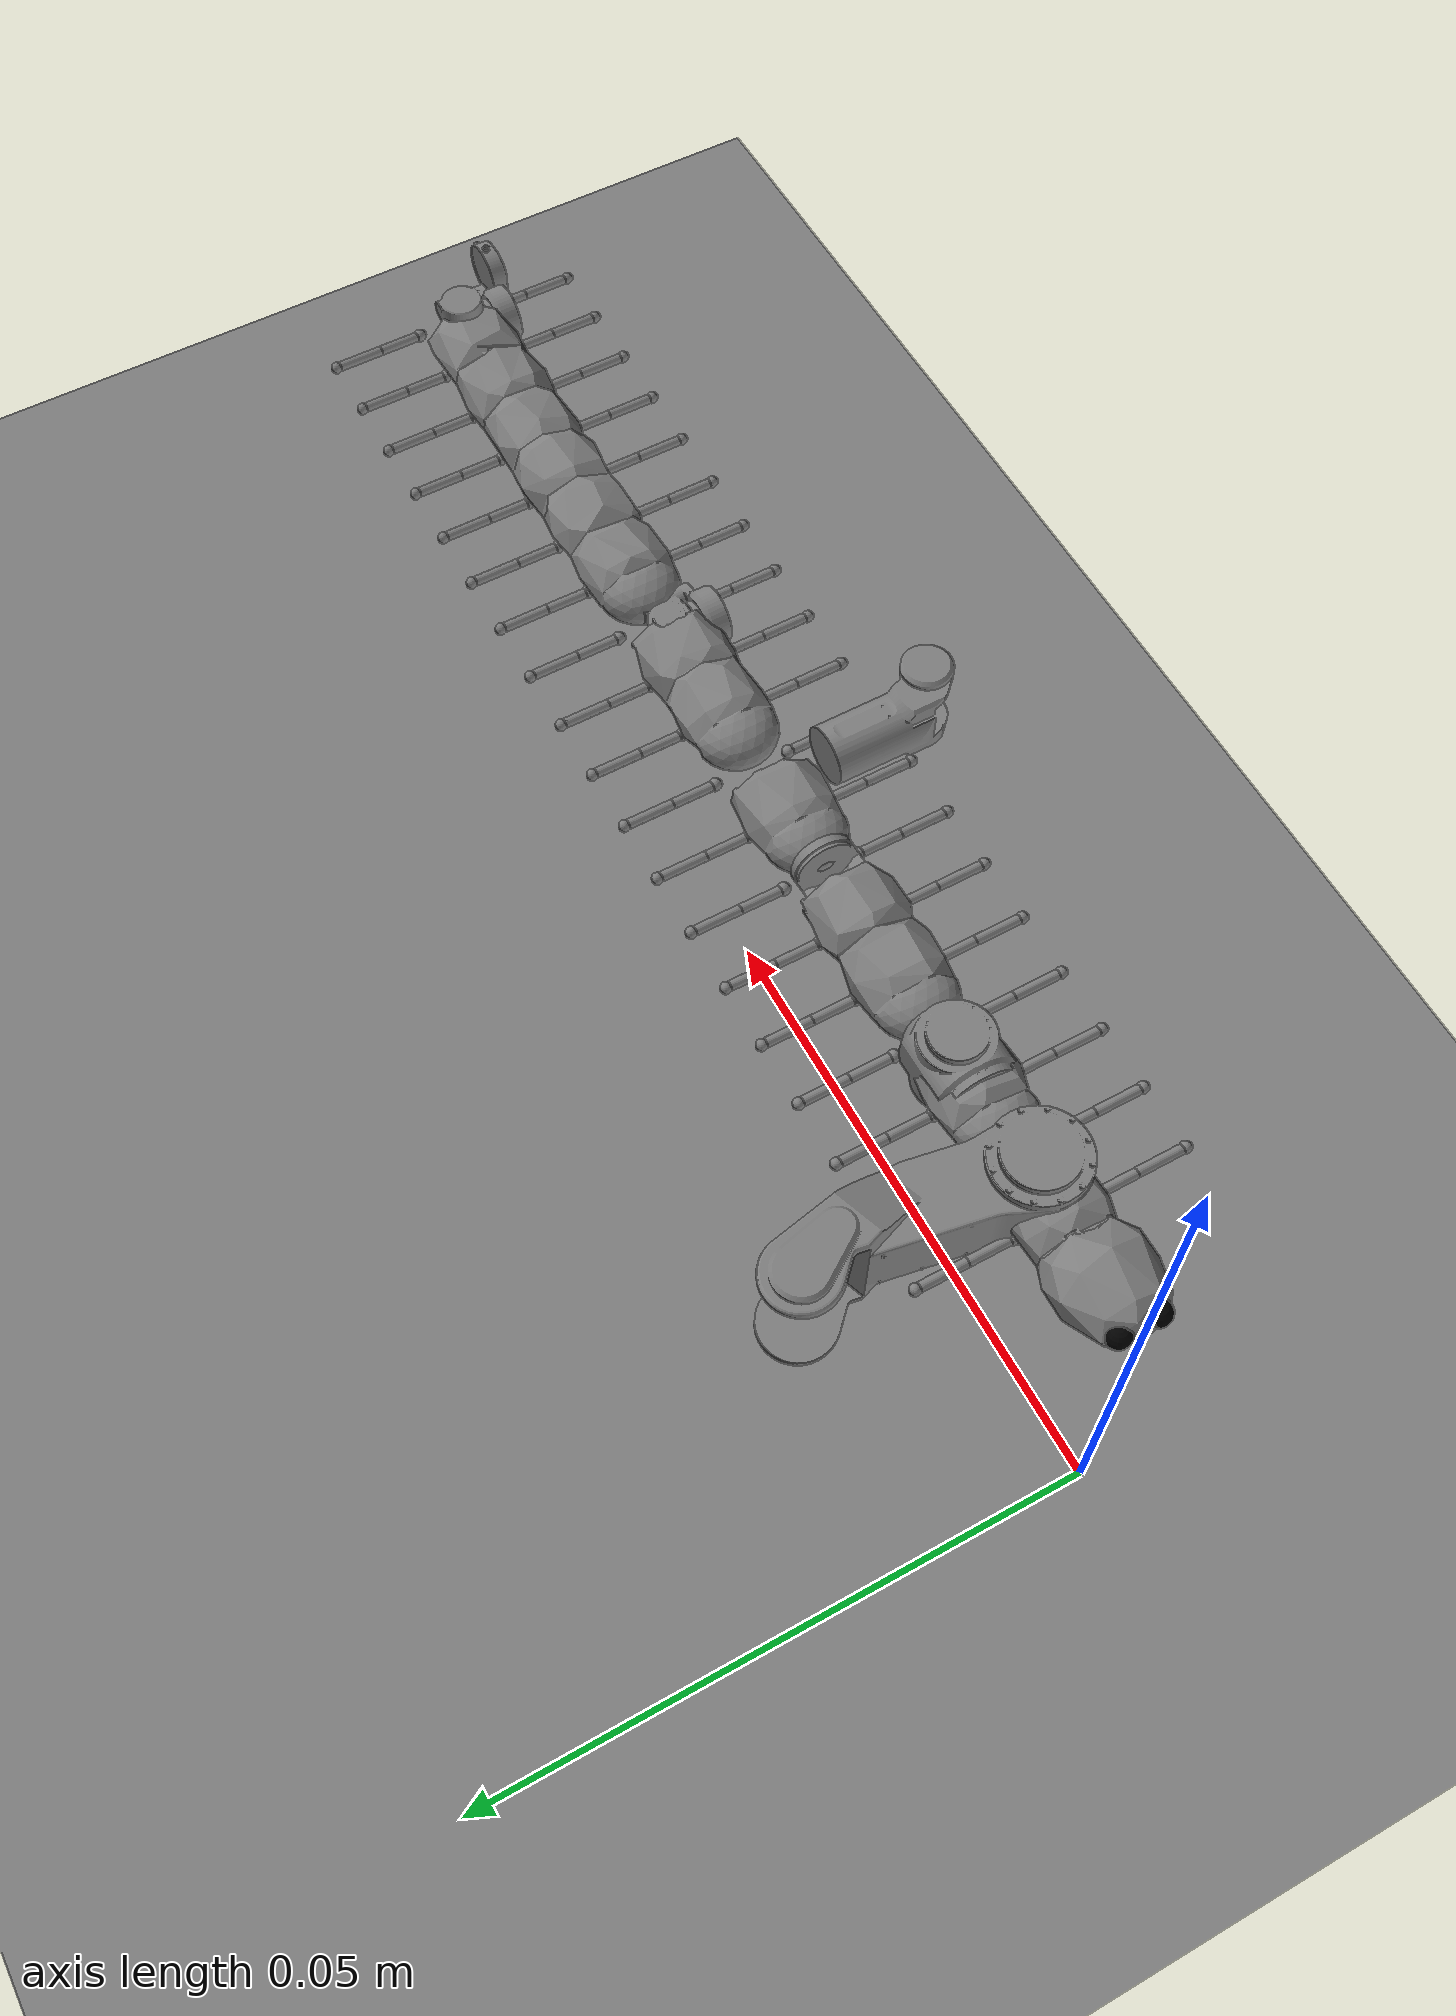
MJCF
<?xml version='1.0' encoding='UTF-8'?>
<mujoco model="centipede">
  <compiler angle="radian" meshdir="meshes" balanceinertia="true" discardvisual="false"/>
  <size nstack="50000000" nconmax="4000" njmax="12000"/>
  <option timestep="0.0005" gravity="0 0 -9.81" integrator="RK4" cone="elliptic"/>
  <visual>
    <global offwidth="1280" offheight="720"/>
  </visual>
  <default>
    <joint damping="4.0754e-06" armature="0.0001" frictionloss="0.0"/>
    <geom condim="3" friction="1.6 0.02 0.001" solref="0.005 1.5" solimp="0.9 0.95 0.001"/>
  </default>
  <asset>
    <texture name="groundplane" type="2d" builtin="checker" rgb1="0.3 0.4 0.3" rgb2="0.25 0.35 0.25" width="512" height="512"/>
    <material name="groundplane" texture="groundplane" texuniform="false" texrepeat="5 5" reflectance="0.1"/>
    <mesh name="link_0" file="link_0.obj" scale="0.05 0.05 0.05"/>
    <mesh name="link_1" file="link_1.obj" scale="0.05 0.05 0.05"/>
    <mesh name="link_10" file="link_10.obj" scale="0.05 0.05 0.05"/>
    <mesh name="link_11" file="link_11.obj" scale="0.05 0.05 0.05"/>
    <mesh name="link_12" file="link_12.obj" scale="0.05 0.05 0.05"/>
    <mesh name="link_13" file="link_13.obj" scale="0.05 0.05 0.05"/>
    <mesh name="link_14" file="link_14.obj" scale="0.05 0.05 0.05"/>
    <mesh name="link_15" file="link_15.obj" scale="0.05 0.05 0.05"/>
    <mesh name="link_16" file="link_16.obj" scale="0.05 0.05 0.05"/>
    <mesh name="link_17" file="link_17.obj" scale="0.05 0.05 0.05"/>
    <mesh name="link_18" file="link_18.obj" scale="0.05 0.05 0.05"/>
    <mesh name="link_19" file="link_19.obj" scale="0.05 0.05 0.05"/>
    <mesh name="link_2" file="link_2.obj" scale="0.05 0.05 0.05"/>
    <mesh name="link_20" file="link_20.obj" scale="0.05 0.05 0.05"/>
    <mesh name="link_3" file="link_3.obj" scale="0.05 0.05 0.05"/>
    <mesh name="link_4" file="link_4.obj" scale="0.05 0.05 0.05"/>
    <mesh name="link_5" file="link_5.obj" scale="0.05 0.05 0.05"/>
    <mesh name="link_6" file="link_6.obj" scale="0.05 0.05 0.05"/>
    <mesh name="link_7" file="link_7.obj" scale="0.05 0.05 0.05"/>
    <mesh name="link_8" file="link_8.obj" scale="0.05 0.05 0.05"/>
    <mesh name="link_9" file="link_9.obj" scale="0.05 0.05 0.05"/>
  <!-- hfield is patched in at runtime by sweep scripts (patch_xml_terrain) -->
  </asset>
  <worldbody>
    <light name="light_main" pos="0.2 -0.1 0.3" dir="-0.2 0.1 -0.3" diffuse="0.8 0.8 0.8" specular="0.3 0.3 0.3" directional="true" castshadow="true"/>
    <light name="light_fill" pos="-0.1 0.1 0.1" dir="0.1 -0.1 -0.1" diffuse="0.3 0.3 0.35" specular="0.0 0.0 0.0" directional="true" castshadow="false"/>
    <body name="link_body_0" pos="0 0 0.0283" euler="0 0 0">
      <freejoint name="root"/>
      <inertial pos="0.0034859071 2.6599856e-06 0.00022589701" mass="0.00012018274" fullinertia="5.928697e-10 4.856396e-10 6.798664e-10 -2.228661e-12 4.544452e-12 -3.742921e-13"/>
      <geom type="mesh" mesh="link_0" pos="0 0 0" group="0" name="link_0_collision"/>
      <geom type="mesh" mesh="link_0" pos="0 0 0" contype="0" conaffinity="0" group="2" name="link_0_visual" rgba="0.1 0.0 0.0 1.0"/>
      <geom type="sphere" size="0.001" pos="0.00075 -0.0015 0.00075" contype="0" conaffinity="0" group="2" name="eye_left_visual" rgba="0.0 0.0 0.0 1.0"/>
      <geom type="sphere" size="0.001" pos="0.00075 0.0015 0.00075" contype="0" conaffinity="0" group="2" name="eye_right_visual" rgba="0.0 0.0 0.0 1.0"/>
      <body name="link_pitch_body_0" pos="0.0075000003 0 0">
        <joint name="joint_pitch_body_0" type="hinge" pos="0 0 0" axis="0 1 0" range="-1.5708 1.5708" damping="0" stiffness="0"/>
        <joint name="joint_roll_body_0" type="hinge" pos="0 0 0" axis="1 0 0" range="-0.5236 0.5236" stiffness="5e-3" damping="2e-3"/>
        <inertial pos="0 0 0" mass="1e-9" diaginertia="1e-15 1e-15 1e-15"/>
        <body name="link_body_1" pos="0 0 0">
          <inertial pos="0.00071585539 8.9238797e-07 1.1906437e-05" mass="0.00010887424" fullinertia="4.455731e-10 4.838302e-10 6.135550e-10 9.113191e-13 -1.100852e-12 -2.252316e-12"/>
          <geom type="mesh" mesh="link_1" pos="0 0 0" group="0" name="link_1_collision"/>
          <geom type="mesh" mesh="link_1" pos="0 0 0" contype="0" conaffinity="0" group="2" name="link_1_visual" rgba="0.02 0.0 0.0 1.0"/>
          <body name="link_leg_0_L_0" pos="0.0025 -0.003 -0.0015">
            <joint name="joint_leg_0_L_0" type="hinge" pos="0 0 0" axis="0 0 -1" range="-3.14159 3.14159" damping="3e-08"/>
            <joint name="joint_roll_leg_0_L" type="hinge" pos="0 0 0" axis="1 0 0" range="-0.3491 0.3491" stiffness="1.000000e-02" damping="5.000000e-03"/>
            <inertial pos="0 0 0" mass="1e-9" diaginertia="1e-15 1e-15 1e-15"/>
            <geom type="sphere" size="0.0004125" pos="0 0 0" group="0" name="link_leg_0_L_0_collision"/>
            <geom type="sphere" size="0.0004125" pos="0 0 0" contype="0" conaffinity="0" group="2" name="link_leg_0_L_0_visual" rgba="0.7 0.5 0.5 0.5"/>
            <body name="link_leg_0_L_1" pos="0 0 0">
              <joint name="joint_leg_0_L_1" type="hinge" pos="0 0 0" axis="1 0 0" range="-3.14159 3.14159" damping="3e-08"/>
              <inertial pos="0 0 0" mass="1e-9" diaginertia="1e-15 1e-15 1e-15"/>
              <geom type="sphere" size="0.0004875" pos="0 0 0" group="0" name="link_leg_0_L_1_collision"/>
              <geom type="sphere" size="0.0004875" pos="0 0 0" contype="0" conaffinity="0" group="2" name="link_leg_0_L_1_visual" rgba="0.9 0.9 0.9 0.3"/>
              <body name="link_leg_0_L_2" pos="0 0 0">
                <joint name="joint_leg_0_L_2" type="hinge" pos="0 0 0" axis="0 1 0" range="-3.14159 3.14159" damping="8.531e-05"/>
                <inertial pos="0 -0.00175 0" mass="1.7671459e-06" fullinertia="1.866088e-12 1.242524e-13 1.866088e-12 0.000000e+00 0.000000e+00 1.066566e-28"/>
                <geom type="capsule" fromto="0 0 -1.07157e-19 0 -0.0035 1.07157e-19" size="0.000375" group="0" name="link_leg_0_L_2_collision"/>
                <geom type="capsule" fromto="0 0 -1.07157e-19 0 -0.0035 1.07157e-19" size="0.000375" contype="0" conaffinity="0" group="2" name="link_leg_0_L_2_visual"/>
                <body name="link_leg_0_L_3" pos="0 -0.0035 0">
                  <joint name="joint_leg_0_L_3" type="hinge" pos="0 0 0" axis="1 0 0" range="-3.14159 3.14159" damping="0.006117"/>
                  <inertial pos="0 -0.00175 0" mass="1.7671459e-06" fullinertia="1.866088e-12 1.242524e-13 1.866088e-12 0.000000e+00 0.000000e+00 1.066566e-28"/>
                  <geom type="capsule" fromto="0 0 -1.07157e-19 0 -0.0035 1.07157e-19" size="0.000375" group="0" name="link_leg_0_L_3_collision"/>
                  <geom type="capsule" fromto="0 0 -1.07157e-19 0 -0.0035 1.07157e-19" size="0.000375" contype="0" conaffinity="0" group="2" name="link_leg_0_L_3_visual"/>
                  <body name="foot_0_0" pos="0 -0.003875 0">
                    <joint name="joint_foot_0_0" type="hinge" pos="0 0 0" axis="0 0 1" range="-3.14159 3.14159" damping="0.006117"/>
                    <inertial pos="0 0 0" mass="3.8170351e-07" fullinertia="3.091798e-14 3.091798e-14 3.091798e-14 0.000000e+00 0.000000e+00 0.000000e+00"/>
                    <geom type="sphere" size="0.00045" pos="0 0 0" group="0" name="foot_0_0_collision"/>
                    <geom type="sphere" size="0.00045" pos="0 0 0" contype="0" conaffinity="0" group="2" name="foot_0_0_visual"/>
                    <site name="site_foot_0_0" pos="0 0 0" size="0.0003" group="4"/>
                  </body>
                  <site name="site_link_leg_0_L_3" pos="0 0 0" size="0.0003" group="4"/>
                </body>
              </body>
            </body>
          </body>
          <body name="link_leg_0_R_0" pos="0.0025 0.003 -0.0015">
            <joint name="joint_leg_0_R_0" type="hinge" pos="0 0 0" axis="0 0 1" range="-3.14159 3.14159" damping="3e-08"/>
            <joint name="joint_roll_leg_0_R" type="hinge" pos="0 0 0" axis="1 0 0" range="-0.3491 0.3491" stiffness="1.000000e-02" damping="5.000000e-03"/>
            <inertial pos="0 0 0" mass="1e-9" diaginertia="1e-15 1e-15 1e-15"/>
            <geom type="sphere" size="0.0004125" pos="0 0 0" group="0" name="link_leg_0_R_0_collision"/>
            <geom type="sphere" size="0.0004125" pos="0 0 0" contype="0" conaffinity="0" group="2" name="link_leg_0_R_0_visual" rgba="0.7 0.5 0.5 0.5"/>
            <body name="link_leg_0_R_1" pos="0 0 0">
              <joint name="joint_leg_0_R_1" type="hinge" pos="0 0 0" axis="-1 0 0" range="-3.14159 3.14159" damping="3e-08"/>
              <inertial pos="0 0 0" mass="1e-9" diaginertia="1e-15 1e-15 1e-15"/>
              <geom type="sphere" size="0.0004875" pos="0 0 0" group="0" name="link_leg_0_R_1_collision"/>
              <geom type="sphere" size="0.0004875" pos="0 0 0" contype="0" conaffinity="0" group="2" name="link_leg_0_R_1_visual" rgba="0.9 0.9 0.9 0.3"/>
              <body name="link_leg_0_R_2" pos="0 0 0">
                <joint name="joint_leg_0_R_2" type="hinge" pos="0 0 0" axis="0 1 0" range="-3.14159 3.14159" damping="8.531e-05"/>
                <inertial pos="0 0.00175 0" mass="1.7671459e-06" fullinertia="1.866088e-12 1.242524e-13 1.866088e-12 0.000000e+00 0.000000e+00 1.066566e-28"/>
                <geom type="capsule" fromto="0 0.0035 -1.07157e-19 0 0 1.07157e-19" size="0.000375" group="0" name="link_leg_0_R_2_collision"/>
                <geom type="capsule" fromto="0 0.0035 -1.07157e-19 0 0 1.07157e-19" size="0.000375" contype="0" conaffinity="0" group="2" name="link_leg_0_R_2_visual"/>
                <body name="link_leg_0_R_3" pos="0 0.0035 0">
                  <joint name="joint_leg_0_R_3" type="hinge" pos="0 0 0" axis="-1 0 0" range="-3.14159 3.14159" damping="0.006117"/>
                  <inertial pos="0 0.00175 0" mass="1.7671459e-06" fullinertia="1.866088e-12 1.242524e-13 1.866088e-12 0.000000e+00 0.000000e+00 1.066566e-28"/>
                  <geom type="capsule" fromto="0 0.0035 -1.07157e-19 0 0 1.07157e-19" size="0.000375" group="0" name="link_leg_0_R_3_collision"/>
                  <geom type="capsule" fromto="0 0.0035 -1.07157e-19 0 0 1.07157e-19" size="0.000375" contype="0" conaffinity="0" group="2" name="link_leg_0_R_3_visual"/>
                  <body name="foot_0_1" pos="0 0.003875 0">
                    <joint name="joint_foot_0_1" type="hinge" pos="0 0 0" axis="0 0 1" range="-3.14159 3.14159" damping="0.006117"/>
                    <inertial pos="0 0 0" mass="3.8170351e-07" fullinertia="3.091798e-14 3.091798e-14 3.091798e-14 0.000000e+00 0.000000e+00 0.000000e+00"/>
                    <geom type="sphere" size="0.00045" pos="0 0 0" group="0" name="foot_0_1_collision"/>
                    <geom type="sphere" size="0.00045" pos="0 0 0" contype="0" conaffinity="0" group="2" name="foot_0_1_visual"/>
                    <site name="site_foot_0_1" pos="0 0 0" size="0.0003" group="4"/>
                  </body>
                  <site name="site_link_leg_0_R_3" pos="0 0 0" size="0.0003" group="4"/>
                </body>
              </body>
            </body>
          </body>
          <body name="link_pitch_body_1" pos="0.0049999997 0 0">
            <joint name="joint_pitch_body_1" type="hinge" pos="0 0 0" axis="0 1 0" range="-1.5708 1.5708" damping="0" stiffness="0"/>
        <joint name="joint_roll_body_1" type="hinge" pos="0 0 0" axis="1 0 0" range="-0.5236 0.5236" stiffness="5e-3" damping="2e-3"/>
            <inertial pos="0 0 0" mass="1e-9" diaginertia="1e-15 1e-15 1e-15"/>
            <body name="link_body_2" pos="0 0 0">
              <joint name="joint_body_1" type="hinge" pos="0 0 0" axis="0 0 1" range="-0.628319 0.628319" damping="4.075e-06"/>
              <inertial pos="0.00072317778 -1.7782734e-05 -6.8883141e-06" mass="0.00011200172" fullinertia="4.616537e-10 5.064631e-10 6.365675e-10 3.207249e-12 3.189197e-13 7.915634e-13"/>
              <geom type="mesh" mesh="link_2" pos="0 0 0" group="0" name="link_2_collision"/>
              <geom type="mesh" mesh="link_2" pos="0 0 0" contype="0" conaffinity="0" group="2" name="link_2_visual" rgba="0.1 0.0 0.0 1.0"/>
              <body name="link_leg_1_L_0" pos="0.0025 -0.003 -0.0015">
                <joint name="joint_leg_1_L_0" type="hinge" pos="0 0 0" axis="0 0 -1" range="-3.14159 3.14159" damping="3e-08"/>
            <joint name="joint_roll_leg_1_L" type="hinge" pos="0 0 0" axis="1 0 0" range="-0.3491 0.3491" stiffness="1.000000e-02" damping="5.000000e-03"/>
                <inertial pos="0 0 0" mass="1e-9" diaginertia="1e-15 1e-15 1e-15"/>
                <geom type="sphere" size="0.0004125" pos="0 0 0" group="0" name="link_leg_1_L_0_collision"/>
                <geom type="sphere" size="0.0004125" pos="0 0 0" contype="0" conaffinity="0" group="2" name="link_leg_1_L_0_visual" rgba="0.7 0.5 0.5 0.5"/>
                <body name="link_leg_1_L_1" pos="0 0 0">
                  <joint name="joint_leg_1_L_1" type="hinge" pos="0 0 0" axis="1 0 0" range="-3.14159 3.14159" damping="3e-08"/>
                  <inertial pos="0 0 0" mass="1e-9" diaginertia="1e-15 1e-15 1e-15"/>
                  <geom type="sphere" size="0.0004875" pos="0 0 0" group="0" name="link_leg_1_L_1_collision"/>
                  <geom type="sphere" size="0.0004875" pos="0 0 0" contype="0" conaffinity="0" group="2" name="link_leg_1_L_1_visual" rgba="0.9 0.9 0.9 0.3"/>
                  <body name="link_leg_1_L_2" pos="0 0 0">
                    <joint name="joint_leg_1_L_2" type="hinge" pos="0 0 0" axis="0 1 0" range="-3.14159 3.14159" damping="8.531e-05"/>
                    <inertial pos="0 -0.00175 0" mass="1.7671459e-06" fullinertia="1.866088e-12 1.242524e-13 1.866088e-12 0.000000e+00 0.000000e+00 1.066566e-28"/>
                    <geom type="capsule" fromto="0 0 -1.07157e-19 0 -0.0035 1.07157e-19" size="0.000375" group="0" name="link_leg_1_L_2_collision"/>
                    <geom type="capsule" fromto="0 0 -1.07157e-19 0 -0.0035 1.07157e-19" size="0.000375" contype="0" conaffinity="0" group="2" name="link_leg_1_L_2_visual"/>
                    <body name="link_leg_1_L_3" pos="0 -0.0035 0">
                      <joint name="joint_leg_1_L_3" type="hinge" pos="0 0 0" axis="1 0 0" range="-3.14159 3.14159" damping="0.006117"/>
                      <inertial pos="0 -0.00175 0" mass="1.7671459e-06" fullinertia="1.866088e-12 1.242524e-13 1.866088e-12 0.000000e+00 0.000000e+00 1.066566e-28"/>
                      <geom type="capsule" fromto="0 0 -1.07157e-19 0 -0.0035 1.07157e-19" size="0.000375" group="0" name="link_leg_1_L_3_collision"/>
                      <geom type="capsule" fromto="0 0 -1.07157e-19 0 -0.0035 1.07157e-19" size="0.000375" contype="0" conaffinity="0" group="2" name="link_leg_1_L_3_visual"/>
                      <body name="foot_1_0" pos="0 -0.003875 0">
                        <joint name="joint_foot_1_0" type="hinge" pos="0 0 0" axis="0 0 1" range="-3.14159 3.14159" damping="0.006117"/>
                        <inertial pos="0 0 0" mass="3.8170351e-07" fullinertia="3.091798e-14 3.091798e-14 3.091798e-14 0.000000e+00 0.000000e+00 0.000000e+00"/>
                        <geom type="sphere" size="0.00045" pos="0 0 0" group="0" name="foot_1_0_collision"/>
                        <geom type="sphere" size="0.00045" pos="0 0 0" contype="0" conaffinity="0" group="2" name="foot_1_0_visual"/>
                        <site name="site_foot_1_0" pos="0 0 0" size="0.0003" group="4"/>
                      </body>
                      <site name="site_link_leg_1_L_3" pos="0 0 0" size="0.0003" group="4"/>
                    </body>
                  </body>
                </body>
              </body>
              <body name="link_leg_1_R_0" pos="0.0025 0.003 -0.0015">
                <joint name="joint_leg_1_R_0" type="hinge" pos="0 0 0" axis="0 0 1" range="-3.14159 3.14159" damping="3e-08"/>
            <joint name="joint_roll_leg_1_R" type="hinge" pos="0 0 0" axis="1 0 0" range="-0.3491 0.3491" stiffness="1.000000e-02" damping="5.000000e-03"/>
                <inertial pos="0 0 0" mass="1e-9" diaginertia="1e-15 1e-15 1e-15"/>
                <geom type="sphere" size="0.0004125" pos="0 0 0" group="0" name="link_leg_1_R_0_collision"/>
                <geom type="sphere" size="0.0004125" pos="0 0 0" contype="0" conaffinity="0" group="2" name="link_leg_1_R_0_visual" rgba="0.7 0.5 0.5 0.5"/>
                <body name="link_leg_1_R_1" pos="0 0 0">
                  <joint name="joint_leg_1_R_1" type="hinge" pos="0 0 0" axis="-1 0 0" range="-3.14159 3.14159" damping="3e-08"/>
                  <inertial pos="0 0 0" mass="1e-9" diaginertia="1e-15 1e-15 1e-15"/>
                  <geom type="sphere" size="0.0004875" pos="0 0 0" group="0" name="link_leg_1_R_1_collision"/>
                  <geom type="sphere" size="0.0004875" pos="0 0 0" contype="0" conaffinity="0" group="2" name="link_leg_1_R_1_visual" rgba="0.9 0.9 0.9 0.3"/>
                  <body name="link_leg_1_R_2" pos="0 0 0">
                    <joint name="joint_leg_1_R_2" type="hinge" pos="0 0 0" axis="0 1 0" range="-3.14159 3.14159" damping="8.531e-05"/>
                    <inertial pos="0 0.00175 0" mass="1.7671459e-06" fullinertia="1.866088e-12 1.242524e-13 1.866088e-12 0.000000e+00 0.000000e+00 1.066566e-28"/>
                    <geom type="capsule" fromto="0 0.0035 -1.07157e-19 0 0 1.07157e-19" size="0.000375" group="0" name="link_leg_1_R_2_collision"/>
                    <geom type="capsule" fromto="0 0.0035 -1.07157e-19 0 0 1.07157e-19" size="0.000375" contype="0" conaffinity="0" group="2" name="link_leg_1_R_2_visual"/>
                    <body name="link_leg_1_R_3" pos="0 0.0035 0">
                      <joint name="joint_leg_1_R_3" type="hinge" pos="0 0 0" axis="-1 0 0" range="-3.14159 3.14159" damping="0.006117"/>
                      <inertial pos="0 0.00175 0" mass="1.7671459e-06" fullinertia="1.866088e-12 1.242524e-13 1.866088e-12 0.000000e+00 0.000000e+00 1.066566e-28"/>
                      <geom type="capsule" fromto="0 0.0035 -1.07157e-19 0 0 1.07157e-19" size="0.000375" group="0" name="link_leg_1_R_3_collision"/>
                      <geom type="capsule" fromto="0 0.0035 -1.07157e-19 0 0 1.07157e-19" size="0.000375" contype="0" conaffinity="0" group="2" name="link_leg_1_R_3_visual"/>
                      <body name="foot_1_1" pos="0 0.003875 0">
                        <joint name="joint_foot_1_1" type="hinge" pos="0 0 0" axis="0 0 1" range="-3.14159 3.14159" damping="0.006117"/>
                        <inertial pos="0 0 0" mass="3.8170351e-07" fullinertia="3.091798e-14 3.091798e-14 3.091798e-14 0.000000e+00 0.000000e+00 0.000000e+00"/>
                        <geom type="sphere" size="0.00045" pos="0 0 0" group="0" name="foot_1_1_collision"/>
                        <geom type="sphere" size="0.00045" pos="0 0 0" contype="0" conaffinity="0" group="2" name="foot_1_1_visual"/>
                        <site name="site_foot_1_1" pos="0 0 0" size="0.0003" group="4"/>
                      </body>
                      <site name="site_link_leg_1_R_3" pos="0 0 0" size="0.0003" group="4"/>
                    </body>
                  </body>
                </body>
              </body>
              <body name="link_pitch_body_2" pos="0.0049999997 0 0">
                <joint name="joint_pitch_body_2" type="hinge" pos="0 0 0" axis="0 1 0" range="-1.5708 1.5708" damping="0" stiffness="0"/>
        <joint name="joint_roll_body_2" type="hinge" pos="0 0 0" axis="1 0 0" range="-0.5236 0.5236" stiffness="5e-3" damping="2e-3"/>
                <inertial pos="0 0 0" mass="1e-9" diaginertia="1e-15 1e-15 1e-15"/>
                <body name="link_body_3" pos="0 0 0">
                  <joint name="joint_body_2" type="hinge" pos="0 0 0" axis="0 0 1" range="-0.628319 0.628319" damping="4.075e-06"/>
                  <inertial pos="0.00071725363 6.6742946e-06 2.866666e-06" mass="0.00010889986" fullinertia="4.488238e-10 4.780834e-10 6.156699e-10 1.903258e-12 -2.285137e-12 -1.365455e-12"/>
                  <geom type="mesh" mesh="link_3" pos="0 0 0" group="0" name="link_3_collision"/>
                  <geom type="mesh" mesh="link_3" pos="0 0 0" contype="0" conaffinity="0" group="2" name="link_3_visual" rgba="0.02 0.0 0.0 1.0"/>
                  <body name="link_leg_2_L_0" pos="0.0025 -0.003 -0.0015">
                    <joint name="joint_leg_2_L_0" type="hinge" pos="0 0 0" axis="0 0 -1" range="-3.14159 3.14159" damping="3e-08"/>
            <joint name="joint_roll_leg_2_L" type="hinge" pos="0 0 0" axis="1 0 0" range="-0.3491 0.3491" stiffness="1.000000e-02" damping="5.000000e-03"/>
                    <inertial pos="0 0 0" mass="1e-9" diaginertia="1e-15 1e-15 1e-15"/>
                    <geom type="sphere" size="0.0004125" pos="0 0 0" group="0" name="link_leg_2_L_0_collision"/>
                    <geom type="sphere" size="0.0004125" pos="0 0 0" contype="0" conaffinity="0" group="2" name="link_leg_2_L_0_visual" rgba="0.7 0.5 0.5 0.5"/>
                    <body name="link_leg_2_L_1" pos="0 0 0">
                      <joint name="joint_leg_2_L_1" type="hinge" pos="0 0 0" axis="1 0 0" range="-3.14159 3.14159" damping="3e-08"/>
                      <inertial pos="0 0 0" mass="1e-9" diaginertia="1e-15 1e-15 1e-15"/>
                      <geom type="sphere" size="0.0004875" pos="0 0 0" group="0" name="link_leg_2_L_1_collision"/>
                      <geom type="sphere" size="0.0004875" pos="0 0 0" contype="0" conaffinity="0" group="2" name="link_leg_2_L_1_visual" rgba="0.9 0.9 0.9 0.3"/>
                      <body name="link_leg_2_L_2" pos="0 0 0">
                        <joint name="joint_leg_2_L_2" type="hinge" pos="0 0 0" axis="0 1 0" range="-3.14159 3.14159" damping="8.531e-05"/>
                        <inertial pos="0 -0.00175 0" mass="1.7671459e-06" fullinertia="1.866088e-12 1.242524e-13 1.866088e-12 0.000000e+00 0.000000e+00 1.066566e-28"/>
                        <geom type="capsule" fromto="0 0 -1.07157e-19 0 -0.0035 1.07157e-19" size="0.000375" group="0" name="link_leg_2_L_2_collision"/>
                        <geom type="capsule" fromto="0 0 -1.07157e-19 0 -0.0035 1.07157e-19" size="0.000375" contype="0" conaffinity="0" group="2" name="link_leg_2_L_2_visual"/>
                        <body name="link_leg_2_L_3" pos="0 -0.0035 0">
                          <joint name="joint_leg_2_L_3" type="hinge" pos="0 0 0" axis="1 0 0" range="-3.14159 3.14159" damping="0.006117"/>
                          <inertial pos="0 -0.00175 0" mass="1.7671459e-06" fullinertia="1.866088e-12 1.242524e-13 1.866088e-12 0.000000e+00 0.000000e+00 1.066566e-28"/>
                          <geom type="capsule" fromto="0 0 -1.07157e-19 0 -0.0035 1.07157e-19" size="0.000375" group="0" name="link_leg_2_L_3_collision"/>
                          <geom type="capsule" fromto="0 0 -1.07157e-19 0 -0.0035 1.07157e-19" size="0.000375" contype="0" conaffinity="0" group="2" name="link_leg_2_L_3_visual"/>
                          <body name="foot_2_0" pos="0 -0.003875 0">
                            <joint name="joint_foot_2_0" type="hinge" pos="0 0 0" axis="0 0 1" range="-3.14159 3.14159" damping="0.006117"/>
                            <inertial pos="0 0 0" mass="3.8170351e-07" fullinertia="3.091798e-14 3.091798e-14 3.091798e-14 0.000000e+00 0.000000e+00 0.000000e+00"/>
                            <geom type="sphere" size="0.00045" pos="0 0 0" group="0" name="foot_2_0_collision"/>
                            <geom type="sphere" size="0.00045" pos="0 0 0" contype="0" conaffinity="0" group="2" name="foot_2_0_visual"/>
                            <site name="site_foot_2_0" pos="0 0 0" size="0.0003" group="4"/>
                          </body>
                          <site name="site_link_leg_2_L_3" pos="0 0 0" size="0.0003" group="4"/>
                        </body>
                      </body>
                    </body>
                  </body>
                  <body name="link_leg_2_R_0" pos="0.0025 0.003 -0.0015">
                    <joint name="joint_leg_2_R_0" type="hinge" pos="0 0 0" axis="0 0 1" range="-3.14159 3.14159" damping="3e-08"/>
            <joint name="joint_roll_leg_2_R" type="hinge" pos="0 0 0" axis="1 0 0" range="-0.3491 0.3491" stiffness="1.000000e-02" damping="5.000000e-03"/>
                    <inertial pos="0 0 0" mass="1e-9" diaginertia="1e-15 1e-15 1e-15"/>
                    <geom type="sphere" size="0.0004125" pos="0 0 0" group="0" name="link_leg_2_R_0_collision"/>
                    <geom type="sphere" size="0.0004125" pos="0 0 0" contype="0" conaffinity="0" group="2" name="link_leg_2_R_0_visual" rgba="0.7 0.5 0.5 0.5"/>
                    <body name="link_leg_2_R_1" pos="0 0 0">
                      <joint name="joint_leg_2_R_1" type="hinge" pos="0 0 0" axis="-1 0 0" range="-3.14159 3.14159" damping="3e-08"/>
                      <inertial pos="0 0 0" mass="1e-9" diaginertia="1e-15 1e-15 1e-15"/>
                      <geom type="sphere" size="0.0004875" pos="0 0 0" group="0" name="link_leg_2_R_1_collision"/>
                      <geom type="sphere" size="0.0004875" pos="0 0 0" contype="0" conaffinity="0" group="2" name="link_leg_2_R_1_visual" rgba="0.9 0.9 0.9 0.3"/>
                      <body name="link_leg_2_R_2" pos="0 0 0">
                        <joint name="joint_leg_2_R_2" type="hinge" pos="0 0 0" axis="0 1 0" range="-3.14159 3.14159" damping="8.531e-05"/>
                        <inertial pos="0 0.00175 0" mass="1.7671459e-06" fullinertia="1.866088e-12 1.242524e-13 1.866088e-12 0.000000e+00 0.000000e+00 1.066566e-28"/>
                        <geom type="capsule" fromto="0 0.0035 -1.07157e-19 0 0 1.07157e-19" size="0.000375" group="0" name="link_leg_2_R_2_collision"/>
                        <geom type="capsule" fromto="0 0.0035 -1.07157e-19 0 0 1.07157e-19" size="0.000375" contype="0" conaffinity="0" group="2" name="link_leg_2_R_2_visual"/>
                        <body name="link_leg_2_R_3" pos="0 0.0035 0">
                          <joint name="joint_leg_2_R_3" type="hinge" pos="0 0 0" axis="-1 0 0" range="-3.14159 3.14159" damping="0.006117"/>
                          <inertial pos="0 0.00175 0" mass="1.7671459e-06" fullinertia="1.866088e-12 1.242524e-13 1.866088e-12 0.000000e+00 0.000000e+00 1.066566e-28"/>
                          <geom type="capsule" fromto="0 0.0035 -1.07157e-19 0 0 1.07157e-19" size="0.000375" group="0" name="link_leg_2_R_3_collision"/>
                          <geom type="capsule" fromto="0 0.0035 -1.07157e-19 0 0 1.07157e-19" size="0.000375" contype="0" conaffinity="0" group="2" name="link_leg_2_R_3_visual"/>
                          <body name="foot_2_1" pos="0 0.003875 0">
                            <joint name="joint_foot_2_1" type="hinge" pos="0 0 0" axis="0 0 1" range="-3.14159 3.14159" damping="0.006117"/>
                            <inertial pos="0 0 0" mass="3.8170351e-07" fullinertia="3.091798e-14 3.091798e-14 3.091798e-14 0.000000e+00 0.000000e+00 0.000000e+00"/>
                            <geom type="sphere" size="0.00045" pos="0 0 0" group="0" name="foot_2_1_collision"/>
                            <geom type="sphere" size="0.00045" pos="0 0 0" contype="0" conaffinity="0" group="2" name="foot_2_1_visual"/>
                            <site name="site_foot_2_1" pos="0 0 0" size="0.0003" group="4"/>
                          </body>
                          <site name="site_link_leg_2_R_3" pos="0 0 0" size="0.0003" group="4"/>
                        </body>
                      </body>
                    </body>
                  </body>
                  <body name="link_pitch_body_3" pos="0.0049999997 0 0">
                    <joint name="joint_pitch_body_3" type="hinge" pos="0 0 0" axis="0 1 0" range="-1.5708 1.5708" damping="0" stiffness="0"/>
        <joint name="joint_roll_body_3" type="hinge" pos="0 0 0" axis="1 0 0" range="-0.5236 0.5236" stiffness="5e-3" damping="2e-3"/>
                    <inertial pos="0 0 0" mass="1e-9" diaginertia="1e-15 1e-15 1e-15"/>
                    <body name="link_body_4" pos="0 0 0">
                      <joint name="joint_body_3" type="hinge" pos="0 0 0" axis="0 0 1" range="-0.628319 0.628319" damping="4.075e-06"/>
                      <inertial pos="0.00073197515 -6.6418422e-06 -5.0612273e-06" mass="0.00011165788" fullinertia="4.609690e-10 5.071105e-10 6.389442e-10 1.435527e-12 8.153365e-13 2.272065e-13"/>
                      <geom type="mesh" mesh="link_4" pos="0 0 0" group="0" name="link_4_collision"/>
                      <geom type="mesh" mesh="link_4" pos="0 0 0" contype="0" conaffinity="0" group="2" name="link_4_visual" rgba="0.1 0.0 0.0 1.0"/>
                      <body name="link_leg_3_L_0" pos="0.0025 -0.003 -0.0015">
                        <joint name="joint_leg_3_L_0" type="hinge" pos="0 0 0" axis="0 0 -1" range="-3.14159 3.14159" damping="3e-08"/>
            <joint name="joint_roll_leg_3_L" type="hinge" pos="0 0 0" axis="1 0 0" range="-0.3491 0.3491" stiffness="1.000000e-02" damping="5.000000e-03"/>
                        <inertial pos="0 0 0" mass="1e-9" diaginertia="1e-15 1e-15 1e-15"/>
                        <geom type="sphere" size="0.0004125" pos="0 0 0" group="0" name="link_leg_3_L_0_collision"/>
                        <geom type="sphere" size="0.0004125" pos="0 0 0" contype="0" conaffinity="0" group="2" name="link_leg_3_L_0_visual" rgba="0.7 0.5 0.5 0.5"/>
                        <body name="link_leg_3_L_1" pos="0 0 0">
                          <joint name="joint_leg_3_L_1" type="hinge" pos="0 0 0" axis="1 0 0" range="-3.14159 3.14159" damping="3e-08"/>
                          <inertial pos="0 0 0" mass="1e-9" diaginertia="1e-15 1e-15 1e-15"/>
                          <geom type="sphere" size="0.0004875" pos="0 0 0" group="0" name="link_leg_3_L_1_collision"/>
                          <geom type="sphere" size="0.0004875" pos="0 0 0" contype="0" conaffinity="0" group="2" name="link_leg_3_L_1_visual" rgba="0.9 0.9 0.9 0.3"/>
                          <body name="link_leg_3_L_2" pos="0 0 0">
                            <joint name="joint_leg_3_L_2" type="hinge" pos="0 0 0" axis="0 1 0" range="-3.14159 3.14159" damping="8.531e-05"/>
                            <inertial pos="0 -0.00175 0" mass="1.7671459e-06" fullinertia="1.866088e-12 1.242524e-13 1.866088e-12 0.000000e+00 0.000000e+00 1.066566e-28"/>
                            <geom type="capsule" fromto="0 0 -1.07157e-19 0 -0.0035 1.07157e-19" size="0.000375" group="0" name="link_leg_3_L_2_collision"/>
                            <geom type="capsule" fromto="0 0 -1.07157e-19 0 -0.0035 1.07157e-19" size="0.000375" contype="0" conaffinity="0" group="2" name="link_leg_3_L_2_visual"/>
                            <body name="link_leg_3_L_3" pos="0 -0.0035 0">
                              <joint name="joint_leg_3_L_3" type="hinge" pos="0 0 0" axis="1 0 0" range="-3.14159 3.14159" damping="0.006117"/>
                              <inertial pos="0 -0.00175 0" mass="1.7671459e-06" fullinertia="1.866088e-12 1.242524e-13 1.866088e-12 0.000000e+00 0.000000e+00 1.066566e-28"/>
                              <geom type="capsule" fromto="0 0 -1.07157e-19 0 -0.0035 1.07157e-19" size="0.000375" group="0" name="link_leg_3_L_3_collision"/>
                              <geom type="capsule" fromto="0 0 -1.07157e-19 0 -0.0035 1.07157e-19" size="0.000375" contype="0" conaffinity="0" group="2" name="link_leg_3_L_3_visual"/>
                              <body name="foot_3_0" pos="0 -0.003875 0">
                                <joint name="joint_foot_3_0" type="hinge" pos="0 0 0" axis="0 0 1" range="-3.14159 3.14159" damping="0.006117"/>
                                <inertial pos="0 0 0" mass="3.8170351e-07" fullinertia="3.091798e-14 3.091798e-14 3.091798e-14 0.000000e+00 0.000000e+00 0.000000e+00"/>
                                <geom type="sphere" size="0.00045" pos="0 0 0" group="0" name="foot_3_0_collision"/>
                                <geom type="sphere" size="0.00045" pos="0 0 0" contype="0" conaffinity="0" group="2" name="foot_3_0_visual"/>
                                <site name="site_foot_3_0" pos="0 0 0" size="0.0003" group="4"/>
                              </body>
                              <site name="site_link_leg_3_L_3" pos="0 0 0" size="0.0003" group="4"/>
                            </body>
                          </body>
                        </body>
                      </body>
                      <body name="link_leg_3_R_0" pos="0.0025 0.003 -0.0015">
                        <joint name="joint_leg_3_R_0" type="hinge" pos="0 0 0" axis="0 0 1" range="-3.14159 3.14159" damping="3e-08"/>
            <joint name="joint_roll_leg_3_R" type="hinge" pos="0 0 0" axis="1 0 0" range="-0.3491 0.3491" stiffness="1.000000e-02" damping="5.000000e-03"/>
                        <inertial pos="0 0 0" mass="1e-9" diaginertia="1e-15 1e-15 1e-15"/>
                        <geom type="sphere" size="0.0004125" pos="0 0 0" group="0" name="link_leg_3_R_0_collision"/>
                        <geom type="sphere" size="0.0004125" pos="0 0 0" contype="0" conaffinity="0" group="2" name="link_leg_3_R_0_visual" rgba="0.7 0.5 0.5 0.5"/>
                        <body name="link_leg_3_R_1" pos="0 0 0">
                          <joint name="joint_leg_3_R_1" type="hinge" pos="0 0 0" axis="-1 0 0" range="-3.14159 3.14159" damping="3e-08"/>
                          <inertial pos="0 0 0" mass="1e-9" diaginertia="1e-15 1e-15 1e-15"/>
                          <geom type="sphere" size="0.0004875" pos="0 0 0" group="0" name="link_leg_3_R_1_collision"/>
                          <geom type="sphere" size="0.0004875" pos="0 0 0" contype="0" conaffinity="0" group="2" name="link_leg_3_R_1_visual" rgba="0.9 0.9 0.9 0.3"/>
                          <body name="link_leg_3_R_2" pos="0 0 0">
                            <joint name="joint_leg_3_R_2" type="hinge" pos="0 0 0" axis="0 1 0" range="-3.14159 3.14159" damping="8.531e-05"/>
                            <inertial pos="0 0.00175 0" mass="1.7671459e-06" fullinertia="1.866088e-12 1.242524e-13 1.866088e-12 0.000000e+00 0.000000e+00 1.066566e-28"/>
                            <geom type="capsule" fromto="0 0.0035 -1.07157e-19 0 0 1.07157e-19" size="0.000375" group="0" name="link_leg_3_R_2_collision"/>
                            <geom type="capsule" fromto="0 0.0035 -1.07157e-19 0 0 1.07157e-19" size="0.000375" contype="0" conaffinity="0" group="2" name="link_leg_3_R_2_visual"/>
                            <body name="link_leg_3_R_3" pos="0 0.0035 0">
                              <joint name="joint_leg_3_R_3" type="hinge" pos="0 0 0" axis="-1 0 0" range="-3.14159 3.14159" damping="0.006117"/>
                              <inertial pos="0 0.00175 0" mass="1.7671459e-06" fullinertia="1.866088e-12 1.242524e-13 1.866088e-12 0.000000e+00 0.000000e+00 1.066566e-28"/>
                              <geom type="capsule" fromto="0 0.0035 -1.07157e-19 0 0 1.07157e-19" size="0.000375" group="0" name="link_leg_3_R_3_collision"/>
                              <geom type="capsule" fromto="0 0.0035 -1.07157e-19 0 0 1.07157e-19" size="0.000375" contype="0" conaffinity="0" group="2" name="link_leg_3_R_3_visual"/>
                              <body name="foot_3_1" pos="0 0.003875 0">
                                <joint name="joint_foot_3_1" type="hinge" pos="0 0 0" axis="0 0 1" range="-3.14159 3.14159" damping="0.006117"/>
                                <inertial pos="0 0 0" mass="3.8170351e-07" fullinertia="3.091798e-14 3.091798e-14 3.091798e-14 0.000000e+00 0.000000e+00 0.000000e+00"/>
                                <geom type="sphere" size="0.00045" pos="0 0 0" group="0" name="foot_3_1_collision"/>
                                <geom type="sphere" size="0.00045" pos="0 0 0" contype="0" conaffinity="0" group="2" name="foot_3_1_visual"/>
                                <site name="site_foot_3_1" pos="0 0 0" size="0.0003" group="4"/>
                              </body>
                              <site name="site_link_leg_3_R_3" pos="0 0 0" size="0.0003" group="4"/>
                            </body>
                          </body>
                        </body>
                      </body>
                      <body name="link_pitch_body_4" pos="0.0050000012 0 0">
                        <joint name="joint_pitch_body_4" type="hinge" pos="0 0 0" axis="0 1 0" range="-1.5708 1.5708" damping="0" stiffness="0"/>
        <joint name="joint_roll_body_4" type="hinge" pos="0 0 0" axis="1 0 0" range="-0.5236 0.5236" stiffness="5e-3" damping="2e-3"/>
                        <inertial pos="0 0 0" mass="1e-9" diaginertia="1e-15 1e-15 1e-15"/>
                        <body name="link_body_5" pos="0 0 0">
                          <joint name="joint_body_4" type="hinge" pos="0 0 0" axis="0 0 1" range="-0.628319 0.628319" damping="4.075e-06"/>
                          <inertial pos="0.00070549676 1.4714941e-05 -1.9913772e-05" mass="0.00010859053" fullinertia="4.453842e-10 4.763314e-10 6.133462e-10 -3.545166e-13 3.482111e-12 1.254966e-12"/>
                          <geom type="mesh" mesh="link_5" pos="0 0 0" group="0" name="link_5_collision"/>
                          <geom type="mesh" mesh="link_5" pos="0 0 0" contype="0" conaffinity="0" group="2" name="link_5_visual" rgba="0.02 0.0 0.0 1.0"/>
                          <body name="link_leg_4_L_0" pos="0.0025 -0.003 -0.0015">
                            <joint name="joint_leg_4_L_0" type="hinge" pos="0 0 0" axis="0 0 -1" range="-3.14159 3.14159" damping="3e-08"/>
            <joint name="joint_roll_leg_4_L" type="hinge" pos="0 0 0" axis="1 0 0" range="-0.3491 0.3491" stiffness="1.000000e-02" damping="5.000000e-03"/>
                            <inertial pos="0 0 0" mass="1e-9" diaginertia="1e-15 1e-15 1e-15"/>
                            <geom type="sphere" size="0.0004125" pos="0 0 0" group="0" name="link_leg_4_L_0_collision"/>
                            <geom type="sphere" size="0.0004125" pos="0 0 0" contype="0" conaffinity="0" group="2" name="link_leg_4_L_0_visual" rgba="0.7 0.5 0.5 0.5"/>
                            <body name="link_leg_4_L_1" pos="0 0 0">
                              <joint name="joint_leg_4_L_1" type="hinge" pos="0 0 0" axis="1 0 0" range="-3.14159 3.14159" damping="3e-08"/>
                              <inertial pos="0 0 0" mass="1e-9" diaginertia="1e-15 1e-15 1e-15"/>
                              <geom type="sphere" size="0.0004875" pos="0 0 0" group="0" name="link_leg_4_L_1_collision"/>
                              <geom type="sphere" size="0.0004875" pos="0 0 0" contype="0" conaffinity="0" group="2" name="link_leg_4_L_1_visual" rgba="0.9 0.9 0.9 0.3"/>
                              <body name="link_leg_4_L_2" pos="0 0 0">
                                <joint name="joint_leg_4_L_2" type="hinge" pos="0 0 0" axis="0 1 0" range="-3.14159 3.14159" damping="8.531e-05"/>
                                <inertial pos="0 -0.00175 0" mass="1.7671459e-06" fullinertia="1.866088e-12 1.242524e-13 1.866088e-12 0.000000e+00 0.000000e+00 1.066566e-28"/>
                                <geom type="capsule" fromto="0 0 -1.07157e-19 0 -0.0035 1.07157e-19" size="0.000375" group="0" name="link_leg_4_L_2_collision"/>
                                <geom type="capsule" fromto="0 0 -1.07157e-19 0 -0.0035 1.07157e-19" size="0.000375" contype="0" conaffinity="0" group="2" name="link_leg_4_L_2_visual"/>
                                <body name="link_leg_4_L_3" pos="0 -0.0035 0">
                                  <joint name="joint_leg_4_L_3" type="hinge" pos="0 0 0" axis="1 0 0" range="-3.14159 3.14159" damping="0.006117"/>
                                  <inertial pos="0 -0.00175 0" mass="1.7671459e-06" fullinertia="1.866088e-12 1.242524e-13 1.866088e-12 0.000000e+00 0.000000e+00 1.066566e-28"/>
                                  <geom type="capsule" fromto="0 0 -1.07157e-19 0 -0.0035 1.07157e-19" size="0.000375" group="0" name="link_leg_4_L_3_collision"/>
                                  <geom type="capsule" fromto="0 0 -1.07157e-19 0 -0.0035 1.07157e-19" size="0.000375" contype="0" conaffinity="0" group="2" name="link_leg_4_L_3_visual"/>
                                  <body name="foot_4_0" pos="0 -0.003875 0">
                                    <joint name="joint_foot_4_0" type="hinge" pos="0 0 0" axis="0 0 1" range="-3.14159 3.14159" damping="0.006117"/>
                                    <inertial pos="0 0 0" mass="3.8170351e-07" fullinertia="3.091798e-14 3.091798e-14 3.091798e-14 0.000000e+00 0.000000e+00 0.000000e+00"/>
                                    <geom type="sphere" size="0.00045" pos="0 0 0" group="0" name="foot_4_0_collision"/>
                                    <geom type="sphere" size="0.00045" pos="0 0 0" contype="0" conaffinity="0" group="2" name="foot_4_0_visual"/>
                                    <site name="site_foot_4_0" pos="0 0 0" size="0.0003" group="4"/>
                                  </body>
                                  <site name="site_link_leg_4_L_3" pos="0 0 0" size="0.0003" group="4"/>
                                </body>
                              </body>
                            </body>
                          </body>
                          <body name="link_leg_4_R_0" pos="0.0025 0.003 -0.0015">
                            <joint name="joint_leg_4_R_0" type="hinge" pos="0 0 0" axis="0 0 1" range="-3.14159 3.14159" damping="3e-08"/>
            <joint name="joint_roll_leg_4_R" type="hinge" pos="0 0 0" axis="1 0 0" range="-0.3491 0.3491" stiffness="1.000000e-02" damping="5.000000e-03"/>
                            <inertial pos="0 0 0" mass="1e-9" diaginertia="1e-15 1e-15 1e-15"/>
                            <geom type="sphere" size="0.0004125" pos="0 0 0" group="0" name="link_leg_4_R_0_collision"/>
                            <geom type="sphere" size="0.0004125" pos="0 0 0" contype="0" conaffinity="0" group="2" name="link_leg_4_R_0_visual" rgba="0.7 0.5 0.5 0.5"/>
                            <body name="link_leg_4_R_1" pos="0 0 0">
                              <joint name="joint_leg_4_R_1" type="hinge" pos="0 0 0" axis="-1 0 0" range="-3.14159 3.14159" damping="3e-08"/>
                              <inertial pos="0 0 0" mass="1e-9" diaginertia="1e-15 1e-15 1e-15"/>
                              <geom type="sphere" size="0.0004875" pos="0 0 0" group="0" name="link_leg_4_R_1_collision"/>
                              <geom type="sphere" size="0.0004875" pos="0 0 0" contype="0" conaffinity="0" group="2" name="link_leg_4_R_1_visual" rgba="0.9 0.9 0.9 0.3"/>
                              <body name="link_leg_4_R_2" pos="0 0 0">
                                <joint name="joint_leg_4_R_2" type="hinge" pos="0 0 0" axis="0 1 0" range="-3.14159 3.14159" damping="8.531e-05"/>
                                <inertial pos="0 0.00175 0" mass="1.7671459e-06" fullinertia="1.866088e-12 1.242524e-13 1.866088e-12 0.000000e+00 0.000000e+00 1.066566e-28"/>
                                <geom type="capsule" fromto="0 0.0035 -1.07157e-19 0 0 1.07157e-19" size="0.000375" group="0" name="link_leg_4_R_2_collision"/>
                                <geom type="capsule" fromto="0 0.0035 -1.07157e-19 0 0 1.07157e-19" size="0.000375" contype="0" conaffinity="0" group="2" name="link_leg_4_R_2_visual"/>
                                <body name="link_leg_4_R_3" pos="0 0.0035 0">
                                  <joint name="joint_leg_4_R_3" type="hinge" pos="0 0 0" axis="-1 0 0" range="-3.14159 3.14159" damping="0.006117"/>
                                  <inertial pos="0 0.00175 0" mass="1.7671459e-06" fullinertia="1.866088e-12 1.242524e-13 1.866088e-12 0.000000e+00 0.000000e+00 1.066566e-28"/>
                                  <geom type="capsule" fromto="0 0.0035 -1.07157e-19 0 0 1.07157e-19" size="0.000375" group="0" name="link_leg_4_R_3_collision"/>
                                  <geom type="capsule" fromto="0 0.0035 -1.07157e-19 0 0 1.07157e-19" size="0.000375" contype="0" conaffinity="0" group="2" name="link_leg_4_R_3_visual"/>
                                  <body name="foot_4_1" pos="0 0.003875 0">
                                    <joint name="joint_foot_4_1" type="hinge" pos="0 0 0" axis="0 0 1" range="-3.14159 3.14159" damping="0.006117"/>
                                    <inertial pos="0 0 0" mass="3.8170351e-07" fullinertia="3.091798e-14 3.091798e-14 3.091798e-14 0.000000e+00 0.000000e+00 0.000000e+00"/>
                                    <geom type="sphere" size="0.00045" pos="0 0 0" group="0" name="foot_4_1_collision"/>
                                    <geom type="sphere" size="0.00045" pos="0 0 0" contype="0" conaffinity="0" group="2" name="foot_4_1_visual"/>
                                    <site name="site_foot_4_1" pos="0 0 0" size="0.0003" group="4"/>
                                  </body>
                                  <site name="site_link_leg_4_R_3" pos="0 0 0" size="0.0003" group="4"/>
                                </body>
                              </body>
                            </body>
                          </body>
                          <body name="link_pitch_body_5" pos="0.0049999982 0 0">
                            <joint name="joint_pitch_body_5" type="hinge" pos="0 0 0" axis="0 1 0" range="-1.5708 1.5708" damping="0" stiffness="0"/>
        <joint name="joint_roll_body_5" type="hinge" pos="0 0 0" axis="1 0 0" range="-0.5236 0.5236" stiffness="5e-3" damping="2e-3"/>
                            <inertial pos="0 0 0" mass="1e-9" diaginertia="1e-15 1e-15 1e-15"/>
                            <body name="link_body_6" pos="0 0 0">
                              <joint name="joint_body_5" type="hinge" pos="0 0 0" axis="0 0 1" range="-0.628319 0.628319" damping="4.075e-06"/>
                              <inertial pos="0.00070476078 -4.636674e-06 -7.8054134e-06" mass="0.00010969565" fullinertia="4.464987e-10 4.932287e-10 6.193790e-10 7.247791e-13 1.495418e-12 1.072827e-12"/>
                              <geom type="mesh" mesh="link_6" pos="0 0 0" group="0" name="link_6_collision"/>
                              <geom type="mesh" mesh="link_6" pos="0 0 0" contype="0" conaffinity="0" group="2" name="link_6_visual" rgba="0.1 0.0 0.0 1.0"/>
                              <body name="link_leg_5_L_0" pos="0.0025 -0.003 -0.0015">
                                <joint name="joint_leg_5_L_0" type="hinge" pos="0 0 0" axis="0 0 -1" range="-3.14159 3.14159" damping="3e-08"/>
            <joint name="joint_roll_leg_5_L" type="hinge" pos="0 0 0" axis="1 0 0" range="-0.3491 0.3491" stiffness="1.000000e-02" damping="5.000000e-03"/>
                                <inertial pos="0 0 0" mass="1e-9" diaginertia="1e-15 1e-15 1e-15"/>
                                <geom type="sphere" size="0.0004125" pos="0 0 0" group="0" name="link_leg_5_L_0_collision"/>
                                <geom type="sphere" size="0.0004125" pos="0 0 0" contype="0" conaffinity="0" group="2" name="link_leg_5_L_0_visual" rgba="0.7 0.5 0.5 0.5"/>
                                <body name="link_leg_5_L_1" pos="0 0 0">
                                  <joint name="joint_leg_5_L_1" type="hinge" pos="0 0 0" axis="1 0 0" range="-3.14159 3.14159" damping="3e-08"/>
                                  <inertial pos="0 0 0" mass="1e-9" diaginertia="1e-15 1e-15 1e-15"/>
                                  <geom type="sphere" size="0.0004875" pos="0 0 0" group="0" name="link_leg_5_L_1_collision"/>
                                  <geom type="sphere" size="0.0004875" pos="0 0 0" contype="0" conaffinity="0" group="2" name="link_leg_5_L_1_visual" rgba="0.9 0.9 0.9 0.3"/>
                                  <body name="link_leg_5_L_2" pos="0 0 0">
                                    <joint name="joint_leg_5_L_2" type="hinge" pos="0 0 0" axis="0 1 0" range="-3.14159 3.14159" damping="8.531e-05"/>
                                    <inertial pos="0 -0.00175 0" mass="1.7671459e-06" fullinertia="1.866088e-12 1.242524e-13 1.866088e-12 0.000000e+00 0.000000e+00 1.066566e-28"/>
                                    <geom type="capsule" fromto="0 0 -1.07157e-19 0 -0.0035 1.07157e-19" size="0.000375" group="0" name="link_leg_5_L_2_collision"/>
                                    <geom type="capsule" fromto="0 0 -1.07157e-19 0 -0.0035 1.07157e-19" size="0.000375" contype="0" conaffinity="0" group="2" name="link_leg_5_L_2_visual"/>
                                    <body name="link_leg_5_L_3" pos="0 -0.0035 0">
                                      <joint name="joint_leg_5_L_3" type="hinge" pos="0 0 0" axis="1 0 0" range="-3.14159 3.14159" damping="0.006117"/>
                                      <inertial pos="0 -0.00175 0" mass="1.7671459e-06" fullinertia="1.866088e-12 1.242524e-13 1.866088e-12 0.000000e+00 0.000000e+00 1.066566e-28"/>
                                      <geom type="capsule" fromto="0 0 -1.07157e-19 0 -0.0035 1.07157e-19" size="0.000375" group="0" name="link_leg_5_L_3_collision"/>
                                      <geom type="capsule" fromto="0 0 -1.07157e-19 0 -0.0035 1.07157e-19" size="0.000375" contype="0" conaffinity="0" group="2" name="link_leg_5_L_3_visual"/>
                                      <body name="foot_5_0" pos="0 -0.003875 0">
                                        <joint name="joint_foot_5_0" type="hinge" pos="0 0 0" axis="0 0 1" range="-3.14159 3.14159" damping="0.006117"/>
                                        <inertial pos="0 0 0" mass="3.8170351e-07" fullinertia="3.091798e-14 3.091798e-14 3.091798e-14 0.000000e+00 0.000000e+00 0.000000e+00"/>
                                        <geom type="sphere" size="0.00045" pos="0 0 0" group="0" name="foot_5_0_collision"/>
                                        <geom type="sphere" size="0.00045" pos="0 0 0" contype="0" conaffinity="0" group="2" name="foot_5_0_visual"/>
                                        <site name="site_foot_5_0" pos="0 0 0" size="0.0003" group="4"/>
                                      </body>
                                      <site name="site_link_leg_5_L_3" pos="0 0 0" size="0.0003" group="4"/>
                                    </body>
                                  </body>
                                </body>
                              </body>
                              <body name="link_leg_5_R_0" pos="0.0025 0.003 -0.0015">
                                <joint name="joint_leg_5_R_0" type="hinge" pos="0 0 0" axis="0 0 1" range="-3.14159 3.14159" damping="3e-08"/>
            <joint name="joint_roll_leg_5_R" type="hinge" pos="0 0 0" axis="1 0 0" range="-0.3491 0.3491" stiffness="1.000000e-02" damping="5.000000e-03"/>
                                <inertial pos="0 0 0" mass="1e-9" diaginertia="1e-15 1e-15 1e-15"/>
                                <geom type="sphere" size="0.0004125" pos="0 0 0" group="0" name="link_leg_5_R_0_collision"/>
                                <geom type="sphere" size="0.0004125" pos="0 0 0" contype="0" conaffinity="0" group="2" name="link_leg_5_R_0_visual" rgba="0.7 0.5 0.5 0.5"/>
                                <body name="link_leg_5_R_1" pos="0 0 0">
                                  <joint name="joint_leg_5_R_1" type="hinge" pos="0 0 0" axis="-1 0 0" range="-3.14159 3.14159" damping="3e-08"/>
                                  <inertial pos="0 0 0" mass="1e-9" diaginertia="1e-15 1e-15 1e-15"/>
                                  <geom type="sphere" size="0.0004875" pos="0 0 0" group="0" name="link_leg_5_R_1_collision"/>
                                  <geom type="sphere" size="0.0004875" pos="0 0 0" contype="0" conaffinity="0" group="2" name="link_leg_5_R_1_visual" rgba="0.9 0.9 0.9 0.3"/>
                                  <body name="link_leg_5_R_2" pos="0 0 0">
                                    <joint name="joint_leg_5_R_2" type="hinge" pos="0 0 0" axis="0 1 0" range="-3.14159 3.14159" damping="8.531e-05"/>
                                    <inertial pos="0 0.00175 0" mass="1.7671459e-06" fullinertia="1.866088e-12 1.242524e-13 1.866088e-12 0.000000e+00 0.000000e+00 1.066566e-28"/>
                                    <geom type="capsule" fromto="0 0.0035 -1.07157e-19 0 0 1.07157e-19" size="0.000375" group="0" name="link_leg_5_R_2_collision"/>
                                    <geom type="capsule" fromto="0 0.0035 -1.07157e-19 0 0 1.07157e-19" size="0.000375" contype="0" conaffinity="0" group="2" name="link_leg_5_R_2_visual"/>
                                    <body name="link_leg_5_R_3" pos="0 0.0035 0">
                                      <joint name="joint_leg_5_R_3" type="hinge" pos="0 0 0" axis="-1 0 0" range="-3.14159 3.14159" damping="0.006117"/>
                                      <inertial pos="0 0.00175 0" mass="1.7671459e-06" fullinertia="1.866088e-12 1.242524e-13 1.866088e-12 0.000000e+00 0.000000e+00 1.066566e-28"/>
                                      <geom type="capsule" fromto="0 0.0035 -1.07157e-19 0 0 1.07157e-19" size="0.000375" group="0" name="link_leg_5_R_3_collision"/>
                                      <geom type="capsule" fromto="0 0.0035 -1.07157e-19 0 0 1.07157e-19" size="0.000375" contype="0" conaffinity="0" group="2" name="link_leg_5_R_3_visual"/>
                                      <body name="foot_5_1" pos="0 0.003875 0">
                                        <joint name="joint_foot_5_1" type="hinge" pos="0 0 0" axis="0 0 1" range="-3.14159 3.14159" damping="0.006117"/>
                                        <inertial pos="0 0 0" mass="3.8170351e-07" fullinertia="3.091798e-14 3.091798e-14 3.091798e-14 0.000000e+00 0.000000e+00 0.000000e+00"/>
                                        <geom type="sphere" size="0.00045" pos="0 0 0" group="0" name="foot_5_1_collision"/>
                                        <geom type="sphere" size="0.00045" pos="0 0 0" contype="0" conaffinity="0" group="2" name="foot_5_1_visual"/>
                                        <site name="site_foot_5_1" pos="0 0 0" size="0.0003" group="4"/>
                                      </body>
                                      <site name="site_link_leg_5_R_3" pos="0 0 0" size="0.0003" group="4"/>
                                    </body>
                                  </body>
                                </body>
                              </body>
                              <body name="link_pitch_body_6" pos="0.0050000012 0 0">
                                <joint name="joint_pitch_body_6" type="hinge" pos="0 0 0" axis="0 1 0" range="-1.5708 1.5708" damping="0" stiffness="0"/>
        <joint name="joint_roll_body_6" type="hinge" pos="0 0 0" axis="1 0 0" range="-0.5236 0.5236" stiffness="5e-3" damping="2e-3"/>
                                <inertial pos="0 0 0" mass="1e-9" diaginertia="1e-15 1e-15 1e-15"/>
                                <body name="link_body_7" pos="0 0 0">
                                  <joint name="joint_body_6" type="hinge" pos="0 0 0" axis="0 0 1" range="-0.628319 0.628319" damping="4.075e-06"/>
                                  <inertial pos="0.00069149526 -8.729564e-06 -1.961966e-05" mass="0.00010891226" fullinertia="4.425817e-10 4.812264e-10 6.110208e-10 2.425315e-12 2.944809e-12 6.627317e-14"/>
                                  <geom type="mesh" mesh="link_7" pos="0 0 0" group="0" name="link_7_collision"/>
                                  <geom type="mesh" mesh="link_7" pos="0 0 0" contype="0" conaffinity="0" group="2" name="link_7_visual" rgba="0.02 0.0 0.0 1.0"/>
                                  <body name="link_leg_6_L_0" pos="0.0025 -0.003 -0.0015">
                                    <joint name="joint_leg_6_L_0" type="hinge" pos="0 0 0" axis="0 0 -1" range="-3.14159 3.14159" damping="3e-08"/>
            <joint name="joint_roll_leg_6_L" type="hinge" pos="0 0 0" axis="1 0 0" range="-0.3491 0.3491" stiffness="1.000000e-02" damping="5.000000e-03"/>
                                    <inertial pos="0 0 0" mass="1e-9" diaginertia="1e-15 1e-15 1e-15"/>
                                    <geom type="sphere" size="0.0004125" pos="0 0 0" group="0" name="link_leg_6_L_0_collision"/>
                                    <geom type="sphere" size="0.0004125" pos="0 0 0" contype="0" conaffinity="0" group="2" name="link_leg_6_L_0_visual" rgba="0.7 0.5 0.5 0.5"/>
                                    <body name="link_leg_6_L_1" pos="0 0 0">
                                      <joint name="joint_leg_6_L_1" type="hinge" pos="0 0 0" axis="1 0 0" range="-3.14159 3.14159" damping="3e-08"/>
                                      <inertial pos="0 0 0" mass="1e-9" diaginertia="1e-15 1e-15 1e-15"/>
                                      <geom type="sphere" size="0.0004875" pos="0 0 0" group="0" name="link_leg_6_L_1_collision"/>
                                      <geom type="sphere" size="0.0004875" pos="0 0 0" contype="0" conaffinity="0" group="2" name="link_leg_6_L_1_visual" rgba="0.9 0.9 0.9 0.3"/>
                                      <body name="link_leg_6_L_2" pos="0 0 0">
                                        <joint name="joint_leg_6_L_2" type="hinge" pos="0 0 0" axis="0 1 0" range="-3.14159 3.14159" damping="8.531e-05"/>
                                        <inertial pos="0 -0.00175 0" mass="1.7671459e-06" fullinertia="1.866088e-12 1.242524e-13 1.866088e-12 0.000000e+00 0.000000e+00 1.066566e-28"/>
                                        <geom type="capsule" fromto="0 0 -1.07157e-19 0 -0.0035 1.07157e-19" size="0.000375" group="0" name="link_leg_6_L_2_collision"/>
                                        <geom type="capsule" fromto="0 0 -1.07157e-19 0 -0.0035 1.07157e-19" size="0.000375" contype="0" conaffinity="0" group="2" name="link_leg_6_L_2_visual"/>
                                        <body name="link_leg_6_L_3" pos="0 -0.0035 0">
                                          <joint name="joint_leg_6_L_3" type="hinge" pos="0 0 0" axis="1 0 0" range="-3.14159 3.14159" damping="0.006117"/>
                                          <inertial pos="0 -0.00175 0" mass="1.7671459e-06" fullinertia="1.866088e-12 1.242524e-13 1.866088e-12 0.000000e+00 0.000000e+00 1.066566e-28"/>
                                          <geom type="capsule" fromto="0 0 -1.07157e-19 0 -0.0035 1.07157e-19" size="0.000375" group="0" name="link_leg_6_L_3_collision"/>
                                          <geom type="capsule" fromto="0 0 -1.07157e-19 0 -0.0035 1.07157e-19" size="0.000375" contype="0" conaffinity="0" group="2" name="link_leg_6_L_3_visual"/>
                                          <body name="foot_6_0" pos="0 -0.003875 0">
                                            <joint name="joint_foot_6_0" type="hinge" pos="0 0 0" axis="0 0 1" range="-3.14159 3.14159" damping="0.006117"/>
                                            <inertial pos="0 0 0" mass="3.8170351e-07" fullinertia="3.091798e-14 3.091798e-14 3.091798e-14 0.000000e+00 0.000000e+00 0.000000e+00"/>
                                            <geom type="sphere" size="0.00045" pos="0 0 0" group="0" name="foot_6_0_collision"/>
                                            <geom type="sphere" size="0.00045" pos="0 0 0" contype="0" conaffinity="0" group="2" name="foot_6_0_visual"/>
                                            <site name="site_foot_6_0" pos="0 0 0" size="0.0003" group="4"/>
                                          </body>
                                          <site name="site_link_leg_6_L_3" pos="0 0 0" size="0.0003" group="4"/>
                                        </body>
                                      </body>
                                    </body>
                                  </body>
                                  <body name="link_leg_6_R_0" pos="0.0025 0.003 -0.0015">
                                    <joint name="joint_leg_6_R_0" type="hinge" pos="0 0 0" axis="0 0 1" range="-3.14159 3.14159" damping="3e-08"/>
            <joint name="joint_roll_leg_6_R" type="hinge" pos="0 0 0" axis="1 0 0" range="-0.3491 0.3491" stiffness="1.000000e-02" damping="5.000000e-03"/>
                                    <inertial pos="0 0 0" mass="1e-9" diaginertia="1e-15 1e-15 1e-15"/>
                                    <geom type="sphere" size="0.0004125" pos="0 0 0" group="0" name="link_leg_6_R_0_collision"/>
                                    <geom type="sphere" size="0.0004125" pos="0 0 0" contype="0" conaffinity="0" group="2" name="link_leg_6_R_0_visual" rgba="0.7 0.5 0.5 0.5"/>
                                    <body name="link_leg_6_R_1" pos="0 0 0">
                                      <joint name="joint_leg_6_R_1" type="hinge" pos="0 0 0" axis="-1 0 0" range="-3.14159 3.14159" damping="3e-08"/>
                                      <inertial pos="0 0 0" mass="1e-9" diaginertia="1e-15 1e-15 1e-15"/>
                                      <geom type="sphere" size="0.0004875" pos="0 0 0" group="0" name="link_leg_6_R_1_collision"/>
                                      <geom type="sphere" size="0.0004875" pos="0 0 0" contype="0" conaffinity="0" group="2" name="link_leg_6_R_1_visual" rgba="0.9 0.9 0.9 0.3"/>
                                      <body name="link_leg_6_R_2" pos="0 0 0">
                                        <joint name="joint_leg_6_R_2" type="hinge" pos="0 0 0" axis="0 1 0" range="-3.14159 3.14159" damping="8.531e-05"/>
                                        <inertial pos="0 0.00175 0" mass="1.7671459e-06" fullinertia="1.866088e-12 1.242524e-13 1.866088e-12 0.000000e+00 0.000000e+00 1.066566e-28"/>
                                        <geom type="capsule" fromto="0 0.0035 -1.07157e-19 0 0 1.07157e-19" size="0.000375" group="0" name="link_leg_6_R_2_collision"/>
                                        <geom type="capsule" fromto="0 0.0035 -1.07157e-19 0 0 1.07157e-19" size="0.000375" contype="0" conaffinity="0" group="2" name="link_leg_6_R_2_visual"/>
                                        <body name="link_leg_6_R_3" pos="0 0.0035 0">
                                          <joint name="joint_leg_6_R_3" type="hinge" pos="0 0 0" axis="-1 0 0" range="-3.14159 3.14159" damping="0.006117"/>
                                          <inertial pos="0 0.00175 0" mass="1.7671459e-06" fullinertia="1.866088e-12 1.242524e-13 1.866088e-12 0.000000e+00 0.000000e+00 1.066566e-28"/>
                                          <geom type="capsule" fromto="0 0.0035 -1.07157e-19 0 0 1.07157e-19" size="0.000375" group="0" name="link_leg_6_R_3_collision"/>
                                          <geom type="capsule" fromto="0 0.0035 -1.07157e-19 0 0 1.07157e-19" size="0.000375" contype="0" conaffinity="0" group="2" name="link_leg_6_R_3_visual"/>
                                          <body name="foot_6_1" pos="0 0.003875 0">
                                            <joint name="joint_foot_6_1" type="hinge" pos="0 0 0" axis="0 0 1" range="-3.14159 3.14159" damping="0.006117"/>
                                            <inertial pos="0 0 0" mass="3.8170351e-07" fullinertia="3.091798e-14 3.091798e-14 3.091798e-14 0.000000e+00 0.000000e+00 0.000000e+00"/>
                                            <geom type="sphere" size="0.00045" pos="0 0 0" group="0" name="foot_6_1_collision"/>
                                            <geom type="sphere" size="0.00045" pos="0 0 0" contype="0" conaffinity="0" group="2" name="foot_6_1_visual"/>
                                            <site name="site_foot_6_1" pos="0 0 0" size="0.0003" group="4"/>
                                          </body>
                                          <site name="site_link_leg_6_R_3" pos="0 0 0" size="0.0003" group="4"/>
                                        </body>
                                      </body>
                                    </body>
                                  </body>
                                  <body name="link_pitch_body_7" pos="0.0050000012 0 0">
                                    <joint name="joint_pitch_body_7" type="hinge" pos="0 0 0" axis="0 1 0" range="-1.5708 1.5708" damping="0" stiffness="0"/>
        <joint name="joint_roll_body_7" type="hinge" pos="0 0 0" axis="1 0 0" range="-0.5236 0.5236" stiffness="5e-3" damping="2e-3"/>
                                    <inertial pos="0 0 0" mass="1e-9" diaginertia="1e-15 1e-15 1e-15"/>
                                    <body name="link_body_8" pos="0 0 0">
                                      <joint name="joint_body_7" type="hinge" pos="0 0 0" axis="0 0 1" range="-0.628319 0.628319" damping="4.075e-06"/>
                                      <inertial pos="0.0007008273 -1.1018467e-05 2.451639e-06" mass="0.00010967772" fullinertia="4.485167e-10 4.882260e-10 6.165809e-10 2.251027e-12 1.052075e-12 1.807838e-13"/>
                                      <geom type="mesh" mesh="link_8" pos="0 0 0" group="0" name="link_8_collision"/>
                                      <geom type="mesh" mesh="link_8" pos="0 0 0" contype="0" conaffinity="0" group="2" name="link_8_visual" rgba="0.1 0.0 0.0 1.0"/>
                                      <body name="link_leg_7_L_0" pos="0.0025 -0.003 -0.0015">
                                        <joint name="joint_leg_7_L_0" type="hinge" pos="0 0 0" axis="0 0 -1" range="-3.14159 3.14159" damping="3e-08"/>
            <joint name="joint_roll_leg_7_L" type="hinge" pos="0 0 0" axis="1 0 0" range="-0.3491 0.3491" stiffness="1.000000e-02" damping="5.000000e-03"/>
                                        <inertial pos="0 0 0" mass="1e-9" diaginertia="1e-15 1e-15 1e-15"/>
                                        <geom type="sphere" size="0.0004125" pos="0 0 0" group="0" name="link_leg_7_L_0_collision"/>
                                        <geom type="sphere" size="0.0004125" pos="0 0 0" contype="0" conaffinity="0" group="2" name="link_leg_7_L_0_visual" rgba="0.7 0.5 0.5 0.5"/>
                                        <body name="link_leg_7_L_1" pos="0 0 0">
                                          <joint name="joint_leg_7_L_1" type="hinge" pos="0 0 0" axis="1 0 0" range="-3.14159 3.14159" damping="3e-08"/>
                                          <inertial pos="0 0 0" mass="1e-9" diaginertia="1e-15 1e-15 1e-15"/>
                                          <geom type="sphere" size="0.0004875" pos="0 0 0" group="0" name="link_leg_7_L_1_collision"/>
                                          <geom type="sphere" size="0.0004875" pos="0 0 0" contype="0" conaffinity="0" group="2" name="link_leg_7_L_1_visual" rgba="0.9 0.9 0.9 0.3"/>
                                          <body name="link_leg_7_L_2" pos="0 0 0">
                                            <joint name="joint_leg_7_L_2" type="hinge" pos="0 0 0" axis="0 1 0" range="-3.14159 3.14159" damping="8.531e-05"/>
                                            <inertial pos="0 -0.00175 0" mass="1.7671459e-06" fullinertia="1.866088e-12 1.242524e-13 1.866088e-12 0.000000e+00 0.000000e+00 1.066566e-28"/>
                                            <geom type="capsule" fromto="0 0 -1.07157e-19 0 -0.0035 1.07157e-19" size="0.000375" group="0" name="link_leg_7_L_2_collision"/>
                                            <geom type="capsule" fromto="0 0 -1.07157e-19 0 -0.0035 1.07157e-19" size="0.000375" contype="0" conaffinity="0" group="2" name="link_leg_7_L_2_visual"/>
                                            <body name="link_leg_7_L_3" pos="0 -0.0035 0">
                                              <joint name="joint_leg_7_L_3" type="hinge" pos="0 0 0" axis="1 0 0" range="-3.14159 3.14159" damping="0.006117"/>
                                              <inertial pos="0 -0.00175 0" mass="1.7671459e-06" fullinertia="1.866088e-12 1.242524e-13 1.866088e-12 0.000000e+00 0.000000e+00 1.066566e-28"/>
                                              <geom type="capsule" fromto="0 0 -1.07157e-19 0 -0.0035 1.07157e-19" size="0.000375" group="0" name="link_leg_7_L_3_collision"/>
                                              <geom type="capsule" fromto="0 0 -1.07157e-19 0 -0.0035 1.07157e-19" size="0.000375" contype="0" conaffinity="0" group="2" name="link_leg_7_L_3_visual"/>
                                              <body name="foot_7_0" pos="0 -0.003875 0">
                                                <joint name="joint_foot_7_0" type="hinge" pos="0 0 0" axis="0 0 1" range="-3.14159 3.14159" damping="0.006117"/>
                                                <inertial pos="0 0 0" mass="3.8170351e-07" fullinertia="3.091798e-14 3.091798e-14 3.091798e-14 0.000000e+00 0.000000e+00 0.000000e+00"/>
                                                <geom type="sphere" size="0.00045" pos="0 0 0" group="0" name="foot_7_0_collision"/>
                                                <geom type="sphere" size="0.00045" pos="0 0 0" contype="0" conaffinity="0" group="2" name="foot_7_0_visual"/>
                                                <site name="site_foot_7_0" pos="0 0 0" size="0.0003" group="4"/>
                                              </body>
                                              <site name="site_link_leg_7_L_3" pos="0 0 0" size="0.0003" group="4"/>
                                            </body>
                                          </body>
                                        </body>
                                      </body>
                                      <body name="link_leg_7_R_0" pos="0.0025 0.003 -0.0015">
                                        <joint name="joint_leg_7_R_0" type="hinge" pos="0 0 0" axis="0 0 1" range="-3.14159 3.14159" damping="3e-08"/>
            <joint name="joint_roll_leg_7_R" type="hinge" pos="0 0 0" axis="1 0 0" range="-0.3491 0.3491" stiffness="1.000000e-02" damping="5.000000e-03"/>
                                        <inertial pos="0 0 0" mass="1e-9" diaginertia="1e-15 1e-15 1e-15"/>
                                        <geom type="sphere" size="0.0004125" pos="0 0 0" group="0" name="link_leg_7_R_0_collision"/>
                                        <geom type="sphere" size="0.0004125" pos="0 0 0" contype="0" conaffinity="0" group="2" name="link_leg_7_R_0_visual" rgba="0.7 0.5 0.5 0.5"/>
                                        <body name="link_leg_7_R_1" pos="0 0 0">
                                          <joint name="joint_leg_7_R_1" type="hinge" pos="0 0 0" axis="-1 0 0" range="-3.14159 3.14159" damping="3e-08"/>
                                          <inertial pos="0 0 0" mass="1e-9" diaginertia="1e-15 1e-15 1e-15"/>
                                          <geom type="sphere" size="0.0004875" pos="0 0 0" group="0" name="link_leg_7_R_1_collision"/>
                                          <geom type="sphere" size="0.0004875" pos="0 0 0" contype="0" conaffinity="0" group="2" name="link_leg_7_R_1_visual" rgba="0.9 0.9 0.9 0.3"/>
                                          <body name="link_leg_7_R_2" pos="0 0 0">
                                            <joint name="joint_leg_7_R_2" type="hinge" pos="0 0 0" axis="0 1 0" range="-3.14159 3.14159" damping="8.531e-05"/>
                                            <inertial pos="0 0.00175 0" mass="1.7671459e-06" fullinertia="1.866088e-12 1.242524e-13 1.866088e-12 0.000000e+00 0.000000e+00 1.066566e-28"/>
                                            <geom type="capsule" fromto="0 0.0035 -1.07157e-19 0 0 1.07157e-19" size="0.000375" group="0" name="link_leg_7_R_2_collision"/>
                                            <geom type="capsule" fromto="0 0.0035 -1.07157e-19 0 0 1.07157e-19" size="0.000375" contype="0" conaffinity="0" group="2" name="link_leg_7_R_2_visual"/>
                                            <body name="link_leg_7_R_3" pos="0 0.0035 0">
                                              <joint name="joint_leg_7_R_3" type="hinge" pos="0 0 0" axis="-1 0 0" range="-3.14159 3.14159" damping="0.006117"/>
                                              <inertial pos="0 0.00175 0" mass="1.7671459e-06" fullinertia="1.866088e-12 1.242524e-13 1.866088e-12 0.000000e+00 0.000000e+00 1.066566e-28"/>
                                              <geom type="capsule" fromto="0 0.0035 -1.07157e-19 0 0 1.07157e-19" size="0.000375" group="0" name="link_leg_7_R_3_collision"/>
                                              <geom type="capsule" fromto="0 0.0035 -1.07157e-19 0 0 1.07157e-19" size="0.000375" contype="0" conaffinity="0" group="2" name="link_leg_7_R_3_visual"/>
                                              <body name="foot_7_1" pos="0 0.003875 0">
                                                <joint name="joint_foot_7_1" type="hinge" pos="0 0 0" axis="0 0 1" range="-3.14159 3.14159" damping="0.006117"/>
                                                <inertial pos="0 0 0" mass="3.8170351e-07" fullinertia="3.091798e-14 3.091798e-14 3.091798e-14 0.000000e+00 0.000000e+00 0.000000e+00"/>
                                                <geom type="sphere" size="0.00045" pos="0 0 0" group="0" name="foot_7_1_collision"/>
                                                <geom type="sphere" size="0.00045" pos="0 0 0" contype="0" conaffinity="0" group="2" name="foot_7_1_visual"/>
                                                <site name="site_foot_7_1" pos="0 0 0" size="0.0003" group="4"/>
                                              </body>
                                              <site name="site_link_leg_7_R_3" pos="0 0 0" size="0.0003" group="4"/>
                                            </body>
                                          </body>
                                        </body>
                                      </body>
                                      <body name="link_pitch_body_8" pos="0.0049999982 0 0">
                                        <joint name="joint_pitch_body_8" type="hinge" pos="0 0 0" axis="0 1 0" range="-1.5708 1.5708" damping="0" stiffness="0"/>
        <joint name="joint_roll_body_8" type="hinge" pos="0 0 0" axis="1 0 0" range="-0.5236 0.5236" stiffness="5e-3" damping="2e-3"/>
                                        <inertial pos="0 0 0" mass="1e-9" diaginertia="1e-15 1e-15 1e-15"/>
                                        <body name="link_body_9" pos="0 0 0">
                                          <joint name="joint_body_8" type="hinge" pos="0 0 0" axis="0 0 1" range="-0.628319 0.628319" damping="4.075e-06"/>
                                          <inertial pos="0.00070266159 1.0273336e-06 -1.3490544e-05" mass="0.00011061738" fullinertia="4.534172e-10 4.937600e-10 6.281239e-10 3.532543e-12 2.654039e-12 -9.266826e-13"/>
                                          <geom type="mesh" mesh="link_9" pos="0 0 0" group="0" name="link_9_collision"/>
                                          <geom type="mesh" mesh="link_9" pos="0 0 0" contype="0" conaffinity="0" group="2" name="link_9_visual" rgba="0.02 0.0 0.0 1.0"/>
                                          <body name="link_leg_8_L_0" pos="0.0025 -0.003 -0.0015">
                                            <joint name="joint_leg_8_L_0" type="hinge" pos="0 0 0" axis="0 0 -1" range="-3.14159 3.14159" damping="3e-08"/>
            <joint name="joint_roll_leg_8_L" type="hinge" pos="0 0 0" axis="1 0 0" range="-0.3491 0.3491" stiffness="1.000000e-02" damping="5.000000e-03"/>
                                            <inertial pos="0 0 0" mass="1e-9" diaginertia="1e-15 1e-15 1e-15"/>
                                            <geom type="sphere" size="0.0004125" pos="0 0 0" group="0" name="link_leg_8_L_0_collision"/>
                                            <geom type="sphere" size="0.0004125" pos="0 0 0" contype="0" conaffinity="0" group="2" name="link_leg_8_L_0_visual" rgba="0.7 0.5 0.5 0.5"/>
                                            <body name="link_leg_8_L_1" pos="0 0 0">
                                              <joint name="joint_leg_8_L_1" type="hinge" pos="0 0 0" axis="1 0 0" range="-3.14159 3.14159" damping="3e-08"/>
                                              <inertial pos="0 0 0" mass="1e-9" diaginertia="1e-15 1e-15 1e-15"/>
                                              <geom type="sphere" size="0.0004875" pos="0 0 0" group="0" name="link_leg_8_L_1_collision"/>
                                              <geom type="sphere" size="0.0004875" pos="0 0 0" contype="0" conaffinity="0" group="2" name="link_leg_8_L_1_visual" rgba="0.9 0.9 0.9 0.3"/>
                                              <body name="link_leg_8_L_2" pos="0 0 0">
                                                <joint name="joint_leg_8_L_2" type="hinge" pos="0 0 0" axis="0 1 0" range="-3.14159 3.14159" damping="8.531e-05"/>
                                                <inertial pos="0 -0.00175 0" mass="1.7671459e-06" fullinertia="1.866088e-12 1.242524e-13 1.866088e-12 0.000000e+00 0.000000e+00 1.066566e-28"/>
                                                <geom type="capsule" fromto="0 0 -1.07157e-19 0 -0.0035 1.07157e-19" size="0.000375" group="0" name="link_leg_8_L_2_collision"/>
                                                <geom type="capsule" fromto="0 0 -1.07157e-19 0 -0.0035 1.07157e-19" size="0.000375" contype="0" conaffinity="0" group="2" name="link_leg_8_L_2_visual"/>
                                                <body name="link_leg_8_L_3" pos="0 -0.0035 0">
                                                  <joint name="joint_leg_8_L_3" type="hinge" pos="0 0 0" axis="1 0 0" range="-3.14159 3.14159" damping="0.006117"/>
                                                  <inertial pos="0 -0.00175 0" mass="1.7671459e-06" fullinertia="1.866088e-12 1.242524e-13 1.866088e-12 0.000000e+00 0.000000e+00 1.066566e-28"/>
                                                  <geom type="capsule" fromto="0 0 -1.07157e-19 0 -0.0035 1.07157e-19" size="0.000375" group="0" name="link_leg_8_L_3_collision"/>
                                                  <geom type="capsule" fromto="0 0 -1.07157e-19 0 -0.0035 1.07157e-19" size="0.000375" contype="0" conaffinity="0" group="2" name="link_leg_8_L_3_visual"/>
                                                  <body name="foot_8_0" pos="0 -0.003875 0">
                                                    <joint name="joint_foot_8_0" type="hinge" pos="0 0 0" axis="0 0 1" range="-3.14159 3.14159" damping="0.006117"/>
                                                    <inertial pos="0 0 0" mass="3.8170351e-07" fullinertia="3.091798e-14 3.091798e-14 3.091798e-14 0.000000e+00 0.000000e+00 0.000000e+00"/>
                                                    <geom type="sphere" size="0.00045" pos="0 0 0" group="0" name="foot_8_0_collision"/>
                                                    <geom type="sphere" size="0.00045" pos="0 0 0" contype="0" conaffinity="0" group="2" name="foot_8_0_visual"/>
                                                    <site name="site_foot_8_0" pos="0 0 0" size="0.0003" group="4"/>
                                                  </body>
                                                  <site name="site_link_leg_8_L_3" pos="0 0 0" size="0.0003" group="4"/>
                                                </body>
                                              </body>
                                            </body>
                                          </body>
                                          <body name="link_leg_8_R_0" pos="0.0025 0.003 -0.0015">
                                            <joint name="joint_leg_8_R_0" type="hinge" pos="0 0 0" axis="0 0 1" range="-3.14159 3.14159" damping="3e-08"/>
            <joint name="joint_roll_leg_8_R" type="hinge" pos="0 0 0" axis="1 0 0" range="-0.3491 0.3491" stiffness="1.000000e-02" damping="5.000000e-03"/>
                                            <inertial pos="0 0 0" mass="1e-9" diaginertia="1e-15 1e-15 1e-15"/>
                                            <geom type="sphere" size="0.0004125" pos="0 0 0" group="0" name="link_leg_8_R_0_collision"/>
                                            <geom type="sphere" size="0.0004125" pos="0 0 0" contype="0" conaffinity="0" group="2" name="link_leg_8_R_0_visual" rgba="0.7 0.5 0.5 0.5"/>
                                            <body name="link_leg_8_R_1" pos="0 0 0">
                                              <joint name="joint_leg_8_R_1" type="hinge" pos="0 0 0" axis="-1 0 0" range="-3.14159 3.14159" damping="3e-08"/>
                                              <inertial pos="0 0 0" mass="1e-9" diaginertia="1e-15 1e-15 1e-15"/>
                                              <geom type="sphere" size="0.0004875" pos="0 0 0" group="0" name="link_leg_8_R_1_collision"/>
                                              <geom type="sphere" size="0.0004875" pos="0 0 0" contype="0" conaffinity="0" group="2" name="link_leg_8_R_1_visual" rgba="0.9 0.9 0.9 0.3"/>
                                              <body name="link_leg_8_R_2" pos="0 0 0">
                                                <joint name="joint_leg_8_R_2" type="hinge" pos="0 0 0" axis="0 1 0" range="-3.14159 3.14159" damping="8.531e-05"/>
                                                <inertial pos="0 0.00175 0" mass="1.7671459e-06" fullinertia="1.866088e-12 1.242524e-13 1.866088e-12 0.000000e+00 0.000000e+00 1.066566e-28"/>
                                                <geom type="capsule" fromto="0 0.0035 -1.07157e-19 0 0 1.07157e-19" size="0.000375" group="0" name="link_leg_8_R_2_collision"/>
                                                <geom type="capsule" fromto="0 0.0035 -1.07157e-19 0 0 1.07157e-19" size="0.000375" contype="0" conaffinity="0" group="2" name="link_leg_8_R_2_visual"/>
                                                <body name="link_leg_8_R_3" pos="0 0.0035 0">
                                                  <joint name="joint_leg_8_R_3" type="hinge" pos="0 0 0" axis="-1 0 0" range="-3.14159 3.14159" damping="0.006117"/>
                                                  <inertial pos="0 0.00175 0" mass="1.7671459e-06" fullinertia="1.866088e-12 1.242524e-13 1.866088e-12 0.000000e+00 0.000000e+00 1.066566e-28"/>
                                                  <geom type="capsule" fromto="0 0.0035 -1.07157e-19 0 0 1.07157e-19" size="0.000375" group="0" name="link_leg_8_R_3_collision"/>
                                                  <geom type="capsule" fromto="0 0.0035 -1.07157e-19 0 0 1.07157e-19" size="0.000375" contype="0" conaffinity="0" group="2" name="link_leg_8_R_3_visual"/>
                                                  <body name="foot_8_1" pos="0 0.003875 0">
                                                    <joint name="joint_foot_8_1" type="hinge" pos="0 0 0" axis="0 0 1" range="-3.14159 3.14159" damping="0.006117"/>
                                                    <inertial pos="0 0 0" mass="3.8170351e-07" fullinertia="3.091798e-14 3.091798e-14 3.091798e-14 0.000000e+00 0.000000e+00 0.000000e+00"/>
                                                    <geom type="sphere" size="0.00045" pos="0 0 0" group="0" name="foot_8_1_collision"/>
                                                    <geom type="sphere" size="0.00045" pos="0 0 0" contype="0" conaffinity="0" group="2" name="foot_8_1_visual"/>
                                                    <site name="site_foot_8_1" pos="0 0 0" size="0.0003" group="4"/>
                                                  </body>
                                                  <site name="site_link_leg_8_R_3" pos="0 0 0" size="0.0003" group="4"/>
                                                </body>
                                              </body>
                                            </body>
                                          </body>
                                          <body name="link_pitch_body_9" pos="0.0049999982 0 0">
                                            <joint name="joint_pitch_body_9" type="hinge" pos="0 0 0" axis="0 1 0" range="-1.5708 1.5708" damping="0" stiffness="0"/>
        <joint name="joint_roll_body_9" type="hinge" pos="0 0 0" axis="1 0 0" range="-0.5236 0.5236" stiffness="5e-3" damping="2e-3"/>
                                            <inertial pos="0 0 0" mass="1e-9" diaginertia="1e-15 1e-15 1e-15"/>
                                            <body name="link_body_10" pos="0 0 0">
                                              <joint name="joint_body_9" type="hinge" pos="0 0 0" axis="0 0 1" range="-0.628319 0.628319" damping="4.075e-06"/>
                                              <inertial pos="0.00070643525 1.9132148e-06 2.6492839e-07" mass="0.00010912731" fullinertia="4.469436e-10 4.823187e-10 6.119678e-10 -2.017454e-12 1.376707e-12 -1.978167e-12"/>
                                              <geom type="mesh" mesh="link_10" pos="0 0 0" group="0" name="link_10_collision"/>
                                              <geom type="mesh" mesh="link_10" pos="0 0 0" contype="0" conaffinity="0" group="2" name="link_10_visual" rgba="0.1 0.0 0.0 1.0"/>
                                              <body name="link_leg_9_L_0" pos="0.0025 -0.003 -0.0015">
                                                <joint name="joint_leg_9_L_0" type="hinge" pos="0 0 0" axis="0 0 -1" range="-3.14159 3.14159" damping="3e-08"/>
            <joint name="joint_roll_leg_9_L" type="hinge" pos="0 0 0" axis="1 0 0" range="-0.3491 0.3491" stiffness="1.000000e-02" damping="5.000000e-03"/>
                                                <inertial pos="0 0 0" mass="1e-9" diaginertia="1e-15 1e-15 1e-15"/>
                                                <geom type="sphere" size="0.0004125" pos="0 0 0" group="0" name="link_leg_9_L_0_collision"/>
                                                <geom type="sphere" size="0.0004125" pos="0 0 0" contype="0" conaffinity="0" group="2" name="link_leg_9_L_0_visual" rgba="0.7 0.5 0.5 0.5"/>
                                                <body name="link_leg_9_L_1" pos="0 0 0">
                                                  <joint name="joint_leg_9_L_1" type="hinge" pos="0 0 0" axis="1 0 0" range="-3.14159 3.14159" damping="3e-08"/>
                                                  <inertial pos="0 0 0" mass="1e-9" diaginertia="1e-15 1e-15 1e-15"/>
                                                  <geom type="sphere" size="0.0004875" pos="0 0 0" group="0" name="link_leg_9_L_1_collision"/>
                                                  <geom type="sphere" size="0.0004875" pos="0 0 0" contype="0" conaffinity="0" group="2" name="link_leg_9_L_1_visual" rgba="0.9 0.9 0.9 0.3"/>
                                                  <body name="link_leg_9_L_2" pos="0 0 0">
                                                    <joint name="joint_leg_9_L_2" type="hinge" pos="0 0 0" axis="0 1 0" range="-3.14159 3.14159" damping="8.531e-05"/>
                                                    <inertial pos="0 -0.00175 0" mass="1.7671459e-06" fullinertia="1.866088e-12 1.242524e-13 1.866088e-12 0.000000e+00 0.000000e+00 1.066566e-28"/>
                                                    <geom type="capsule" fromto="0 0 -1.07157e-19 0 -0.0035 1.07157e-19" size="0.000375" group="0" name="link_leg_9_L_2_collision"/>
                                                    <geom type="capsule" fromto="0 0 -1.07157e-19 0 -0.0035 1.07157e-19" size="0.000375" contype="0" conaffinity="0" group="2" name="link_leg_9_L_2_visual"/>
                                                    <body name="link_leg_9_L_3" pos="0 -0.0035 0">
                                                      <joint name="joint_leg_9_L_3" type="hinge" pos="0 0 0" axis="1 0 0" range="-3.14159 3.14159" damping="0.006117"/>
                                                      <inertial pos="0 -0.00175 0" mass="1.7671459e-06" fullinertia="1.866088e-12 1.242524e-13 1.866088e-12 0.000000e+00 0.000000e+00 1.066566e-28"/>
                                                      <geom type="capsule" fromto="0 0 -1.07157e-19 0 -0.0035 1.07157e-19" size="0.000375" group="0" name="link_leg_9_L_3_collision"/>
                                                      <geom type="capsule" fromto="0 0 -1.07157e-19 0 -0.0035 1.07157e-19" size="0.000375" contype="0" conaffinity="0" group="2" name="link_leg_9_L_3_visual"/>
                                                      <body name="foot_9_0" pos="0 -0.003875 0">
                                                        <joint name="joint_foot_9_0" type="hinge" pos="0 0 0" axis="0 0 1" range="-3.14159 3.14159" damping="0.006117"/>
                                                        <inertial pos="0 0 0" mass="3.8170351e-07" fullinertia="3.091798e-14 3.091798e-14 3.091798e-14 0.000000e+00 0.000000e+00 0.000000e+00"/>
                                                        <geom type="sphere" size="0.00045" pos="0 0 0" group="0" name="foot_9_0_collision"/>
                                                        <geom type="sphere" size="0.00045" pos="0 0 0" contype="0" conaffinity="0" group="2" name="foot_9_0_visual"/>
                                                        <site name="site_foot_9_0" pos="0 0 0" size="0.0003" group="4"/>
                                                      </body>
                                                      <site name="site_link_leg_9_L_3" pos="0 0 0" size="0.0003" group="4"/>
                                                    </body>
                                                  </body>
                                                </body>
                                              </body>
                                              <body name="link_leg_9_R_0" pos="0.0025 0.003 -0.0015">
                                                <joint name="joint_leg_9_R_0" type="hinge" pos="0 0 0" axis="0 0 1" range="-3.14159 3.14159" damping="3e-08"/>
            <joint name="joint_roll_leg_9_R" type="hinge" pos="0 0 0" axis="1 0 0" range="-0.3491 0.3491" stiffness="1.000000e-02" damping="5.000000e-03"/>
                                                <inertial pos="0 0 0" mass="1e-9" diaginertia="1e-15 1e-15 1e-15"/>
                                                <geom type="sphere" size="0.0004125" pos="0 0 0" group="0" name="link_leg_9_R_0_collision"/>
                                                <geom type="sphere" size="0.0004125" pos="0 0 0" contype="0" conaffinity="0" group="2" name="link_leg_9_R_0_visual" rgba="0.7 0.5 0.5 0.5"/>
                                                <body name="link_leg_9_R_1" pos="0 0 0">
                                                  <joint name="joint_leg_9_R_1" type="hinge" pos="0 0 0" axis="-1 0 0" range="-3.14159 3.14159" damping="3e-08"/>
                                                  <inertial pos="0 0 0" mass="1e-9" diaginertia="1e-15 1e-15 1e-15"/>
                                                  <geom type="sphere" size="0.0004875" pos="0 0 0" group="0" name="link_leg_9_R_1_collision"/>
                                                  <geom type="sphere" size="0.0004875" pos="0 0 0" contype="0" conaffinity="0" group="2" name="link_leg_9_R_1_visual" rgba="0.9 0.9 0.9 0.3"/>
                                                  <body name="link_leg_9_R_2" pos="0 0 0">
                                                    <joint name="joint_leg_9_R_2" type="hinge" pos="0 0 0" axis="0 1 0" range="-3.14159 3.14159" damping="8.531e-05"/>
                                                    <inertial pos="0 0.00175 0" mass="1.7671459e-06" fullinertia="1.866088e-12 1.242524e-13 1.866088e-12 0.000000e+00 0.000000e+00 1.066566e-28"/>
                                                    <geom type="capsule" fromto="0 0.0035 -1.07157e-19 0 0 1.07157e-19" size="0.000375" group="0" name="link_leg_9_R_2_collision"/>
                                                    <geom type="capsule" fromto="0 0.0035 -1.07157e-19 0 0 1.07157e-19" size="0.000375" contype="0" conaffinity="0" group="2" name="link_leg_9_R_2_visual"/>
                                                    <body name="link_leg_9_R_3" pos="0 0.0035 0">
                                                      <joint name="joint_leg_9_R_3" type="hinge" pos="0 0 0" axis="-1 0 0" range="-3.14159 3.14159" damping="0.006117"/>
                                                      <inertial pos="0 0.00175 0" mass="1.7671459e-06" fullinertia="1.866088e-12 1.242524e-13 1.866088e-12 0.000000e+00 0.000000e+00 1.066566e-28"/>
                                                      <geom type="capsule" fromto="0 0.0035 -1.07157e-19 0 0 1.07157e-19" size="0.000375" group="0" name="link_leg_9_R_3_collision"/>
                                                      <geom type="capsule" fromto="0 0.0035 -1.07157e-19 0 0 1.07157e-19" size="0.000375" contype="0" conaffinity="0" group="2" name="link_leg_9_R_3_visual"/>
                                                      <body name="foot_9_1" pos="0 0.003875 0">
                                                        <joint name="joint_foot_9_1" type="hinge" pos="0 0 0" axis="0 0 1" range="-3.14159 3.14159" damping="0.006117"/>
                                                        <inertial pos="0 0 0" mass="3.8170351e-07" fullinertia="3.091798e-14 3.091798e-14 3.091798e-14 0.000000e+00 0.000000e+00 0.000000e+00"/>
                                                        <geom type="sphere" size="0.00045" pos="0 0 0" group="0" name="foot_9_1_collision"/>
                                                        <geom type="sphere" size="0.00045" pos="0 0 0" contype="0" conaffinity="0" group="2" name="foot_9_1_visual"/>
                                                        <site name="site_foot_9_1" pos="0 0 0" size="0.0003" group="4"/>
                                                      </body>
                                                      <site name="site_link_leg_9_R_3" pos="0 0 0" size="0.0003" group="4"/>
                                                    </body>
                                                  </body>
                                                </body>
                                              </body>
                                              <body name="link_pitch_body_10" pos="0.0050000012 0 0">
                                                <joint name="joint_pitch_body_10" type="hinge" pos="0 0 0" axis="0 1 0" range="-1.5708 1.5708" damping="0" stiffness="0"/>
        <joint name="joint_roll_body_10" type="hinge" pos="0 0 0" axis="1 0 0" range="-0.5236 0.5236" stiffness="5e-3" damping="2e-3"/>
                                                <inertial pos="0 0 0" mass="1e-9" diaginertia="1e-15 1e-15 1e-15"/>
                                                <body name="link_body_11" pos="0 0 0">
                                                  <joint name="joint_body_10" type="hinge" pos="0 0 0" axis="0 0 1" range="-0.628319 0.628319" damping="4.075e-06"/>
                                                  <inertial pos="0.00071332809 -1.0323237e-05 -4.8038166e-06" mass="0.00011156726" fullinertia="4.585217e-10 5.014253e-10 6.334649e-10 -2.045518e-13 2.805084e-12 -1.671044e-13"/>
                                                  <geom type="mesh" mesh="link_11" pos="0 0 0" group="0" name="link_11_collision"/>
                                                  <geom type="mesh" mesh="link_11" pos="0 0 0" contype="0" conaffinity="0" group="2" name="link_11_visual" rgba="0.02 0.0 0.0 1.0"/>
                                                  <body name="link_leg_10_L_0" pos="0.0025 -0.003 -0.0015">
                                                    <joint name="joint_leg_10_L_0" type="hinge" pos="0 0 0" axis="0 0 -1" range="-3.14159 3.14159" damping="3e-08"/>
            <joint name="joint_roll_leg_10_L" type="hinge" pos="0 0 0" axis="1 0 0" range="-0.3491 0.3491" stiffness="1.000000e-02" damping="5.000000e-03"/>
                                                    <inertial pos="0 0 0" mass="1e-9" diaginertia="1e-15 1e-15 1e-15"/>
                                                    <geom type="sphere" size="0.0004125" pos="0 0 0" group="0" name="link_leg_10_L_0_collision"/>
                                                    <geom type="sphere" size="0.0004125" pos="0 0 0" contype="0" conaffinity="0" group="2" name="link_leg_10_L_0_visual" rgba="0.7 0.5 0.5 0.5"/>
                                                    <body name="link_leg_10_L_1" pos="0 0 0">
                                                      <joint name="joint_leg_10_L_1" type="hinge" pos="0 0 0" axis="1 0 0" range="-3.14159 3.14159" damping="3e-08"/>
                                                      <inertial pos="0 0 0" mass="1e-9" diaginertia="1e-15 1e-15 1e-15"/>
                                                      <geom type="sphere" size="0.0004875" pos="0 0 0" group="0" name="link_leg_10_L_1_collision"/>
                                                      <geom type="sphere" size="0.0004875" pos="0 0 0" contype="0" conaffinity="0" group="2" name="link_leg_10_L_1_visual" rgba="0.9 0.9 0.9 0.3"/>
                                                      <body name="link_leg_10_L_2" pos="0 0 0">
                                                        <joint name="joint_leg_10_L_2" type="hinge" pos="0 0 0" axis="0 1 0" range="-3.14159 3.14159" damping="8.531e-05"/>
                                                        <inertial pos="0 -0.00175 0" mass="1.7671459e-06" fullinertia="1.866088e-12 1.242524e-13 1.866088e-12 0.000000e+00 0.000000e+00 1.066566e-28"/>
                                                        <geom type="capsule" fromto="0 0 -1.07157e-19 0 -0.0035 1.07157e-19" size="0.000375" group="0" name="link_leg_10_L_2_collision"/>
                                                        <geom type="capsule" fromto="0 0 -1.07157e-19 0 -0.0035 1.07157e-19" size="0.000375" contype="0" conaffinity="0" group="2" name="link_leg_10_L_2_visual"/>
                                                        <body name="link_leg_10_L_3" pos="0 -0.0035 0">
                                                          <joint name="joint_leg_10_L_3" type="hinge" pos="0 0 0" axis="1 0 0" range="-3.14159 3.14159" damping="0.006117"/>
                                                          <inertial pos="0 -0.00175 0" mass="1.7671459e-06" fullinertia="1.866088e-12 1.242524e-13 1.866088e-12 0.000000e+00 0.000000e+00 1.066566e-28"/>
                                                          <geom type="capsule" fromto="0 0 -1.07157e-19 0 -0.0035 1.07157e-19" size="0.000375" group="0" name="link_leg_10_L_3_collision"/>
                                                          <geom type="capsule" fromto="0 0 -1.07157e-19 0 -0.0035 1.07157e-19" size="0.000375" contype="0" conaffinity="0" group="2" name="link_leg_10_L_3_visual"/>
                                                          <body name="foot_10_0" pos="0 -0.003875 0">
                                                            <joint name="joint_foot_10_0" type="hinge" pos="0 0 0" axis="0 0 1" range="-3.14159 3.14159" damping="0.006117"/>
                                                            <inertial pos="0 0 0" mass="3.8170351e-07" fullinertia="3.091798e-14 3.091798e-14 3.091798e-14 0.000000e+00 0.000000e+00 0.000000e+00"/>
                                                            <geom type="sphere" size="0.00045" pos="0 0 0" group="0" name="foot_10_0_collision"/>
                                                            <geom type="sphere" size="0.00045" pos="0 0 0" contype="0" conaffinity="0" group="2" name="foot_10_0_visual"/>
                                                            <site name="site_foot_10_0" pos="0 0 0" size="0.0003" group="4"/>
                                                          </body>
                                                          <site name="site_link_leg_10_L_3" pos="0 0 0" size="0.0003" group="4"/>
                                                        </body>
                                                      </body>
                                                    </body>
                                                  </body>
                                                  <body name="link_leg_10_R_0" pos="0.0025 0.003 -0.0015">
                                                    <joint name="joint_leg_10_R_0" type="hinge" pos="0 0 0" axis="0 0 1" range="-3.14159 3.14159" damping="3e-08"/>
            <joint name="joint_roll_leg_10_R" type="hinge" pos="0 0 0" axis="1 0 0" range="-0.3491 0.3491" stiffness="1.000000e-02" damping="5.000000e-03"/>
                                                    <inertial pos="0 0 0" mass="1e-9" diaginertia="1e-15 1e-15 1e-15"/>
                                                    <geom type="sphere" size="0.0004125" pos="0 0 0" group="0" name="link_leg_10_R_0_collision"/>
                                                    <geom type="sphere" size="0.0004125" pos="0 0 0" contype="0" conaffinity="0" group="2" name="link_leg_10_R_0_visual" rgba="0.7 0.5 0.5 0.5"/>
                                                    <body name="link_leg_10_R_1" pos="0 0 0">
                                                      <joint name="joint_leg_10_R_1" type="hinge" pos="0 0 0" axis="-1 0 0" range="-3.14159 3.14159" damping="3e-08"/>
                                                      <inertial pos="0 0 0" mass="1e-9" diaginertia="1e-15 1e-15 1e-15"/>
                                                      <geom type="sphere" size="0.0004875" pos="0 0 0" group="0" name="link_leg_10_R_1_collision"/>
                                                      <geom type="sphere" size="0.0004875" pos="0 0 0" contype="0" conaffinity="0" group="2" name="link_leg_10_R_1_visual" rgba="0.9 0.9 0.9 0.3"/>
                                                      <body name="link_leg_10_R_2" pos="0 0 0">
                                                        <joint name="joint_leg_10_R_2" type="hinge" pos="0 0 0" axis="0 1 0" range="-3.14159 3.14159" damping="8.531e-05"/>
                                                        <inertial pos="0 0.00175 0" mass="1.7671459e-06" fullinertia="1.866088e-12 1.242524e-13 1.866088e-12 0.000000e+00 0.000000e+00 1.066566e-28"/>
                                                        <geom type="capsule" fromto="0 0.0035 -1.07157e-19 0 0 1.07157e-19" size="0.000375" group="0" name="link_leg_10_R_2_collision"/>
                                                        <geom type="capsule" fromto="0 0.0035 -1.07157e-19 0 0 1.07157e-19" size="0.000375" contype="0" conaffinity="0" group="2" name="link_leg_10_R_2_visual"/>
                                                        <body name="link_leg_10_R_3" pos="0 0.0035 0">
                                                          <joint name="joint_leg_10_R_3" type="hinge" pos="0 0 0" axis="-1 0 0" range="-3.14159 3.14159" damping="0.006117"/>
                                                          <inertial pos="0 0.00175 0" mass="1.7671459e-06" fullinertia="1.866088e-12 1.242524e-13 1.866088e-12 0.000000e+00 0.000000e+00 1.066566e-28"/>
                                                          <geom type="capsule" fromto="0 0.0035 -1.07157e-19 0 0 1.07157e-19" size="0.000375" group="0" name="link_leg_10_R_3_collision"/>
                                                          <geom type="capsule" fromto="0 0.0035 -1.07157e-19 0 0 1.07157e-19" size="0.000375" contype="0" conaffinity="0" group="2" name="link_leg_10_R_3_visual"/>
                                                          <body name="foot_10_1" pos="0 0.003875 0">
                                                            <joint name="joint_foot_10_1" type="hinge" pos="0 0 0" axis="0 0 1" range="-3.14159 3.14159" damping="0.006117"/>
                                                            <inertial pos="0 0 0" mass="3.8170351e-07" fullinertia="3.091798e-14 3.091798e-14 3.091798e-14 0.000000e+00 0.000000e+00 0.000000e+00"/>
                                                            <geom type="sphere" size="0.00045" pos="0 0 0" group="0" name="foot_10_1_collision"/>
                                                            <geom type="sphere" size="0.00045" pos="0 0 0" contype="0" conaffinity="0" group="2" name="foot_10_1_visual"/>
                                                            <site name="site_foot_10_1" pos="0 0 0" size="0.0003" group="4"/>
                                                          </body>
                                                          <site name="site_link_leg_10_R_3" pos="0 0 0" size="0.0003" group="4"/>
                                                        </body>
                                                      </body>
                                                    </body>
                                                  </body>
                                                  <body name="link_pitch_body_11" pos="0.0050000012 0 0">
                                                    <joint name="joint_pitch_body_11" type="hinge" pos="0 0 0" axis="0 1 0" range="-1.5708 1.5708" damping="0" stiffness="0"/>
        <joint name="joint_roll_body_11" type="hinge" pos="0 0 0" axis="1 0 0" range="-0.5236 0.5236" stiffness="5e-3" damping="2e-3"/>
                                                    <inertial pos="0 0 0" mass="1e-9" diaginertia="1e-15 1e-15 1e-15"/>
                                                    <body name="link_body_12" pos="0 0 0">
                                                      <joint name="joint_body_11" type="hinge" pos="0 0 0" axis="0 0 1" range="-0.628319 0.628319" damping="4.075e-06"/>
                                                      <inertial pos="0.00070943761 1.6029459e-05 -2.181307e-05" mass="0.00010857877" fullinertia="4.442083e-10 4.764680e-10 6.057155e-10 -2.579565e-12 5.381061e-12 -3.130934e-13"/>
                                                      <geom type="mesh" mesh="link_12" pos="0 0 0" group="0" name="link_12_collision"/>
                                                      <geom type="mesh" mesh="link_12" pos="0 0 0" contype="0" conaffinity="0" group="2" name="link_12_visual" rgba="0.1 0.0 0.0 1.0"/>
                                                      <body name="link_leg_11_L_0" pos="0.0025 -0.003 -0.0015">
                                                        <joint name="joint_leg_11_L_0" type="hinge" pos="0 0 0" axis="0 0 -1" range="-3.14159 3.14159" damping="3e-08"/>
            <joint name="joint_roll_leg_11_L" type="hinge" pos="0 0 0" axis="1 0 0" range="-0.3491 0.3491" stiffness="1.000000e-02" damping="5.000000e-03"/>
                                                        <inertial pos="0 0 0" mass="1e-9" diaginertia="1e-15 1e-15 1e-15"/>
                                                        <geom type="sphere" size="0.0004125" pos="0 0 0" group="0" name="link_leg_11_L_0_collision"/>
                                                        <geom type="sphere" size="0.0004125" pos="0 0 0" contype="0" conaffinity="0" group="2" name="link_leg_11_L_0_visual" rgba="0.7 0.5 0.5 0.5"/>
                                                        <body name="link_leg_11_L_1" pos="0 0 0">
                                                          <joint name="joint_leg_11_L_1" type="hinge" pos="0 0 0" axis="1 0 0" range="-3.14159 3.14159" damping="3e-08"/>
                                                          <inertial pos="0 0 0" mass="1e-9" diaginertia="1e-15 1e-15 1e-15"/>
                                                          <geom type="sphere" size="0.0004875" pos="0 0 0" group="0" name="link_leg_11_L_1_collision"/>
                                                          <geom type="sphere" size="0.0004875" pos="0 0 0" contype="0" conaffinity="0" group="2" name="link_leg_11_L_1_visual" rgba="0.9 0.9 0.9 0.3"/>
                                                          <body name="link_leg_11_L_2" pos="0 0 0">
                                                            <joint name="joint_leg_11_L_2" type="hinge" pos="0 0 0" axis="0 1 0" range="-3.14159 3.14159" damping="8.531e-05"/>
                                                            <inertial pos="0 -0.00175 0" mass="1.7671459e-06" fullinertia="1.866088e-12 1.242524e-13 1.866088e-12 0.000000e+00 0.000000e+00 1.066566e-28"/>
                                                            <geom type="capsule" fromto="0 0 -1.07157e-19 0 -0.0035 1.07157e-19" size="0.000375" group="0" name="link_leg_11_L_2_collision"/>
                                                            <geom type="capsule" fromto="0 0 -1.07157e-19 0 -0.0035 1.07157e-19" size="0.000375" contype="0" conaffinity="0" group="2" name="link_leg_11_L_2_visual"/>
                                                            <body name="link_leg_11_L_3" pos="0 -0.0035 0">
                                                              <joint name="joint_leg_11_L_3" type="hinge" pos="0 0 0" axis="1 0 0" range="-3.14159 3.14159" damping="0.006117"/>
                                                              <inertial pos="0 -0.00175 0" mass="1.7671459e-06" fullinertia="1.866088e-12 1.242524e-13 1.866088e-12 0.000000e+00 0.000000e+00 1.066566e-28"/>
                                                              <geom type="capsule" fromto="0 0 -1.07157e-19 0 -0.0035 1.07157e-19" size="0.000375" group="0" name="link_leg_11_L_3_collision"/>
                                                              <geom type="capsule" fromto="0 0 -1.07157e-19 0 -0.0035 1.07157e-19" size="0.000375" contype="0" conaffinity="0" group="2" name="link_leg_11_L_3_visual"/>
                                                              <body name="foot_11_0" pos="0 -0.003875 0">
                                                                <joint name="joint_foot_11_0" type="hinge" pos="0 0 0" axis="0 0 1" range="-3.14159 3.14159" damping="0.006117"/>
                                                                <inertial pos="0 0 0" mass="3.8170351e-07" fullinertia="3.091798e-14 3.091798e-14 3.091798e-14 0.000000e+00 0.000000e+00 0.000000e+00"/>
                                                                <geom type="sphere" size="0.00045" pos="0 0 0" group="0" name="foot_11_0_collision"/>
                                                                <geom type="sphere" size="0.00045" pos="0 0 0" contype="0" conaffinity="0" group="2" name="foot_11_0_visual"/>
                                                                <site name="site_foot_11_0" pos="0 0 0" size="0.0003" group="4"/>
                                                              </body>
                                                              <site name="site_link_leg_11_L_3" pos="0 0 0" size="0.0003" group="4"/>
                                                            </body>
                                                          </body>
                                                        </body>
                                                      </body>
                                                      <body name="link_leg_11_R_0" pos="0.0025 0.003 -0.0015">
                                                        <joint name="joint_leg_11_R_0" type="hinge" pos="0 0 0" axis="0 0 1" range="-3.14159 3.14159" damping="3e-08"/>
            <joint name="joint_roll_leg_11_R" type="hinge" pos="0 0 0" axis="1 0 0" range="-0.3491 0.3491" stiffness="1.000000e-02" damping="5.000000e-03"/>
                                                        <inertial pos="0 0 0" mass="1e-9" diaginertia="1e-15 1e-15 1e-15"/>
                                                        <geom type="sphere" size="0.0004125" pos="0 0 0" group="0" name="link_leg_11_R_0_collision"/>
                                                        <geom type="sphere" size="0.0004125" pos="0 0 0" contype="0" conaffinity="0" group="2" name="link_leg_11_R_0_visual" rgba="0.7 0.5 0.5 0.5"/>
                                                        <body name="link_leg_11_R_1" pos="0 0 0">
                                                          <joint name="joint_leg_11_R_1" type="hinge" pos="0 0 0" axis="-1 0 0" range="-3.14159 3.14159" damping="3e-08"/>
                                                          <inertial pos="0 0 0" mass="1e-9" diaginertia="1e-15 1e-15 1e-15"/>
                                                          <geom type="sphere" size="0.0004875" pos="0 0 0" group="0" name="link_leg_11_R_1_collision"/>
                                                          <geom type="sphere" size="0.0004875" pos="0 0 0" contype="0" conaffinity="0" group="2" name="link_leg_11_R_1_visual" rgba="0.9 0.9 0.9 0.3"/>
                                                          <body name="link_leg_11_R_2" pos="0 0 0">
                                                            <joint name="joint_leg_11_R_2" type="hinge" pos="0 0 0" axis="0 1 0" range="-3.14159 3.14159" damping="8.531e-05"/>
                                                            <inertial pos="0 0.00175 0" mass="1.7671459e-06" fullinertia="1.866088e-12 1.242524e-13 1.866088e-12 0.000000e+00 0.000000e+00 1.066566e-28"/>
                                                            <geom type="capsule" fromto="0 0.0035 -1.07157e-19 0 0 1.07157e-19" size="0.000375" group="0" name="link_leg_11_R_2_collision"/>
                                                            <geom type="capsule" fromto="0 0.0035 -1.07157e-19 0 0 1.07157e-19" size="0.000375" contype="0" conaffinity="0" group="2" name="link_leg_11_R_2_visual"/>
                                                            <body name="link_leg_11_R_3" pos="0 0.0035 0">
                                                              <joint name="joint_leg_11_R_3" type="hinge" pos="0 0 0" axis="-1 0 0" range="-3.14159 3.14159" damping="0.006117"/>
                                                              <inertial pos="0 0.00175 0" mass="1.7671459e-06" fullinertia="1.866088e-12 1.242524e-13 1.866088e-12 0.000000e+00 0.000000e+00 1.066566e-28"/>
                                                              <geom type="capsule" fromto="0 0.0035 -1.07157e-19 0 0 1.07157e-19" size="0.000375" group="0" name="link_leg_11_R_3_collision"/>
                                                              <geom type="capsule" fromto="0 0.0035 -1.07157e-19 0 0 1.07157e-19" size="0.000375" contype="0" conaffinity="0" group="2" name="link_leg_11_R_3_visual"/>
                                                              <body name="foot_11_1" pos="0 0.003875 0">
                                                                <joint name="joint_foot_11_1" type="hinge" pos="0 0 0" axis="0 0 1" range="-3.14159 3.14159" damping="0.006117"/>
                                                                <inertial pos="0 0 0" mass="3.8170351e-07" fullinertia="3.091798e-14 3.091798e-14 3.091798e-14 0.000000e+00 0.000000e+00 0.000000e+00"/>
                                                                <geom type="sphere" size="0.00045" pos="0 0 0" group="0" name="foot_11_1_collision"/>
                                                                <geom type="sphere" size="0.00045" pos="0 0 0" contype="0" conaffinity="0" group="2" name="foot_11_1_visual"/>
                                                                <site name="site_foot_11_1" pos="0 0 0" size="0.0003" group="4"/>
                                                              </body>
                                                              <site name="site_link_leg_11_R_3" pos="0 0 0" size="0.0003" group="4"/>
                                                            </body>
                                                          </body>
                                                        </body>
                                                      </body>
                                                      <body name="link_pitch_body_12" pos="0.0050000012 0 0">
                                                        <joint name="joint_pitch_body_12" type="hinge" pos="0 0 0" axis="0 1 0" range="-1.5708 1.5708" damping="0" stiffness="0"/>
        <joint name="joint_roll_body_12" type="hinge" pos="0 0 0" axis="1 0 0" range="-0.5236 0.5236" stiffness="5e-3" damping="2e-3"/>
                                                        <inertial pos="0 0 0" mass="1e-9" diaginertia="1e-15 1e-15 1e-15"/>
                                                        <body name="link_body_13" pos="0 0 0">
                                                          <joint name="joint_body_12" type="hinge" pos="0 0 0" axis="0 0 1" range="-0.628319 0.628319" damping="4.075e-06"/>
                                                          <inertial pos="0.0007046862 6.8027256e-06 -3.6318909e-06" mass="0.00011077766" fullinertia="4.557207e-10 4.944111e-10 6.295299e-10 -1.337450e-12 9.008706e-13 -7.681504e-13"/>
                                                          <geom type="mesh" mesh="link_13" pos="0 0 0" group="0" name="link_13_collision"/>
                                                          <geom type="mesh" mesh="link_13" pos="0 0 0" contype="0" conaffinity="0" group="2" name="link_13_visual" rgba="0.02 0.0 0.0 1.0"/>
                                                          <body name="link_leg_12_L_0" pos="0.0025 -0.003 -0.0015">
                                                            <joint name="joint_leg_12_L_0" type="hinge" pos="0 0 0" axis="0 0 -1" range="-3.14159 3.14159" damping="3e-08"/>
            <joint name="joint_roll_leg_12_L" type="hinge" pos="0 0 0" axis="1 0 0" range="-0.3491 0.3491" stiffness="1.000000e-02" damping="5.000000e-03"/>
                                                            <inertial pos="0 0 0" mass="1e-9" diaginertia="1e-15 1e-15 1e-15"/>
                                                            <geom type="sphere" size="0.0004125" pos="0 0 0" group="0" name="link_leg_12_L_0_collision"/>
                                                            <geom type="sphere" size="0.0004125" pos="0 0 0" contype="0" conaffinity="0" group="2" name="link_leg_12_L_0_visual" rgba="0.7 0.5 0.5 0.5"/>
                                                            <body name="link_leg_12_L_1" pos="0 0 0">
                                                              <joint name="joint_leg_12_L_1" type="hinge" pos="0 0 0" axis="1 0 0" range="-3.14159 3.14159" damping="3e-08"/>
                                                              <inertial pos="0 0 0" mass="1e-9" diaginertia="1e-15 1e-15 1e-15"/>
                                                              <geom type="sphere" size="0.0004875" pos="0 0 0" group="0" name="link_leg_12_L_1_collision"/>
                                                              <geom type="sphere" size="0.0004875" pos="0 0 0" contype="0" conaffinity="0" group="2" name="link_leg_12_L_1_visual" rgba="0.9 0.9 0.9 0.3"/>
                                                              <body name="link_leg_12_L_2" pos="0 0 0">
                                                                <joint name="joint_leg_12_L_2" type="hinge" pos="0 0 0" axis="0 1 0" range="-3.14159 3.14159" damping="8.531e-05"/>
                                                                <inertial pos="0 -0.00175 0" mass="1.7671459e-06" fullinertia="1.866088e-12 1.242524e-13 1.866088e-12 0.000000e+00 0.000000e+00 1.066566e-28"/>
                                                                <geom type="capsule" fromto="0 0 -1.07157e-19 0 -0.0035 1.07157e-19" size="0.000375" group="0" name="link_leg_12_L_2_collision"/>
                                                                <geom type="capsule" fromto="0 0 -1.07157e-19 0 -0.0035 1.07157e-19" size="0.000375" contype="0" conaffinity="0" group="2" name="link_leg_12_L_2_visual"/>
                                                                <body name="link_leg_12_L_3" pos="0 -0.0035 0">
                                                                  <joint name="joint_leg_12_L_3" type="hinge" pos="0 0 0" axis="1 0 0" range="-3.14159 3.14159" damping="0.006117"/>
                                                                  <inertial pos="0 -0.00175 0" mass="1.7671459e-06" fullinertia="1.866088e-12 1.242524e-13 1.866088e-12 0.000000e+00 0.000000e+00 1.066566e-28"/>
                                                                  <geom type="capsule" fromto="0 0 -1.07157e-19 0 -0.0035 1.07157e-19" size="0.000375" group="0" name="link_leg_12_L_3_collision"/>
                                                                  <geom type="capsule" fromto="0 0 -1.07157e-19 0 -0.0035 1.07157e-19" size="0.000375" contype="0" conaffinity="0" group="2" name="link_leg_12_L_3_visual"/>
                                                                  <body name="foot_12_0" pos="0 -0.003875 0">
                                                                    <joint name="joint_foot_12_0" type="hinge" pos="0 0 0" axis="0 0 1" range="-3.14159 3.14159" damping="0.006117"/>
                                                                    <inertial pos="0 0 0" mass="3.8170351e-07" fullinertia="3.091798e-14 3.091798e-14 3.091798e-14 0.000000e+00 0.000000e+00 0.000000e+00"/>
                                                                    <geom type="sphere" size="0.00045" pos="0 0 0" group="0" name="foot_12_0_collision"/>
                                                                    <geom type="sphere" size="0.00045" pos="0 0 0" contype="0" conaffinity="0" group="2" name="foot_12_0_visual"/>
                                                                    <site name="site_foot_12_0" pos="0 0 0" size="0.0003" group="4"/>
                                                                  </body>
                                                                  <site name="site_link_leg_12_L_3" pos="0 0 0" size="0.0003" group="4"/>
                                                                </body>
                                                              </body>
                                                            </body>
                                                          </body>
                                                          <body name="link_leg_12_R_0" pos="0.0025 0.003 -0.0015">
                                                            <joint name="joint_leg_12_R_0" type="hinge" pos="0 0 0" axis="0 0 1" range="-3.14159 3.14159" damping="3e-08"/>
            <joint name="joint_roll_leg_12_R" type="hinge" pos="0 0 0" axis="1 0 0" range="-0.3491 0.3491" stiffness="1.000000e-02" damping="5.000000e-03"/>
                                                            <inertial pos="0 0 0" mass="1e-9" diaginertia="1e-15 1e-15 1e-15"/>
                                                            <geom type="sphere" size="0.0004125" pos="0 0 0" group="0" name="link_leg_12_R_0_collision"/>
                                                            <geom type="sphere" size="0.0004125" pos="0 0 0" contype="0" conaffinity="0" group="2" name="link_leg_12_R_0_visual" rgba="0.7 0.5 0.5 0.5"/>
                                                            <body name="link_leg_12_R_1" pos="0 0 0">
                                                              <joint name="joint_leg_12_R_1" type="hinge" pos="0 0 0" axis="-1 0 0" range="-3.14159 3.14159" damping="3e-08"/>
                                                              <inertial pos="0 0 0" mass="1e-9" diaginertia="1e-15 1e-15 1e-15"/>
                                                              <geom type="sphere" size="0.0004875" pos="0 0 0" group="0" name="link_leg_12_R_1_collision"/>
                                                              <geom type="sphere" size="0.0004875" pos="0 0 0" contype="0" conaffinity="0" group="2" name="link_leg_12_R_1_visual" rgba="0.9 0.9 0.9 0.3"/>
                                                              <body name="link_leg_12_R_2" pos="0 0 0">
                                                                <joint name="joint_leg_12_R_2" type="hinge" pos="0 0 0" axis="0 1 0" range="-3.14159 3.14159" damping="8.531e-05"/>
                                                                <inertial pos="0 0.00175 0" mass="1.7671459e-06" fullinertia="1.866088e-12 1.242524e-13 1.866088e-12 0.000000e+00 0.000000e+00 1.066566e-28"/>
                                                                <geom type="capsule" fromto="0 0.0035 -1.07157e-19 0 0 1.07157e-19" size="0.000375" group="0" name="link_leg_12_R_2_collision"/>
                                                                <geom type="capsule" fromto="0 0.0035 -1.07157e-19 0 0 1.07157e-19" size="0.000375" contype="0" conaffinity="0" group="2" name="link_leg_12_R_2_visual"/>
                                                                <body name="link_leg_12_R_3" pos="0 0.0035 0">
                                                                  <joint name="joint_leg_12_R_3" type="hinge" pos="0 0 0" axis="-1 0 0" range="-3.14159 3.14159" damping="0.006117"/>
                                                                  <inertial pos="0 0.00175 0" mass="1.7671459e-06" fullinertia="1.866088e-12 1.242524e-13 1.866088e-12 0.000000e+00 0.000000e+00 1.066566e-28"/>
                                                                  <geom type="capsule" fromto="0 0.0035 -1.07157e-19 0 0 1.07157e-19" size="0.000375" group="0" name="link_leg_12_R_3_collision"/>
                                                                  <geom type="capsule" fromto="0 0.0035 -1.07157e-19 0 0 1.07157e-19" size="0.000375" contype="0" conaffinity="0" group="2" name="link_leg_12_R_3_visual"/>
                                                                  <body name="foot_12_1" pos="0 0.003875 0">
                                                                    <joint name="joint_foot_12_1" type="hinge" pos="0 0 0" axis="0 0 1" range="-3.14159 3.14159" damping="0.006117"/>
                                                                    <inertial pos="0 0 0" mass="3.8170351e-07" fullinertia="3.091798e-14 3.091798e-14 3.091798e-14 0.000000e+00 0.000000e+00 0.000000e+00"/>
                                                                    <geom type="sphere" size="0.00045" pos="0 0 0" group="0" name="foot_12_1_collision"/>
                                                                    <geom type="sphere" size="0.00045" pos="0 0 0" contype="0" conaffinity="0" group="2" name="foot_12_1_visual"/>
                                                                    <site name="site_foot_12_1" pos="0 0 0" size="0.0003" group="4"/>
                                                                  </body>
                                                                  <site name="site_link_leg_12_R_3" pos="0 0 0" size="0.0003" group="4"/>
                                                                </body>
                                                              </body>
                                                            </body>
                                                          </body>
                                                          <body name="link_pitch_body_13" pos="0.0050000012 0 0">
                                                            <joint name="joint_pitch_body_13" type="hinge" pos="0 0 0" axis="0 1 0" range="-1.5708 1.5708" damping="0" stiffness="0"/>
        <joint name="joint_roll_body_13" type="hinge" pos="0 0 0" axis="1 0 0" range="-0.5236 0.5236" stiffness="5e-3" damping="2e-3"/>
                                                            <inertial pos="0 0 0" mass="1e-9" diaginertia="1e-15 1e-15 1e-15"/>
                                                            <body name="link_body_14" pos="0 0 0">
                                                              <joint name="joint_body_13" type="hinge" pos="0 0 0" axis="0 0 1" range="-0.628319 0.628319" damping="4.075e-06"/>
                                                              <inertial pos="0.00071735846 4.9237936e-06 -9.1230315e-06" mass="0.00010949829" fullinertia="4.491881e-10 4.874910e-10 6.183805e-10 -5.386429e-13 4.603187e-13 -2.307406e-12"/>
                                                              <geom type="mesh" mesh="link_14" pos="0 0 0" group="0" name="link_14_collision"/>
                                                              <geom type="mesh" mesh="link_14" pos="0 0 0" contype="0" conaffinity="0" group="2" name="link_14_visual" rgba="0.1 0.0 0.0 1.0"/>
                                                              <body name="link_leg_13_L_0" pos="0.0025 -0.003 -0.0015">
                                                                <joint name="joint_leg_13_L_0" type="hinge" pos="0 0 0" axis="0 0 -1" range="-3.14159 3.14159" damping="3e-08"/>
            <joint name="joint_roll_leg_13_L" type="hinge" pos="0 0 0" axis="1 0 0" range="-0.3491 0.3491" stiffness="1.000000e-02" damping="5.000000e-03"/>
                                                                <inertial pos="0 0 0" mass="1e-9" diaginertia="1e-15 1e-15 1e-15"/>
                                                                <geom type="sphere" size="0.0004125" pos="0 0 0" group="0" name="link_leg_13_L_0_collision"/>
                                                                <geom type="sphere" size="0.0004125" pos="0 0 0" contype="0" conaffinity="0" group="2" name="link_leg_13_L_0_visual" rgba="0.7 0.5 0.5 0.5"/>
                                                                <body name="link_leg_13_L_1" pos="0 0 0">
                                                                  <joint name="joint_leg_13_L_1" type="hinge" pos="0 0 0" axis="1 0 0" range="-3.14159 3.14159" damping="3e-08"/>
                                                                  <inertial pos="0 0 0" mass="1e-9" diaginertia="1e-15 1e-15 1e-15"/>
                                                                  <geom type="sphere" size="0.0004875" pos="0 0 0" group="0" name="link_leg_13_L_1_collision"/>
                                                                  <geom type="sphere" size="0.0004875" pos="0 0 0" contype="0" conaffinity="0" group="2" name="link_leg_13_L_1_visual" rgba="0.9 0.9 0.9 0.3"/>
                                                                  <body name="link_leg_13_L_2" pos="0 0 0">
                                                                    <joint name="joint_leg_13_L_2" type="hinge" pos="0 0 0" axis="0 1 0" range="-3.14159 3.14159" damping="8.531e-05"/>
                                                                    <inertial pos="0 -0.00175 0" mass="1.7671459e-06" fullinertia="1.866088e-12 1.242524e-13 1.866088e-12 0.000000e+00 0.000000e+00 1.066566e-28"/>
                                                                    <geom type="capsule" fromto="0 0 -1.07157e-19 0 -0.0035 1.07157e-19" size="0.000375" group="0" name="link_leg_13_L_2_collision"/>
                                                                    <geom type="capsule" fromto="0 0 -1.07157e-19 0 -0.0035 1.07157e-19" size="0.000375" contype="0" conaffinity="0" group="2" name="link_leg_13_L_2_visual"/>
                                                                    <body name="link_leg_13_L_3" pos="0 -0.0035 0">
                                                                      <joint name="joint_leg_13_L_3" type="hinge" pos="0 0 0" axis="1 0 0" range="-3.14159 3.14159" damping="0.006117"/>
                                                                      <inertial pos="0 -0.00175 0" mass="1.7671459e-06" fullinertia="1.866088e-12 1.242524e-13 1.866088e-12 0.000000e+00 0.000000e+00 1.066566e-28"/>
                                                                      <geom type="capsule" fromto="0 0 -1.07157e-19 0 -0.0035 1.07157e-19" size="0.000375" group="0" name="link_leg_13_L_3_collision"/>
                                                                      <geom type="capsule" fromto="0 0 -1.07157e-19 0 -0.0035 1.07157e-19" size="0.000375" contype="0" conaffinity="0" group="2" name="link_leg_13_L_3_visual"/>
                                                                      <body name="foot_13_0" pos="0 -0.003875 0">
                                                                        <joint name="joint_foot_13_0" type="hinge" pos="0 0 0" axis="0 0 1" range="-3.14159 3.14159" damping="0.006117"/>
                                                                        <inertial pos="0 0 0" mass="3.8170351e-07" fullinertia="3.091798e-14 3.091798e-14 3.091798e-14 0.000000e+00 0.000000e+00 0.000000e+00"/>
                                                                        <geom type="sphere" size="0.00045" pos="0 0 0" group="0" name="foot_13_0_collision"/>
                                                                        <geom type="sphere" size="0.00045" pos="0 0 0" contype="0" conaffinity="0" group="2" name="foot_13_0_visual"/>
                                                                        <site name="site_foot_13_0" pos="0 0 0" size="0.0003" group="4"/>
                                                                      </body>
                                                                      <site name="site_link_leg_13_L_3" pos="0 0 0" size="0.0003" group="4"/>
                                                                    </body>
                                                                  </body>
                                                                </body>
                                                              </body>
                                                              <body name="link_leg_13_R_0" pos="0.0025 0.003 -0.0015">
                                                                <joint name="joint_leg_13_R_0" type="hinge" pos="0 0 0" axis="0 0 1" range="-3.14159 3.14159" damping="3e-08"/>
            <joint name="joint_roll_leg_13_R" type="hinge" pos="0 0 0" axis="1 0 0" range="-0.3491 0.3491" stiffness="1.000000e-02" damping="5.000000e-03"/>
                                                                <inertial pos="0 0 0" mass="1e-9" diaginertia="1e-15 1e-15 1e-15"/>
                                                                <geom type="sphere" size="0.0004125" pos="0 0 0" group="0" name="link_leg_13_R_0_collision"/>
                                                                <geom type="sphere" size="0.0004125" pos="0 0 0" contype="0" conaffinity="0" group="2" name="link_leg_13_R_0_visual" rgba="0.7 0.5 0.5 0.5"/>
                                                                <body name="link_leg_13_R_1" pos="0 0 0">
                                                                  <joint name="joint_leg_13_R_1" type="hinge" pos="0 0 0" axis="-1 0 0" range="-3.14159 3.14159" damping="3e-08"/>
                                                                  <inertial pos="0 0 0" mass="1e-9" diaginertia="1e-15 1e-15 1e-15"/>
                                                                  <geom type="sphere" size="0.0004875" pos="0 0 0" group="0" name="link_leg_13_R_1_collision"/>
                                                                  <geom type="sphere" size="0.0004875" pos="0 0 0" contype="0" conaffinity="0" group="2" name="link_leg_13_R_1_visual" rgba="0.9 0.9 0.9 0.3"/>
                                                                  <body name="link_leg_13_R_2" pos="0 0 0">
                                                                    <joint name="joint_leg_13_R_2" type="hinge" pos="0 0 0" axis="0 1 0" range="-3.14159 3.14159" damping="8.531e-05"/>
                                                                    <inertial pos="0 0.00175 0" mass="1.7671459e-06" fullinertia="1.866088e-12 1.242524e-13 1.866088e-12 0.000000e+00 0.000000e+00 1.066566e-28"/>
                                                                    <geom type="capsule" fromto="0 0.0035 -1.07157e-19 0 0 1.07157e-19" size="0.000375" group="0" name="link_leg_13_R_2_collision"/>
                                                                    <geom type="capsule" fromto="0 0.0035 -1.07157e-19 0 0 1.07157e-19" size="0.000375" contype="0" conaffinity="0" group="2" name="link_leg_13_R_2_visual"/>
                                                                    <body name="link_leg_13_R_3" pos="0 0.0035 0">
                                                                      <joint name="joint_leg_13_R_3" type="hinge" pos="0 0 0" axis="-1 0 0" range="-3.14159 3.14159" damping="0.006117"/>
                                                                      <inertial pos="0 0.00175 0" mass="1.7671459e-06" fullinertia="1.866088e-12 1.242524e-13 1.866088e-12 0.000000e+00 0.000000e+00 1.066566e-28"/>
                                                                      <geom type="capsule" fromto="0 0.0035 -1.07157e-19 0 0 1.07157e-19" size="0.000375" group="0" name="link_leg_13_R_3_collision"/>
                                                                      <geom type="capsule" fromto="0 0.0035 -1.07157e-19 0 0 1.07157e-19" size="0.000375" contype="0" conaffinity="0" group="2" name="link_leg_13_R_3_visual"/>
                                                                      <body name="foot_13_1" pos="0 0.003875 0">
                                                                        <joint name="joint_foot_13_1" type="hinge" pos="0 0 0" axis="0 0 1" range="-3.14159 3.14159" damping="0.006117"/>
                                                                        <inertial pos="0 0 0" mass="3.8170351e-07" fullinertia="3.091798e-14 3.091798e-14 3.091798e-14 0.000000e+00 0.000000e+00 0.000000e+00"/>
                                                                        <geom type="sphere" size="0.00045" pos="0 0 0" group="0" name="foot_13_1_collision"/>
                                                                        <geom type="sphere" size="0.00045" pos="0 0 0" contype="0" conaffinity="0" group="2" name="foot_13_1_visual"/>
                                                                        <site name="site_foot_13_1" pos="0 0 0" size="0.0003" group="4"/>
                                                                      </body>
                                                                      <site name="site_link_leg_13_R_3" pos="0 0 0" size="0.0003" group="4"/>
                                                                    </body>
                                                                  </body>
                                                                </body>
                                                              </body>
                                                              <body name="link_pitch_body_14" pos="0.0049999952 0 0">
                                                                <joint name="joint_pitch_body_14" type="hinge" pos="0 0 0" axis="0 1 0" range="-1.5708 1.5708" damping="0" stiffness="0"/>
        <joint name="joint_roll_body_14" type="hinge" pos="0 0 0" axis="1 0 0" range="-0.5236 0.5236" stiffness="5e-3" damping="2e-3"/>
                                                                <inertial pos="0 0 0" mass="1e-9" diaginertia="1e-15 1e-15 1e-15"/>
                                                                <body name="link_body_15" pos="0 0 0">
                                                                  <joint name="joint_body_14" type="hinge" pos="0 0 0" axis="0 0 1" range="-0.628319 0.628319" damping="4.075e-06"/>
                                                                  <inertial pos="0.00071486516 8.2903624e-06 1.2570996e-05" mass="0.00011002338" fullinertia="4.510074e-10 4.954556e-10 6.261486e-10 -3.372414e-12 -3.242319e-12 -7.124569e-13"/>
                                                                  <geom type="mesh" mesh="link_15" pos="0 0 0" group="0" name="link_15_collision"/>
                                                                  <geom type="mesh" mesh="link_15" pos="0 0 0" contype="0" conaffinity="0" group="2" name="link_15_visual" rgba="0.02 0.0 0.0 1.0"/>
                                                                  <body name="link_leg_14_L_0" pos="0.0025 -0.003 -0.0015">
                                                                    <joint name="joint_leg_14_L_0" type="hinge" pos="0 0 0" axis="0 0 -1" range="-3.14159 3.14159" damping="3e-08"/>
            <joint name="joint_roll_leg_14_L" type="hinge" pos="0 0 0" axis="1 0 0" range="-0.3491 0.3491" stiffness="1.000000e-02" damping="5.000000e-03"/>
                                                                    <inertial pos="0 0 0" mass="1e-9" diaginertia="1e-15 1e-15 1e-15"/>
                                                                    <geom type="sphere" size="0.0004125" pos="0 0 0" group="0" name="link_leg_14_L_0_collision"/>
                                                                    <geom type="sphere" size="0.0004125" pos="0 0 0" contype="0" conaffinity="0" group="2" name="link_leg_14_L_0_visual" rgba="0.7 0.5 0.5 0.5"/>
                                                                    <body name="link_leg_14_L_1" pos="0 0 0">
                                                                      <joint name="joint_leg_14_L_1" type="hinge" pos="0 0 0" axis="1 0 0" range="-3.14159 3.14159" damping="3e-08"/>
                                                                      <inertial pos="0 0 0" mass="1e-9" diaginertia="1e-15 1e-15 1e-15"/>
                                                                      <geom type="sphere" size="0.0004875" pos="0 0 0" group="0" name="link_leg_14_L_1_collision"/>
                                                                      <geom type="sphere" size="0.0004875" pos="0 0 0" contype="0" conaffinity="0" group="2" name="link_leg_14_L_1_visual" rgba="0.9 0.9 0.9 0.3"/>
                                                                      <body name="link_leg_14_L_2" pos="0 0 0">
                                                                        <joint name="joint_leg_14_L_2" type="hinge" pos="0 0 0" axis="0 1 0" range="-3.14159 3.14159" damping="8.531e-05"/>
                                                                        <inertial pos="0 -0.00175 0" mass="1.7671459e-06" fullinertia="1.866088e-12 1.242524e-13 1.866088e-12 0.000000e+00 0.000000e+00 1.066566e-28"/>
                                                                        <geom type="capsule" fromto="0 0 -1.07157e-19 0 -0.0035 1.07157e-19" size="0.000375" group="0" name="link_leg_14_L_2_collision"/>
                                                                        <geom type="capsule" fromto="0 0 -1.07157e-19 0 -0.0035 1.07157e-19" size="0.000375" contype="0" conaffinity="0" group="2" name="link_leg_14_L_2_visual"/>
                                                                        <body name="link_leg_14_L_3" pos="0 -0.0035 0">
                                                                          <joint name="joint_leg_14_L_3" type="hinge" pos="0 0 0" axis="1 0 0" range="-3.14159 3.14159" damping="0.006117"/>
                                                                          <inertial pos="0 -0.00175 0" mass="1.7671459e-06" fullinertia="1.866088e-12 1.242524e-13 1.866088e-12 0.000000e+00 0.000000e+00 1.066566e-28"/>
                                                                          <geom type="capsule" fromto="0 0 -1.07157e-19 0 -0.0035 1.07157e-19" size="0.000375" group="0" name="link_leg_14_L_3_collision"/>
                                                                          <geom type="capsule" fromto="0 0 -1.07157e-19 0 -0.0035 1.07157e-19" size="0.000375" contype="0" conaffinity="0" group="2" name="link_leg_14_L_3_visual"/>
                                                                          <body name="foot_14_0" pos="0 -0.003875 0">
                                                                            <joint name="joint_foot_14_0" type="hinge" pos="0 0 0" axis="0 0 1" range="-3.14159 3.14159" damping="0.006117"/>
                                                                            <inertial pos="0 0 0" mass="3.8170351e-07" fullinertia="3.091798e-14 3.091798e-14 3.091798e-14 0.000000e+00 0.000000e+00 0.000000e+00"/>
                                                                            <geom type="sphere" size="0.00045" pos="0 0 0" group="0" name="foot_14_0_collision"/>
                                                                            <geom type="sphere" size="0.00045" pos="0 0 0" contype="0" conaffinity="0" group="2" name="foot_14_0_visual"/>
                                                                            <site name="site_foot_14_0" pos="0 0 0" size="0.0003" group="4"/>
                                                                          </body>
                                                                          <site name="site_link_leg_14_L_3" pos="0 0 0" size="0.0003" group="4"/>
                                                                        </body>
                                                                      </body>
                                                                    </body>
                                                                  </body>
                                                                  <body name="link_leg_14_R_0" pos="0.0025 0.003 -0.0015">
                                                                    <joint name="joint_leg_14_R_0" type="hinge" pos="0 0 0" axis="0 0 1" range="-3.14159 3.14159" damping="3e-08"/>
            <joint name="joint_roll_leg_14_R" type="hinge" pos="0 0 0" axis="1 0 0" range="-0.3491 0.3491" stiffness="1.000000e-02" damping="5.000000e-03"/>
                                                                    <inertial pos="0 0 0" mass="1e-9" diaginertia="1e-15 1e-15 1e-15"/>
                                                                    <geom type="sphere" size="0.0004125" pos="0 0 0" group="0" name="link_leg_14_R_0_collision"/>
                                                                    <geom type="sphere" size="0.0004125" pos="0 0 0" contype="0" conaffinity="0" group="2" name="link_leg_14_R_0_visual" rgba="0.7 0.5 0.5 0.5"/>
                                                                    <body name="link_leg_14_R_1" pos="0 0 0">
                                                                      <joint name="joint_leg_14_R_1" type="hinge" pos="0 0 0" axis="-1 0 0" range="-3.14159 3.14159" damping="3e-08"/>
                                                                      <inertial pos="0 0 0" mass="1e-9" diaginertia="1e-15 1e-15 1e-15"/>
                                                                      <geom type="sphere" size="0.0004875" pos="0 0 0" group="0" name="link_leg_14_R_1_collision"/>
                                                                      <geom type="sphere" size="0.0004875" pos="0 0 0" contype="0" conaffinity="0" group="2" name="link_leg_14_R_1_visual" rgba="0.9 0.9 0.9 0.3"/>
                                                                      <body name="link_leg_14_R_2" pos="0 0 0">
                                                                        <joint name="joint_leg_14_R_2" type="hinge" pos="0 0 0" axis="0 1 0" range="-3.14159 3.14159" damping="8.531e-05"/>
                                                                        <inertial pos="0 0.00175 0" mass="1.7671459e-06" fullinertia="1.866088e-12 1.242524e-13 1.866088e-12 0.000000e+00 0.000000e+00 1.066566e-28"/>
                                                                        <geom type="capsule" fromto="0 0.0035 -1.07157e-19 0 0 1.07157e-19" size="0.000375" group="0" name="link_leg_14_R_2_collision"/>
                                                                        <geom type="capsule" fromto="0 0.0035 -1.07157e-19 0 0 1.07157e-19" size="0.000375" contype="0" conaffinity="0" group="2" name="link_leg_14_R_2_visual"/>
                                                                        <body name="link_leg_14_R_3" pos="0 0.0035 0">
                                                                          <joint name="joint_leg_14_R_3" type="hinge" pos="0 0 0" axis="-1 0 0" range="-3.14159 3.14159" damping="0.006117"/>
                                                                          <inertial pos="0 0.00175 0" mass="1.7671459e-06" fullinertia="1.866088e-12 1.242524e-13 1.866088e-12 0.000000e+00 0.000000e+00 1.066566e-28"/>
                                                                          <geom type="capsule" fromto="0 0.0035 -1.07157e-19 0 0 1.07157e-19" size="0.000375" group="0" name="link_leg_14_R_3_collision"/>
                                                                          <geom type="capsule" fromto="0 0.0035 -1.07157e-19 0 0 1.07157e-19" size="0.000375" contype="0" conaffinity="0" group="2" name="link_leg_14_R_3_visual"/>
                                                                          <body name="foot_14_1" pos="0 0.003875 0">
                                                                            <joint name="joint_foot_14_1" type="hinge" pos="0 0 0" axis="0 0 1" range="-3.14159 3.14159" damping="0.006117"/>
                                                                            <inertial pos="0 0 0" mass="3.8170351e-07" fullinertia="3.091798e-14 3.091798e-14 3.091798e-14 0.000000e+00 0.000000e+00 0.000000e+00"/>
                                                                            <geom type="sphere" size="0.00045" pos="0 0 0" group="0" name="foot_14_1_collision"/>
                                                                            <geom type="sphere" size="0.00045" pos="0 0 0" contype="0" conaffinity="0" group="2" name="foot_14_1_visual"/>
                                                                            <site name="site_foot_14_1" pos="0 0 0" size="0.0003" group="4"/>
                                                                          </body>
                                                                          <site name="site_link_leg_14_R_3" pos="0 0 0" size="0.0003" group="4"/>
                                                                        </body>
                                                                      </body>
                                                                    </body>
                                                                  </body>
                                                                  <body name="link_pitch_body_15" pos="0.0050000012 0 0">
                                                                    <joint name="joint_pitch_body_15" type="hinge" pos="0 0 0" axis="0 1 0" range="-1.5708 1.5708" damping="0" stiffness="0"/>
        <joint name="joint_roll_body_15" type="hinge" pos="0 0 0" axis="1 0 0" range="-0.5236 0.5236" stiffness="5e-3" damping="2e-3"/>
                                                                    <inertial pos="0 0 0" mass="1e-9" diaginertia="1e-15 1e-15 1e-15"/>
                                                                    <body name="link_body_16" pos="0 0 0">
                                                                      <joint name="joint_body_15" type="hinge" pos="0 0 0" axis="0 0 1" range="-0.628319 0.628319" damping="4.075e-06"/>
                                                                      <inertial pos="0.00069527138 -2.0564659e-06 -3.838837e-06" mass="0.00010925531" fullinertia="4.428770e-10 4.876976e-10 6.161967e-10 -8.787983e-13 2.255832e-14 1.127848e-12"/>
                                                                      <geom type="mesh" mesh="link_16" pos="0 0 0" group="0" name="link_16_collision"/>
                                                                      <geom type="mesh" mesh="link_16" pos="0 0 0" contype="0" conaffinity="0" group="2" name="link_16_visual" rgba="0.1 0.0 0.0 1.0"/>
                                                                      <body name="link_leg_15_L_0" pos="0.0025 -0.003 -0.0015">
                                                                        <joint name="joint_leg_15_L_0" type="hinge" pos="0 0 0" axis="0 0 -1" range="-3.14159 3.14159" damping="3e-08"/>
            <joint name="joint_roll_leg_15_L" type="hinge" pos="0 0 0" axis="1 0 0" range="-0.3491 0.3491" stiffness="1.000000e-02" damping="5.000000e-03"/>
                                                                        <inertial pos="0 0 0" mass="1e-9" diaginertia="1e-15 1e-15 1e-15"/>
                                                                        <geom type="sphere" size="0.0004125" pos="0 0 0" group="0" name="link_leg_15_L_0_collision"/>
                                                                        <geom type="sphere" size="0.0004125" pos="0 0 0" contype="0" conaffinity="0" group="2" name="link_leg_15_L_0_visual" rgba="0.7 0.5 0.5 0.5"/>
                                                                        <body name="link_leg_15_L_1" pos="0 0 0">
                                                                          <joint name="joint_leg_15_L_1" type="hinge" pos="0 0 0" axis="1 0 0" range="-3.14159 3.14159" damping="3e-08"/>
                                                                          <inertial pos="0 0 0" mass="1e-9" diaginertia="1e-15 1e-15 1e-15"/>
                                                                          <geom type="sphere" size="0.0004875" pos="0 0 0" group="0" name="link_leg_15_L_1_collision"/>
                                                                          <geom type="sphere" size="0.0004875" pos="0 0 0" contype="0" conaffinity="0" group="2" name="link_leg_15_L_1_visual" rgba="0.9 0.9 0.9 0.3"/>
                                                                          <body name="link_leg_15_L_2" pos="0 0 0">
                                                                            <joint name="joint_leg_15_L_2" type="hinge" pos="0 0 0" axis="0 1 0" range="-3.14159 3.14159" damping="8.531e-05"/>
                                                                            <inertial pos="0 -0.00175 0" mass="1.7671459e-06" fullinertia="1.866088e-12 1.242524e-13 1.866088e-12 0.000000e+00 0.000000e+00 1.066566e-28"/>
                                                                            <geom type="capsule" fromto="0 0 -1.07157e-19 0 -0.0035 1.07157e-19" size="0.000375" group="0" name="link_leg_15_L_2_collision"/>
                                                                            <geom type="capsule" fromto="0 0 -1.07157e-19 0 -0.0035 1.07157e-19" size="0.000375" contype="0" conaffinity="0" group="2" name="link_leg_15_L_2_visual"/>
                                                                            <body name="link_leg_15_L_3" pos="0 -0.0035 0">
                                                                              <joint name="joint_leg_15_L_3" type="hinge" pos="0 0 0" axis="1 0 0" range="-3.14159 3.14159" damping="0.006117"/>
                                                                              <inertial pos="0 -0.00175 0" mass="1.7671459e-06" fullinertia="1.866088e-12 1.242524e-13 1.866088e-12 0.000000e+00 0.000000e+00 1.066566e-28"/>
                                                                              <geom type="capsule" fromto="0 0 -1.07157e-19 0 -0.0035 1.07157e-19" size="0.000375" group="0" name="link_leg_15_L_3_collision"/>
                                                                              <geom type="capsule" fromto="0 0 -1.07157e-19 0 -0.0035 1.07157e-19" size="0.000375" contype="0" conaffinity="0" group="2" name="link_leg_15_L_3_visual"/>
                                                                              <body name="foot_15_0" pos="0 -0.003875 0">
                                                                                <joint name="joint_foot_15_0" type="hinge" pos="0 0 0" axis="0 0 1" range="-3.14159 3.14159" damping="0.006117"/>
                                                                                <inertial pos="0 0 0" mass="3.8170351e-07" fullinertia="3.091798e-14 3.091798e-14 3.091798e-14 0.000000e+00 0.000000e+00 0.000000e+00"/>
                                                                                <geom type="sphere" size="0.00045" pos="0 0 0" group="0" name="foot_15_0_collision"/>
                                                                                <geom type="sphere" size="0.00045" pos="0 0 0" contype="0" conaffinity="0" group="2" name="foot_15_0_visual"/>
                                                                                <site name="site_foot_15_0" pos="0 0 0" size="0.0003" group="4"/>
                                                                              </body>
                                                                              <site name="site_link_leg_15_L_3" pos="0 0 0" size="0.0003" group="4"/>
                                                                            </body>
                                                                          </body>
                                                                        </body>
                                                                      </body>
                                                                      <body name="link_leg_15_R_0" pos="0.0025 0.003 -0.0015">
                                                                        <joint name="joint_leg_15_R_0" type="hinge" pos="0 0 0" axis="0 0 1" range="-3.14159 3.14159" damping="3e-08"/>
            <joint name="joint_roll_leg_15_R" type="hinge" pos="0 0 0" axis="1 0 0" range="-0.3491 0.3491" stiffness="1.000000e-02" damping="5.000000e-03"/>
                                                                        <inertial pos="0 0 0" mass="1e-9" diaginertia="1e-15 1e-15 1e-15"/>
                                                                        <geom type="sphere" size="0.0004125" pos="0 0 0" group="0" name="link_leg_15_R_0_collision"/>
                                                                        <geom type="sphere" size="0.0004125" pos="0 0 0" contype="0" conaffinity="0" group="2" name="link_leg_15_R_0_visual" rgba="0.7 0.5 0.5 0.5"/>
                                                                        <body name="link_leg_15_R_1" pos="0 0 0">
                                                                          <joint name="joint_leg_15_R_1" type="hinge" pos="0 0 0" axis="-1 0 0" range="-3.14159 3.14159" damping="3e-08"/>
                                                                          <inertial pos="0 0 0" mass="1e-9" diaginertia="1e-15 1e-15 1e-15"/>
                                                                          <geom type="sphere" size="0.0004875" pos="0 0 0" group="0" name="link_leg_15_R_1_collision"/>
                                                                          <geom type="sphere" size="0.0004875" pos="0 0 0" contype="0" conaffinity="0" group="2" name="link_leg_15_R_1_visual" rgba="0.9 0.9 0.9 0.3"/>
                                                                          <body name="link_leg_15_R_2" pos="0 0 0">
                                                                            <joint name="joint_leg_15_R_2" type="hinge" pos="0 0 0" axis="0 1 0" range="-3.14159 3.14159" damping="8.531e-05"/>
                                                                            <inertial pos="0 0.00175 0" mass="1.7671459e-06" fullinertia="1.866088e-12 1.242524e-13 1.866088e-12 0.000000e+00 0.000000e+00 1.066566e-28"/>
                                                                            <geom type="capsule" fromto="0 0.0035 -1.07157e-19 0 0 1.07157e-19" size="0.000375" group="0" name="link_leg_15_R_2_collision"/>
                                                                            <geom type="capsule" fromto="0 0.0035 -1.07157e-19 0 0 1.07157e-19" size="0.000375" contype="0" conaffinity="0" group="2" name="link_leg_15_R_2_visual"/>
                                                                            <body name="link_leg_15_R_3" pos="0 0.0035 0">
                                                                              <joint name="joint_leg_15_R_3" type="hinge" pos="0 0 0" axis="-1 0 0" range="-3.14159 3.14159" damping="0.006117"/>
                                                                              <inertial pos="0 0.00175 0" mass="1.7671459e-06" fullinertia="1.866088e-12 1.242524e-13 1.866088e-12 0.000000e+00 0.000000e+00 1.066566e-28"/>
                                                                              <geom type="capsule" fromto="0 0.0035 -1.07157e-19 0 0 1.07157e-19" size="0.000375" group="0" name="link_leg_15_R_3_collision"/>
                                                                              <geom type="capsule" fromto="0 0.0035 -1.07157e-19 0 0 1.07157e-19" size="0.000375" contype="0" conaffinity="0" group="2" name="link_leg_15_R_3_visual"/>
                                                                              <body name="foot_15_1" pos="0 0.003875 0">
                                                                                <joint name="joint_foot_15_1" type="hinge" pos="0 0 0" axis="0 0 1" range="-3.14159 3.14159" damping="0.006117"/>
                                                                                <inertial pos="0 0 0" mass="3.8170351e-07" fullinertia="3.091798e-14 3.091798e-14 3.091798e-14 0.000000e+00 0.000000e+00 0.000000e+00"/>
                                                                                <geom type="sphere" size="0.00045" pos="0 0 0" group="0" name="foot_15_1_collision"/>
                                                                                <geom type="sphere" size="0.00045" pos="0 0 0" contype="0" conaffinity="0" group="2" name="foot_15_1_visual"/>
                                                                                <site name="site_foot_15_1" pos="0 0 0" size="0.0003" group="4"/>
                                                                              </body>
                                                                              <site name="site_link_leg_15_R_3" pos="0 0 0" size="0.0003" group="4"/>
                                                                            </body>
                                                                          </body>
                                                                        </body>
                                                                      </body>
                                                                      <body name="link_pitch_body_16" pos="0.0050000012 0 0">
                                                                        <joint name="joint_pitch_body_16" type="hinge" pos="0 0 0" axis="0 1 0" range="-1.5708 1.5708" damping="0" stiffness="0"/>
        <joint name="joint_roll_body_16" type="hinge" pos="0 0 0" axis="1 0 0" range="-0.5236 0.5236" stiffness="5e-3" damping="2e-3"/>
                                                                        <inertial pos="0 0 0" mass="1e-9" diaginertia="1e-15 1e-15 1e-15"/>
                                                                        <body name="link_body_17" pos="0 0 0">
                                                                          <joint name="joint_body_16" type="hinge" pos="0 0 0" axis="0 0 1" range="-0.628319 0.628319" damping="4.075e-06"/>
                                                                          <inertial pos="0.00070486039 1.6580044e-05 -9.0497284e-07" mass="0.00010962054" fullinertia="4.514229e-10 4.848619e-10 6.217282e-10 -1.632244e-12 -1.297372e-12 1.199462e-13"/>
                                                                          <geom type="mesh" mesh="link_17" pos="0 0 0" group="0" name="link_17_collision"/>
                                                                          <geom type="mesh" mesh="link_17" pos="0 0 0" contype="0" conaffinity="0" group="2" name="link_17_visual" rgba="0.02 0.0 0.0 1.0"/>
                                                                          <body name="link_leg_16_L_0" pos="0.0025 -0.003 -0.0015">
                                                                            <joint name="joint_leg_16_L_0" type="hinge" pos="0 0 0" axis="0 0 -1" range="-3.14159 3.14159" damping="3e-08"/>
            <joint name="joint_roll_leg_16_L" type="hinge" pos="0 0 0" axis="1 0 0" range="-0.3491 0.3491" stiffness="1.000000e-02" damping="5.000000e-03"/>
                                                                            <inertial pos="0 0 0" mass="1e-9" diaginertia="1e-15 1e-15 1e-15"/>
                                                                            <geom type="sphere" size="0.0004125" pos="0 0 0" group="0" name="link_leg_16_L_0_collision"/>
                                                                            <geom type="sphere" size="0.0004125" pos="0 0 0" contype="0" conaffinity="0" group="2" name="link_leg_16_L_0_visual" rgba="0.7 0.5 0.5 0.5"/>
                                                                            <body name="link_leg_16_L_1" pos="0 0 0">
                                                                              <joint name="joint_leg_16_L_1" type="hinge" pos="0 0 0" axis="1 0 0" range="-3.14159 3.14159" damping="3e-08"/>
                                                                              <inertial pos="0 0 0" mass="1e-9" diaginertia="1e-15 1e-15 1e-15"/>
                                                                              <geom type="sphere" size="0.0004875" pos="0 0 0" group="0" name="link_leg_16_L_1_collision"/>
                                                                              <geom type="sphere" size="0.0004875" pos="0 0 0" contype="0" conaffinity="0" group="2" name="link_leg_16_L_1_visual" rgba="0.9 0.9 0.9 0.3"/>
                                                                              <body name="link_leg_16_L_2" pos="0 0 0">
                                                                                <joint name="joint_leg_16_L_2" type="hinge" pos="0 0 0" axis="0 1 0" range="-3.14159 3.14159" damping="8.531e-05"/>
                                                                                <inertial pos="0 -0.00175 0" mass="1.7671459e-06" fullinertia="1.866088e-12 1.242524e-13 1.866088e-12 0.000000e+00 0.000000e+00 1.066566e-28"/>
                                                                                <geom type="capsule" fromto="0 0 -1.07157e-19 0 -0.0035 1.07157e-19" size="0.000375" group="0" name="link_leg_16_L_2_collision"/>
                                                                                <geom type="capsule" fromto="0 0 -1.07157e-19 0 -0.0035 1.07157e-19" size="0.000375" contype="0" conaffinity="0" group="2" name="link_leg_16_L_2_visual"/>
                                                                                <body name="link_leg_16_L_3" pos="0 -0.0035 0">
                                                                                  <joint name="joint_leg_16_L_3" type="hinge" pos="0 0 0" axis="1 0 0" range="-3.14159 3.14159" damping="0.006117"/>
                                                                                  <inertial pos="0 -0.00175 0" mass="1.7671459e-06" fullinertia="1.866088e-12 1.242524e-13 1.866088e-12 0.000000e+00 0.000000e+00 1.066566e-28"/>
                                                                                  <geom type="capsule" fromto="0 0 -1.07157e-19 0 -0.0035 1.07157e-19" size="0.000375" group="0" name="link_leg_16_L_3_collision"/>
                                                                                  <geom type="capsule" fromto="0 0 -1.07157e-19 0 -0.0035 1.07157e-19" size="0.000375" contype="0" conaffinity="0" group="2" name="link_leg_16_L_3_visual"/>
                                                                                  <body name="foot_16_0" pos="0 -0.003875 0">
                                                                                    <joint name="joint_foot_16_0" type="hinge" pos="0 0 0" axis="0 0 1" range="-3.14159 3.14159" damping="0.006117"/>
                                                                                    <inertial pos="0 0 0" mass="3.8170351e-07" fullinertia="3.091798e-14 3.091798e-14 3.091798e-14 0.000000e+00 0.000000e+00 0.000000e+00"/>
                                                                                    <geom type="sphere" size="0.00045" pos="0 0 0" group="0" name="foot_16_0_collision"/>
                                                                                    <geom type="sphere" size="0.00045" pos="0 0 0" contype="0" conaffinity="0" group="2" name="foot_16_0_visual"/>
                                                                                    <site name="site_foot_16_0" pos="0 0 0" size="0.0003" group="4"/>
                                                                                  </body>
                                                                                  <site name="site_link_leg_16_L_3" pos="0 0 0" size="0.0003" group="4"/>
                                                                                </body>
                                                                              </body>
                                                                            </body>
                                                                          </body>
                                                                          <body name="link_leg_16_R_0" pos="0.0025 0.003 -0.0015">
                                                                            <joint name="joint_leg_16_R_0" type="hinge" pos="0 0 0" axis="0 0 1" range="-3.14159 3.14159" damping="3e-08"/>
            <joint name="joint_roll_leg_16_R" type="hinge" pos="0 0 0" axis="1 0 0" range="-0.3491 0.3491" stiffness="1.000000e-02" damping="5.000000e-03"/>
                                                                            <inertial pos="0 0 0" mass="1e-9" diaginertia="1e-15 1e-15 1e-15"/>
                                                                            <geom type="sphere" size="0.0004125" pos="0 0 0" group="0" name="link_leg_16_R_0_collision"/>
                                                                            <geom type="sphere" size="0.0004125" pos="0 0 0" contype="0" conaffinity="0" group="2" name="link_leg_16_R_0_visual" rgba="0.7 0.5 0.5 0.5"/>
                                                                            <body name="link_leg_16_R_1" pos="0 0 0">
                                                                              <joint name="joint_leg_16_R_1" type="hinge" pos="0 0 0" axis="-1 0 0" range="-3.14159 3.14159" damping="3e-08"/>
                                                                              <inertial pos="0 0 0" mass="1e-9" diaginertia="1e-15 1e-15 1e-15"/>
                                                                              <geom type="sphere" size="0.0004875" pos="0 0 0" group="0" name="link_leg_16_R_1_collision"/>
                                                                              <geom type="sphere" size="0.0004875" pos="0 0 0" contype="0" conaffinity="0" group="2" name="link_leg_16_R_1_visual" rgba="0.9 0.9 0.9 0.3"/>
                                                                              <body name="link_leg_16_R_2" pos="0 0 0">
                                                                                <joint name="joint_leg_16_R_2" type="hinge" pos="0 0 0" axis="0 1 0" range="-3.14159 3.14159" damping="8.531e-05"/>
                                                                                <inertial pos="0 0.00175 0" mass="1.7671459e-06" fullinertia="1.866088e-12 1.242524e-13 1.866088e-12 0.000000e+00 0.000000e+00 1.066566e-28"/>
                                                                                <geom type="capsule" fromto="0 0.0035 -1.07157e-19 0 0 1.07157e-19" size="0.000375" group="0" name="link_leg_16_R_2_collision"/>
                                                                                <geom type="capsule" fromto="0 0.0035 -1.07157e-19 0 0 1.07157e-19" size="0.000375" contype="0" conaffinity="0" group="2" name="link_leg_16_R_2_visual"/>
                                                                                <body name="link_leg_16_R_3" pos="0 0.0035 0">
                                                                                  <joint name="joint_leg_16_R_3" type="hinge" pos="0 0 0" axis="-1 0 0" range="-3.14159 3.14159" damping="0.006117"/>
                                                                                  <inertial pos="0 0.00175 0" mass="1.7671459e-06" fullinertia="1.866088e-12 1.242524e-13 1.866088e-12 0.000000e+00 0.000000e+00 1.066566e-28"/>
                                                                                  <geom type="capsule" fromto="0 0.0035 -1.07157e-19 0 0 1.07157e-19" size="0.000375" group="0" name="link_leg_16_R_3_collision"/>
                                                                                  <geom type="capsule" fromto="0 0.0035 -1.07157e-19 0 0 1.07157e-19" size="0.000375" contype="0" conaffinity="0" group="2" name="link_leg_16_R_3_visual"/>
                                                                                  <body name="foot_16_1" pos="0 0.003875 0">
                                                                                    <joint name="joint_foot_16_1" type="hinge" pos="0 0 0" axis="0 0 1" range="-3.14159 3.14159" damping="0.006117"/>
                                                                                    <inertial pos="0 0 0" mass="3.8170351e-07" fullinertia="3.091798e-14 3.091798e-14 3.091798e-14 0.000000e+00 0.000000e+00 0.000000e+00"/>
                                                                                    <geom type="sphere" size="0.00045" pos="0 0 0" group="0" name="foot_16_1_collision"/>
                                                                                    <geom type="sphere" size="0.00045" pos="0 0 0" contype="0" conaffinity="0" group="2" name="foot_16_1_visual"/>
                                                                                    <site name="site_foot_16_1" pos="0 0 0" size="0.0003" group="4"/>
                                                                                  </body>
                                                                                  <site name="site_link_leg_16_R_3" pos="0 0 0" size="0.0003" group="4"/>
                                                                                </body>
                                                                              </body>
                                                                            </body>
                                                                          </body>
                                                                          <body name="link_pitch_body_17" pos="0.0050000012 0 0">
                                                                            <joint name="joint_pitch_body_17" type="hinge" pos="0 0 0" axis="0 1 0" range="-1.5708 1.5708" damping="0" stiffness="0"/>
        <joint name="joint_roll_body_17" type="hinge" pos="0 0 0" axis="1 0 0" range="-0.5236 0.5236" stiffness="5e-3" damping="2e-3"/>
                                                                            <inertial pos="0 0 0" mass="1e-9" diaginertia="1e-15 1e-15 1e-15"/>
                                                                            <body name="link_body_18" pos="0 0 0">
                                                                              <joint name="joint_body_17" type="hinge" pos="0 0 0" axis="0 0 1" range="-0.628319 0.628319" damping="4.075e-06"/>
                                                                              <inertial pos="0.00071501395 1.157399e-06 2.6172674e-06" mass="0.00011060211" fullinertia="4.518968e-10 5.004593e-10 6.332742e-10 -4.692654e-13 -9.031266e-13 -1.530152e-13"/>
                                                                              <geom type="mesh" mesh="link_18" pos="0 0 0" group="0" name="link_18_collision"/>
                                                                              <geom type="mesh" mesh="link_18" pos="0 0 0" contype="0" conaffinity="0" group="2" name="link_18_visual" rgba="0.1 0.0 0.0 1.0"/>
                                                                              <body name="link_leg_17_L_0" pos="0.0025 -0.003 -0.0015">
                                                                                <joint name="joint_leg_17_L_0" type="hinge" pos="0 0 0" axis="0 0 -1" range="-3.14159 3.14159" damping="3e-08"/>
            <joint name="joint_roll_leg_17_L" type="hinge" pos="0 0 0" axis="1 0 0" range="-0.3491 0.3491" stiffness="1.000000e-02" damping="5.000000e-03"/>
                                                                                <inertial pos="0 0 0" mass="1e-9" diaginertia="1e-15 1e-15 1e-15"/>
                                                                                <geom type="sphere" size="0.0004125" pos="0 0 0" group="0" name="link_leg_17_L_0_collision"/>
                                                                                <geom type="sphere" size="0.0004125" pos="0 0 0" contype="0" conaffinity="0" group="2" name="link_leg_17_L_0_visual" rgba="0.7 0.5 0.5 0.5"/>
                                                                                <body name="link_leg_17_L_1" pos="0 0 0">
                                                                                  <joint name="joint_leg_17_L_1" type="hinge" pos="0 0 0" axis="1 0 0" range="-3.14159 3.14159" damping="3e-08"/>
                                                                                  <inertial pos="0 0 0" mass="1e-9" diaginertia="1e-15 1e-15 1e-15"/>
                                                                                  <geom type="sphere" size="0.0004875" pos="0 0 0" group="0" name="link_leg_17_L_1_collision"/>
                                                                                  <geom type="sphere" size="0.0004875" pos="0 0 0" contype="0" conaffinity="0" group="2" name="link_leg_17_L_1_visual" rgba="0.9 0.9 0.9 0.3"/>
                                                                                  <body name="link_leg_17_L_2" pos="0 0 0">
                                                                                    <joint name="joint_leg_17_L_2" type="hinge" pos="0 0 0" axis="0 1 0" range="-3.14159 3.14159" damping="8.531e-05"/>
                                                                                    <inertial pos="0 -0.00175 0" mass="1.7671459e-06" fullinertia="1.866088e-12 1.242524e-13 1.866088e-12 0.000000e+00 0.000000e+00 1.066566e-28"/>
                                                                                    <geom type="capsule" fromto="0 0 -1.07157e-19 0 -0.0035 1.07157e-19" size="0.000375" group="0" name="link_leg_17_L_2_collision"/>
                                                                                    <geom type="capsule" fromto="0 0 -1.07157e-19 0 -0.0035 1.07157e-19" size="0.000375" contype="0" conaffinity="0" group="2" name="link_leg_17_L_2_visual"/>
                                                                                    <body name="link_leg_17_L_3" pos="0 -0.0035 0">
                                                                                      <joint name="joint_leg_17_L_3" type="hinge" pos="0 0 0" axis="1 0 0" range="-3.14159 3.14159" damping="0.006117"/>
                                                                                      <inertial pos="0 -0.00175 0" mass="1.7671459e-06" fullinertia="1.866088e-12 1.242524e-13 1.866088e-12 0.000000e+00 0.000000e+00 1.066566e-28"/>
                                                                                      <geom type="capsule" fromto="0 0 -1.07157e-19 0 -0.0035 1.07157e-19" size="0.000375" group="0" name="link_leg_17_L_3_collision"/>
                                                                                      <geom type="capsule" fromto="0 0 -1.07157e-19 0 -0.0035 1.07157e-19" size="0.000375" contype="0" conaffinity="0" group="2" name="link_leg_17_L_3_visual"/>
                                                                                      <body name="foot_17_0" pos="0 -0.003875 0">
                                                                                        <joint name="joint_foot_17_0" type="hinge" pos="0 0 0" axis="0 0 1" range="-3.14159 3.14159" damping="0.006117"/>
                                                                                        <inertial pos="0 0 0" mass="3.8170351e-07" fullinertia="3.091798e-14 3.091798e-14 3.091798e-14 0.000000e+00 0.000000e+00 0.000000e+00"/>
                                                                                        <geom type="sphere" size="0.00045" pos="0 0 0" group="0" name="foot_17_0_collision"/>
                                                                                        <geom type="sphere" size="0.00045" pos="0 0 0" contype="0" conaffinity="0" group="2" name="foot_17_0_visual"/>
                                                                                        <site name="site_foot_17_0" pos="0 0 0" size="0.0003" group="4"/>
                                                                                      </body>
                                                                                      <site name="site_link_leg_17_L_3" pos="0 0 0" size="0.0003" group="4"/>
                                                                                    </body>
                                                                                  </body>
                                                                                </body>
                                                                              </body>
                                                                              <body name="link_leg_17_R_0" pos="0.0025 0.003 -0.0015">
                                                                                <joint name="joint_leg_17_R_0" type="hinge" pos="0 0 0" axis="0 0 1" range="-3.14159 3.14159" damping="3e-08"/>
            <joint name="joint_roll_leg_17_R" type="hinge" pos="0 0 0" axis="1 0 0" range="-0.3491 0.3491" stiffness="1.000000e-02" damping="5.000000e-03"/>
                                                                                <inertial pos="0 0 0" mass="1e-9" diaginertia="1e-15 1e-15 1e-15"/>
                                                                                <geom type="sphere" size="0.0004125" pos="0 0 0" group="0" name="link_leg_17_R_0_collision"/>
                                                                                <geom type="sphere" size="0.0004125" pos="0 0 0" contype="0" conaffinity="0" group="2" name="link_leg_17_R_0_visual" rgba="0.7 0.5 0.5 0.5"/>
                                                                                <body name="link_leg_17_R_1" pos="0 0 0">
                                                                                  <joint name="joint_leg_17_R_1" type="hinge" pos="0 0 0" axis="-1 0 0" range="-3.14159 3.14159" damping="3e-08"/>
                                                                                  <inertial pos="0 0 0" mass="1e-9" diaginertia="1e-15 1e-15 1e-15"/>
                                                                                  <geom type="sphere" size="0.0004875" pos="0 0 0" group="0" name="link_leg_17_R_1_collision"/>
                                                                                  <geom type="sphere" size="0.0004875" pos="0 0 0" contype="0" conaffinity="0" group="2" name="link_leg_17_R_1_visual" rgba="0.9 0.9 0.9 0.3"/>
                                                                                  <body name="link_leg_17_R_2" pos="0 0 0">
                                                                                    <joint name="joint_leg_17_R_2" type="hinge" pos="0 0 0" axis="0 1 0" range="-3.14159 3.14159" damping="8.531e-05"/>
                                                                                    <inertial pos="0 0.00175 0" mass="1.7671459e-06" fullinertia="1.866088e-12 1.242524e-13 1.866088e-12 0.000000e+00 0.000000e+00 1.066566e-28"/>
                                                                                    <geom type="capsule" fromto="0 0.0035 -1.07157e-19 0 0 1.07157e-19" size="0.000375" group="0" name="link_leg_17_R_2_collision"/>
                                                                                    <geom type="capsule" fromto="0 0.0035 -1.07157e-19 0 0 1.07157e-19" size="0.000375" contype="0" conaffinity="0" group="2" name="link_leg_17_R_2_visual"/>
                                                                                    <body name="link_leg_17_R_3" pos="0 0.0035 0">
                                                                                      <joint name="joint_leg_17_R_3" type="hinge" pos="0 0 0" axis="-1 0 0" range="-3.14159 3.14159" damping="0.006117"/>
                                                                                      <inertial pos="0 0.00175 0" mass="1.7671459e-06" fullinertia="1.866088e-12 1.242524e-13 1.866088e-12 0.000000e+00 0.000000e+00 1.066566e-28"/>
                                                                                      <geom type="capsule" fromto="0 0.0035 -1.07157e-19 0 0 1.07157e-19" size="0.000375" group="0" name="link_leg_17_R_3_collision"/>
                                                                                      <geom type="capsule" fromto="0 0.0035 -1.07157e-19 0 0 1.07157e-19" size="0.000375" contype="0" conaffinity="0" group="2" name="link_leg_17_R_3_visual"/>
                                                                                      <body name="foot_17_1" pos="0 0.003875 0">
                                                                                        <joint name="joint_foot_17_1" type="hinge" pos="0 0 0" axis="0 0 1" range="-3.14159 3.14159" damping="0.006117"/>
                                                                                        <inertial pos="0 0 0" mass="3.8170351e-07" fullinertia="3.091798e-14 3.091798e-14 3.091798e-14 0.000000e+00 0.000000e+00 0.000000e+00"/>
                                                                                        <geom type="sphere" size="0.00045" pos="0 0 0" group="0" name="foot_17_1_collision"/>
                                                                                        <geom type="sphere" size="0.00045" pos="0 0 0" contype="0" conaffinity="0" group="2" name="foot_17_1_visual"/>
                                                                                        <site name="site_foot_17_1" pos="0 0 0" size="0.0003" group="4"/>
                                                                                      </body>
                                                                                      <site name="site_link_leg_17_R_3" pos="0 0 0" size="0.0003" group="4"/>
                                                                                    </body>
                                                                                  </body>
                                                                                </body>
                                                                              </body>
                                                                              <body name="link_pitch_body_18" pos="0.0050000012 0 0">
                                                                                <joint name="joint_pitch_body_18" type="hinge" pos="0 0 0" axis="0 1 0" range="-1.5708 1.5708" damping="0" stiffness="0"/>
        <joint name="joint_roll_body_18" type="hinge" pos="0 0 0" axis="1 0 0" range="-0.5236 0.5236" stiffness="5e-3" damping="2e-3"/>
                                                                                <inertial pos="0 0 0" mass="1e-9" diaginertia="1e-15 1e-15 1e-15"/>
                                                                                <body name="link_body_19" pos="0 0 0">
                                                                                  <joint name="joint_body_18" type="hinge" pos="0 0 0" axis="0 0 1" range="-0.628319 0.628319" damping="4.075e-06"/>
                                                                                  <inertial pos="0.00072028407 6.2772237e-06 1.6892957e-06" mass="0.00010939434" fullinertia="4.492639e-10 4.863472e-10 6.166213e-10 4.650840e-13 -1.045958e-12 2.229580e-13"/>
                                                                                  <geom type="mesh" mesh="link_19" pos="0 0 0" group="0" name="link_19_collision"/>
                                                                                  <geom type="mesh" mesh="link_19" pos="0 0 0" contype="0" conaffinity="0" group="2" name="link_19_visual" rgba="0.02 0.0 0.0 1.0"/>
                                                                                  <body name="link_leg_18_L_0" pos="0.0025 -0.003 -0.0015">
                                                                                    <joint name="joint_leg_18_L_0" type="hinge" pos="0 0 0" axis="0 0 -1" range="-3.14159 3.14159" damping="3e-08"/>
            <joint name="joint_roll_leg_18_L" type="hinge" pos="0 0 0" axis="1 0 0" range="-0.3491 0.3491" stiffness="1.000000e-02" damping="5.000000e-03"/>
                                                                                    <inertial pos="0 0 0" mass="1e-9" diaginertia="1e-15 1e-15 1e-15"/>
                                                                                    <geom type="sphere" size="0.0004125" pos="0 0 0" group="0" name="link_leg_18_L_0_collision"/>
                                                                                    <geom type="sphere" size="0.0004125" pos="0 0 0" contype="0" conaffinity="0" group="2" name="link_leg_18_L_0_visual" rgba="0.7 0.5 0.5 0.5"/>
                                                                                    <body name="link_leg_18_L_1" pos="0 0 0">
                                                                                      <joint name="joint_leg_18_L_1" type="hinge" pos="0 0 0" axis="1 0 0" range="-3.14159 3.14159" damping="3e-08"/>
                                                                                      <inertial pos="0 0 0" mass="1e-9" diaginertia="1e-15 1e-15 1e-15"/>
                                                                                      <geom type="sphere" size="0.0004875" pos="0 0 0" group="0" name="link_leg_18_L_1_collision"/>
                                                                                      <geom type="sphere" size="0.0004875" pos="0 0 0" contype="0" conaffinity="0" group="2" name="link_leg_18_L_1_visual" rgba="0.9 0.9 0.9 0.3"/>
                                                                                      <body name="link_leg_18_L_2" pos="0 0 0">
                                                                                        <joint name="joint_leg_18_L_2" type="hinge" pos="0 0 0" axis="0 1 0" range="-3.14159 3.14159" damping="8.531e-05"/>
                                                                                        <inertial pos="0 -0.00175 0" mass="1.7671459e-06" fullinertia="1.866088e-12 1.242524e-13 1.866088e-12 0.000000e+00 0.000000e+00 1.066566e-28"/>
                                                                                        <geom type="capsule" fromto="0 0 -1.07157e-19 0 -0.0035 1.07157e-19" size="0.000375" group="0" name="link_leg_18_L_2_collision"/>
                                                                                        <geom type="capsule" fromto="0 0 -1.07157e-19 0 -0.0035 1.07157e-19" size="0.000375" contype="0" conaffinity="0" group="2" name="link_leg_18_L_2_visual"/>
                                                                                        <body name="link_leg_18_L_3" pos="0 -0.0035 0">
                                                                                          <joint name="joint_leg_18_L_3" type="hinge" pos="0 0 0" axis="1 0 0" range="-3.14159 3.14159" damping="0.006117"/>
                                                                                          <inertial pos="0 -0.00175 0" mass="1.7671459e-06" fullinertia="1.866088e-12 1.242524e-13 1.866088e-12 0.000000e+00 0.000000e+00 1.066566e-28"/>
                                                                                          <geom type="capsule" fromto="0 0 -1.07157e-19 0 -0.0035 1.07157e-19" size="0.000375" group="0" name="link_leg_18_L_3_collision"/>
                                                                                          <geom type="capsule" fromto="0 0 -1.07157e-19 0 -0.0035 1.07157e-19" size="0.000375" contype="0" conaffinity="0" group="2" name="link_leg_18_L_3_visual"/>
                                                                                          <body name="foot_18_0" pos="0 -0.003875 0">
                                                                                            <joint name="joint_foot_18_0" type="hinge" pos="0 0 0" axis="0 0 1" range="-3.14159 3.14159" damping="0.006117"/>
                                                                                            <inertial pos="0 0 0" mass="3.8170351e-07" fullinertia="3.091798e-14 3.091798e-14 3.091798e-14 0.000000e+00 0.000000e+00 0.000000e+00"/>
                                                                                            <geom type="sphere" size="0.00045" pos="0 0 0" group="0" name="foot_18_0_collision"/>
                                                                                            <geom type="sphere" size="0.00045" pos="0 0 0" contype="0" conaffinity="0" group="2" name="foot_18_0_visual"/>
                                                                                            <site name="site_foot_18_0" pos="0 0 0" size="0.0003" group="4"/>
                                                                                          </body>
                                                                                          <site name="site_link_leg_18_L_3" pos="0 0 0" size="0.0003" group="4"/>
                                                                                        </body>
                                                                                      </body>
                                                                                    </body>
                                                                                  </body>
                                                                                  <body name="link_leg_18_R_0" pos="0.0025 0.003 -0.0015">
                                                                                    <joint name="joint_leg_18_R_0" type="hinge" pos="0 0 0" axis="0 0 1" range="-3.14159 3.14159" damping="3e-08"/>
            <joint name="joint_roll_leg_18_R" type="hinge" pos="0 0 0" axis="1 0 0" range="-0.3491 0.3491" stiffness="1.000000e-02" damping="5.000000e-03"/>
                                                                                    <inertial pos="0 0 0" mass="1e-9" diaginertia="1e-15 1e-15 1e-15"/>
                                                                                    <geom type="sphere" size="0.0004125" pos="0 0 0" group="0" name="link_leg_18_R_0_collision"/>
                                                                                    <geom type="sphere" size="0.0004125" pos="0 0 0" contype="0" conaffinity="0" group="2" name="link_leg_18_R_0_visual" rgba="0.7 0.5 0.5 0.5"/>
                                                                                    <body name="link_leg_18_R_1" pos="0 0 0">
                                                                                      <joint name="joint_leg_18_R_1" type="hinge" pos="0 0 0" axis="-1 0 0" range="-3.14159 3.14159" damping="3e-08"/>
                                                                                      <inertial pos="0 0 0" mass="1e-9" diaginertia="1e-15 1e-15 1e-15"/>
                                                                                      <geom type="sphere" size="0.0004875" pos="0 0 0" group="0" name="link_leg_18_R_1_collision"/>
                                                                                      <geom type="sphere" size="0.0004875" pos="0 0 0" contype="0" conaffinity="0" group="2" name="link_leg_18_R_1_visual" rgba="0.9 0.9 0.9 0.3"/>
                                                                                      <body name="link_leg_18_R_2" pos="0 0 0">
                                                                                        <joint name="joint_leg_18_R_2" type="hinge" pos="0 0 0" axis="0 1 0" range="-3.14159 3.14159" damping="8.531e-05"/>
                                                                                        <inertial pos="0 0.00175 0" mass="1.7671459e-06" fullinertia="1.866088e-12 1.242524e-13 1.866088e-12 0.000000e+00 0.000000e+00 1.066566e-28"/>
                                                                                        <geom type="capsule" fromto="0 0.0035 -1.07157e-19 0 0 1.07157e-19" size="0.000375" group="0" name="link_leg_18_R_2_collision"/>
                                                                                        <geom type="capsule" fromto="0 0.0035 -1.07157e-19 0 0 1.07157e-19" size="0.000375" contype="0" conaffinity="0" group="2" name="link_leg_18_R_2_visual"/>
                                                                                        <body name="link_leg_18_R_3" pos="0 0.0035 0">
                                                                                          <joint name="joint_leg_18_R_3" type="hinge" pos="0 0 0" axis="-1 0 0" range="-3.14159 3.14159" damping="0.006117"/>
                                                                                          <inertial pos="0 0.00175 0" mass="1.7671459e-06" fullinertia="1.866088e-12 1.242524e-13 1.866088e-12 0.000000e+00 0.000000e+00 1.066566e-28"/>
                                                                                          <geom type="capsule" fromto="0 0.0035 -1.07157e-19 0 0 1.07157e-19" size="0.000375" group="0" name="link_leg_18_R_3_collision"/>
                                                                                          <geom type="capsule" fromto="0 0.0035 -1.07157e-19 0 0 1.07157e-19" size="0.000375" contype="0" conaffinity="0" group="2" name="link_leg_18_R_3_visual"/>
                                                                                          <body name="foot_18_1" pos="0 0.003875 0">
                                                                                            <joint name="joint_foot_18_1" type="hinge" pos="0 0 0" axis="0 0 1" range="-3.14159 3.14159" damping="0.006117"/>
                                                                                            <inertial pos="0 0 0" mass="3.8170351e-07" fullinertia="3.091798e-14 3.091798e-14 3.091798e-14 0.000000e+00 0.000000e+00 0.000000e+00"/>
                                                                                            <geom type="sphere" size="0.00045" pos="0 0 0" group="0" name="foot_18_1_collision"/>
                                                                                            <geom type="sphere" size="0.00045" pos="0 0 0" contype="0" conaffinity="0" group="2" name="foot_18_1_visual"/>
                                                                                            <site name="site_foot_18_1" pos="0 0 0" size="0.0003" group="4"/>
                                                                                          </body>
                                                                                          <site name="site_link_leg_18_R_3" pos="0 0 0" size="0.0003" group="4"/>
                                                                                        </body>
                                                                                      </body>
                                                                                    </body>
                                                                                  </body>
                                                                                  <body name="link_pitch_body_19" pos="0.0049999952 0 0">
                                                                                    <joint name="joint_pitch_body_19" type="hinge" pos="0 0 0" axis="0 1 0" range="-1.5708 1.5708" damping="0" stiffness="0"/>
        <joint name="joint_roll_body_19" type="hinge" pos="0 0 0" axis="1 0 0" range="-0.5236 0.5236" stiffness="5e-3" damping="2e-3"/>
                                                                                    <inertial pos="0 0 0" mass="1e-9" diaginertia="1e-15 1e-15 1e-15"/>
                                                                                    <body name="link_body_20" pos="0 0 0">
                                                                                      <joint name="joint_body_19" type="hinge" pos="0 0 0" axis="0 0 1" range="-0.628319 0.628319" damping="4.075e-06"/>
                                                                                      <inertial pos="0.0022699487 -1.0766855e-07 2.2354743e-06" mass="0.00017957232" fullinertia="6.407764e-10 1.374545e-09 1.579394e-09 1.411549e-12 -4.938792e-13 2.319107e-12"/>
                                                                                      <geom type="mesh" mesh="link_20" pos="0 0 0" group="0" name="link_20_collision"/>
                                                                                      <geom type="mesh" mesh="link_20" pos="0 0 0" contype="0" conaffinity="0" group="2" name="link_20_visual" rgba="0.1 0.0 0.0 1.0"/>
                                                                                    </body>
                                                                                  </body>
                                                                                </body>
                                                                              </body>
                                                                            </body>
                                                                          </body>
                                                                        </body>
                                                                      </body>
                                                                    </body>
                                                                  </body>
                                                                </body>
                                                              </body>
                                                            </body>
                                                          </body>
                                                        </body>
                                                      </body>
                                                    </body>
                                                  </body>
                                                </body>
                                              </body>
                                            </body>
                                          </body>
                                        </body>
                                      </body>
                                    </body>
                                  </body>
                                </body>
                              </body>
                            </body>
                          </body>
                        </body>
                      </body>
                    </body>
                  </body>
                </body>
              </body>
            </body>
          </body>
        </body>
      </body>
    </body>
  <geom name="floor" type="plane" size="0 0 0.01" pos="0 0 0" conaffinity="1" condim="3" friction="1.6 0.005 0.0001"/>
  <!-- terrain_geom is added at runtime by sweep scripts (patch_xml_terrain) -->
  </worldbody>
  <actuator>
    <general name="act_joint_pitch_body_3" joint="joint_pitch_body_3" gainprm="1 0 0" biasprm="0 0 0" ctrllimited="false"/>
    <general name="act_joint_pitch_body_7" joint="joint_pitch_body_7" gainprm="1 0 0" biasprm="0 0 0" ctrllimited="false"/>
    <general name="act_joint_pitch_body_11" joint="joint_pitch_body_11" gainprm="1 0 0" biasprm="0 0 0" ctrllimited="false"/>
    <general name="act_joint_pitch_body_15" joint="joint_pitch_body_15" gainprm="1 0 0" biasprm="0 0 0" ctrllimited="false"/>
    <general name="act_joint_roll_body_0" joint="joint_roll_body_0" gainprm="1 0 0" biasprm="0 0 0" ctrllimited="false"/>
    <general name="act_joint_roll_body_1" joint="joint_roll_body_1" gainprm="1 0 0" biasprm="0 0 0" ctrllimited="false"/>
    <general name="act_joint_roll_body_2" joint="joint_roll_body_2" gainprm="1 0 0" biasprm="0 0 0" ctrllimited="false"/>
    <general name="act_joint_roll_body_3" joint="joint_roll_body_3" gainprm="1 0 0" biasprm="0 0 0" ctrllimited="false"/>
    <general name="act_joint_roll_body_4" joint="joint_roll_body_4" gainprm="1 0 0" biasprm="0 0 0" ctrllimited="false"/>
    <general name="act_joint_roll_body_5" joint="joint_roll_body_5" gainprm="1 0 0" biasprm="0 0 0" ctrllimited="false"/>
    <general name="act_joint_roll_body_6" joint="joint_roll_body_6" gainprm="1 0 0" biasprm="0 0 0" ctrllimited="false"/>
    <general name="act_joint_roll_body_7" joint="joint_roll_body_7" gainprm="1 0 0" biasprm="0 0 0" ctrllimited="false"/>
    <general name="act_joint_roll_body_8" joint="joint_roll_body_8" gainprm="1 0 0" biasprm="0 0 0" ctrllimited="false"/>
    <general name="act_joint_roll_body_9" joint="joint_roll_body_9" gainprm="1 0 0" biasprm="0 0 0" ctrllimited="false"/>
    <general name="act_joint_roll_body_10" joint="joint_roll_body_10" gainprm="1 0 0" biasprm="0 0 0" ctrllimited="false"/>
    <general name="act_joint_roll_body_11" joint="joint_roll_body_11" gainprm="1 0 0" biasprm="0 0 0" ctrllimited="false"/>
    <general name="act_joint_roll_body_12" joint="joint_roll_body_12" gainprm="1 0 0" biasprm="0 0 0" ctrllimited="false"/>
    <general name="act_joint_roll_body_13" joint="joint_roll_body_13" gainprm="1 0 0" biasprm="0 0 0" ctrllimited="false"/>
    <general name="act_joint_roll_body_14" joint="joint_roll_body_14" gainprm="1 0 0" biasprm="0 0 0" ctrllimited="false"/>
    <general name="act_joint_roll_body_15" joint="joint_roll_body_15" gainprm="1 0 0" biasprm="0 0 0" ctrllimited="false"/>
    <general name="act_joint_roll_body_16" joint="joint_roll_body_16" gainprm="1 0 0" biasprm="0 0 0" ctrllimited="false"/>
    <general name="act_joint_roll_body_17" joint="joint_roll_body_17" gainprm="1 0 0" biasprm="0 0 0" ctrllimited="false"/>
    <general name="act_joint_roll_body_18" joint="joint_roll_body_18" gainprm="1 0 0" biasprm="0 0 0" ctrllimited="false"/>
    <general name="act_joint_roll_body_19" joint="joint_roll_body_19" gainprm="1 0 0" biasprm="0 0 0" ctrllimited="false"/>
    <general name="act_joint_leg_0_L_0" joint="joint_leg_0_L_0" gainprm="1 0 0" biasprm="0 0 0" ctrllimited="false"/>
    <general name="act_joint_leg_0_L_1" joint="joint_leg_0_L_1" gainprm="1 0 0" biasprm="0 0 0" ctrllimited="false"/>
    <general name="act_joint_leg_0_L_2" joint="joint_leg_0_L_2" gainprm="1 0 0" biasprm="0 0 0" ctrllimited="false"/>
    <general name="act_joint_leg_0_L_3" joint="joint_leg_0_L_3" gainprm="1 0 0" biasprm="0 0 0" ctrllimited="false"/>
    <general name="act_joint_foot_0_0" joint="joint_foot_0_0" gainprm="1 0 0" biasprm="0 0 0" ctrllimited="false"/>
    <general name="act_joint_leg_0_R_0" joint="joint_leg_0_R_0" gainprm="1 0 0" biasprm="0 0 0" ctrllimited="false"/>
    <general name="act_joint_leg_0_R_1" joint="joint_leg_0_R_1" gainprm="1 0 0" biasprm="0 0 0" ctrllimited="false"/>
    <general name="act_joint_leg_0_R_2" joint="joint_leg_0_R_2" gainprm="1 0 0" biasprm="0 0 0" ctrllimited="false"/>
    <general name="act_joint_leg_0_R_3" joint="joint_leg_0_R_3" gainprm="1 0 0" biasprm="0 0 0" ctrllimited="false"/>
    <general name="act_joint_foot_0_1" joint="joint_foot_0_1" gainprm="1 0 0" biasprm="0 0 0" ctrllimited="false"/>
    <general name="act_joint_body_1" joint="joint_body_1" gainprm="1 0 0" biasprm="0 0 0" ctrllimited="false"/>
    <general name="act_joint_leg_1_L_0" joint="joint_leg_1_L_0" gainprm="1 0 0" biasprm="0 0 0" ctrllimited="false"/>
    <general name="act_joint_leg_1_L_1" joint="joint_leg_1_L_1" gainprm="1 0 0" biasprm="0 0 0" ctrllimited="false"/>
    <general name="act_joint_leg_1_L_2" joint="joint_leg_1_L_2" gainprm="1 0 0" biasprm="0 0 0" ctrllimited="false"/>
    <general name="act_joint_leg_1_L_3" joint="joint_leg_1_L_3" gainprm="1 0 0" biasprm="0 0 0" ctrllimited="false"/>
    <general name="act_joint_foot_1_0" joint="joint_foot_1_0" gainprm="1 0 0" biasprm="0 0 0" ctrllimited="false"/>
    <general name="act_joint_leg_1_R_0" joint="joint_leg_1_R_0" gainprm="1 0 0" biasprm="0 0 0" ctrllimited="false"/>
    <general name="act_joint_leg_1_R_1" joint="joint_leg_1_R_1" gainprm="1 0 0" biasprm="0 0 0" ctrllimited="false"/>
    <general name="act_joint_leg_1_R_2" joint="joint_leg_1_R_2" gainprm="1 0 0" biasprm="0 0 0" ctrllimited="false"/>
    <general name="act_joint_leg_1_R_3" joint="joint_leg_1_R_3" gainprm="1 0 0" biasprm="0 0 0" ctrllimited="false"/>
    <general name="act_joint_foot_1_1" joint="joint_foot_1_1" gainprm="1 0 0" biasprm="0 0 0" ctrllimited="false"/>
    <general name="act_joint_body_2" joint="joint_body_2" gainprm="1 0 0" biasprm="0 0 0" ctrllimited="false"/>
    <general name="act_joint_leg_2_L_0" joint="joint_leg_2_L_0" gainprm="1 0 0" biasprm="0 0 0" ctrllimited="false"/>
    <general name="act_joint_leg_2_L_1" joint="joint_leg_2_L_1" gainprm="1 0 0" biasprm="0 0 0" ctrllimited="false"/>
    <general name="act_joint_leg_2_L_2" joint="joint_leg_2_L_2" gainprm="1 0 0" biasprm="0 0 0" ctrllimited="false"/>
    <general name="act_joint_leg_2_L_3" joint="joint_leg_2_L_3" gainprm="1 0 0" biasprm="0 0 0" ctrllimited="false"/>
    <general name="act_joint_foot_2_0" joint="joint_foot_2_0" gainprm="1 0 0" biasprm="0 0 0" ctrllimited="false"/>
    <general name="act_joint_leg_2_R_0" joint="joint_leg_2_R_0" gainprm="1 0 0" biasprm="0 0 0" ctrllimited="false"/>
    <general name="act_joint_leg_2_R_1" joint="joint_leg_2_R_1" gainprm="1 0 0" biasprm="0 0 0" ctrllimited="false"/>
    <general name="act_joint_leg_2_R_2" joint="joint_leg_2_R_2" gainprm="1 0 0" biasprm="0 0 0" ctrllimited="false"/>
    <general name="act_joint_leg_2_R_3" joint="joint_leg_2_R_3" gainprm="1 0 0" biasprm="0 0 0" ctrllimited="false"/>
    <general name="act_joint_foot_2_1" joint="joint_foot_2_1" gainprm="1 0 0" biasprm="0 0 0" ctrllimited="false"/>
    <general name="act_joint_body_3" joint="joint_body_3" gainprm="1 0 0" biasprm="0 0 0" ctrllimited="false"/>
    <general name="act_joint_leg_3_L_0" joint="joint_leg_3_L_0" gainprm="1 0 0" biasprm="0 0 0" ctrllimited="false"/>
    <general name="act_joint_leg_3_L_1" joint="joint_leg_3_L_1" gainprm="1 0 0" biasprm="0 0 0" ctrllimited="false"/>
    <general name="act_joint_leg_3_L_2" joint="joint_leg_3_L_2" gainprm="1 0 0" biasprm="0 0 0" ctrllimited="false"/>
    <general name="act_joint_leg_3_L_3" joint="joint_leg_3_L_3" gainprm="1 0 0" biasprm="0 0 0" ctrllimited="false"/>
    <general name="act_joint_foot_3_0" joint="joint_foot_3_0" gainprm="1 0 0" biasprm="0 0 0" ctrllimited="false"/>
    <general name="act_joint_leg_3_R_0" joint="joint_leg_3_R_0" gainprm="1 0 0" biasprm="0 0 0" ctrllimited="false"/>
    <general name="act_joint_leg_3_R_1" joint="joint_leg_3_R_1" gainprm="1 0 0" biasprm="0 0 0" ctrllimited="false"/>
    <general name="act_joint_leg_3_R_2" joint="joint_leg_3_R_2" gainprm="1 0 0" biasprm="0 0 0" ctrllimited="false"/>
    <general name="act_joint_leg_3_R_3" joint="joint_leg_3_R_3" gainprm="1 0 0" biasprm="0 0 0" ctrllimited="false"/>
    <general name="act_joint_foot_3_1" joint="joint_foot_3_1" gainprm="1 0 0" biasprm="0 0 0" ctrllimited="false"/>
    <general name="act_joint_body_4" joint="joint_body_4" gainprm="1 0 0" biasprm="0 0 0" ctrllimited="false"/>
    <general name="act_joint_leg_4_L_0" joint="joint_leg_4_L_0" gainprm="1 0 0" biasprm="0 0 0" ctrllimited="false"/>
    <general name="act_joint_leg_4_L_1" joint="joint_leg_4_L_1" gainprm="1 0 0" biasprm="0 0 0" ctrllimited="false"/>
    <general name="act_joint_leg_4_L_2" joint="joint_leg_4_L_2" gainprm="1 0 0" biasprm="0 0 0" ctrllimited="false"/>
    <general name="act_joint_leg_4_L_3" joint="joint_leg_4_L_3" gainprm="1 0 0" biasprm="0 0 0" ctrllimited="false"/>
    <general name="act_joint_foot_4_0" joint="joint_foot_4_0" gainprm="1 0 0" biasprm="0 0 0" ctrllimited="false"/>
    <general name="act_joint_leg_4_R_0" joint="joint_leg_4_R_0" gainprm="1 0 0" biasprm="0 0 0" ctrllimited="false"/>
    <general name="act_joint_leg_4_R_1" joint="joint_leg_4_R_1" gainprm="1 0 0" biasprm="0 0 0" ctrllimited="false"/>
    <general name="act_joint_leg_4_R_2" joint="joint_leg_4_R_2" gainprm="1 0 0" biasprm="0 0 0" ctrllimited="false"/>
    <general name="act_joint_leg_4_R_3" joint="joint_leg_4_R_3" gainprm="1 0 0" biasprm="0 0 0" ctrllimited="false"/>
    <general name="act_joint_foot_4_1" joint="joint_foot_4_1" gainprm="1 0 0" biasprm="0 0 0" ctrllimited="false"/>
    <general name="act_joint_body_5" joint="joint_body_5" gainprm="1 0 0" biasprm="0 0 0" ctrllimited="false"/>
    <general name="act_joint_leg_5_L_0" joint="joint_leg_5_L_0" gainprm="1 0 0" biasprm="0 0 0" ctrllimited="false"/>
    <general name="act_joint_leg_5_L_1" joint="joint_leg_5_L_1" gainprm="1 0 0" biasprm="0 0 0" ctrllimited="false"/>
    <general name="act_joint_leg_5_L_2" joint="joint_leg_5_L_2" gainprm="1 0 0" biasprm="0 0 0" ctrllimited="false"/>
    <general name="act_joint_leg_5_L_3" joint="joint_leg_5_L_3" gainprm="1 0 0" biasprm="0 0 0" ctrllimited="false"/>
    <general name="act_joint_foot_5_0" joint="joint_foot_5_0" gainprm="1 0 0" biasprm="0 0 0" ctrllimited="false"/>
    <general name="act_joint_leg_5_R_0" joint="joint_leg_5_R_0" gainprm="1 0 0" biasprm="0 0 0" ctrllimited="false"/>
    <general name="act_joint_leg_5_R_1" joint="joint_leg_5_R_1" gainprm="1 0 0" biasprm="0 0 0" ctrllimited="false"/>
    <general name="act_joint_leg_5_R_2" joint="joint_leg_5_R_2" gainprm="1 0 0" biasprm="0 0 0" ctrllimited="false"/>
    <general name="act_joint_leg_5_R_3" joint="joint_leg_5_R_3" gainprm="1 0 0" biasprm="0 0 0" ctrllimited="false"/>
    <general name="act_joint_foot_5_1" joint="joint_foot_5_1" gainprm="1 0 0" biasprm="0 0 0" ctrllimited="false"/>
    <general name="act_joint_body_6" joint="joint_body_6" gainprm="1 0 0" biasprm="0 0 0" ctrllimited="false"/>
    <general name="act_joint_leg_6_L_0" joint="joint_leg_6_L_0" gainprm="1 0 0" biasprm="0 0 0" ctrllimited="false"/>
    <general name="act_joint_leg_6_L_1" joint="joint_leg_6_L_1" gainprm="1 0 0" biasprm="0 0 0" ctrllimited="false"/>
    <general name="act_joint_leg_6_L_2" joint="joint_leg_6_L_2" gainprm="1 0 0" biasprm="0 0 0" ctrllimited="false"/>
    <general name="act_joint_leg_6_L_3" joint="joint_leg_6_L_3" gainprm="1 0 0" biasprm="0 0 0" ctrllimited="false"/>
    <general name="act_joint_foot_6_0" joint="joint_foot_6_0" gainprm="1 0 0" biasprm="0 0 0" ctrllimited="false"/>
    <general name="act_joint_leg_6_R_0" joint="joint_leg_6_R_0" gainprm="1 0 0" biasprm="0 0 0" ctrllimited="false"/>
    <general name="act_joint_leg_6_R_1" joint="joint_leg_6_R_1" gainprm="1 0 0" biasprm="0 0 0" ctrllimited="false"/>
    <general name="act_joint_leg_6_R_2" joint="joint_leg_6_R_2" gainprm="1 0 0" biasprm="0 0 0" ctrllimited="false"/>
    <general name="act_joint_leg_6_R_3" joint="joint_leg_6_R_3" gainprm="1 0 0" biasprm="0 0 0" ctrllimited="false"/>
    <general name="act_joint_foot_6_1" joint="joint_foot_6_1" gainprm="1 0 0" biasprm="0 0 0" ctrllimited="false"/>
    <general name="act_joint_body_7" joint="joint_body_7" gainprm="1 0 0" biasprm="0 0 0" ctrllimited="false"/>
    <general name="act_joint_leg_7_L_0" joint="joint_leg_7_L_0" gainprm="1 0 0" biasprm="0 0 0" ctrllimited="false"/>
    <general name="act_joint_leg_7_L_1" joint="joint_leg_7_L_1" gainprm="1 0 0" biasprm="0 0 0" ctrllimited="false"/>
    <general name="act_joint_leg_7_L_2" joint="joint_leg_7_L_2" gainprm="1 0 0" biasprm="0 0 0" ctrllimited="false"/>
    <general name="act_joint_leg_7_L_3" joint="joint_leg_7_L_3" gainprm="1 0 0" biasprm="0 0 0" ctrllimited="false"/>
    <general name="act_joint_foot_7_0" joint="joint_foot_7_0" gainprm="1 0 0" biasprm="0 0 0" ctrllimited="false"/>
    <general name="act_joint_leg_7_R_0" joint="joint_leg_7_R_0" gainprm="1 0 0" biasprm="0 0 0" ctrllimited="false"/>
    <general name="act_joint_leg_7_R_1" joint="joint_leg_7_R_1" gainprm="1 0 0" biasprm="0 0 0" ctrllimited="false"/>
    <general name="act_joint_leg_7_R_2" joint="joint_leg_7_R_2" gainprm="1 0 0" biasprm="0 0 0" ctrllimited="false"/>
    <general name="act_joint_leg_7_R_3" joint="joint_leg_7_R_3" gainprm="1 0 0" biasprm="0 0 0" ctrllimited="false"/>
    <general name="act_joint_foot_7_1" joint="joint_foot_7_1" gainprm="1 0 0" biasprm="0 0 0" ctrllimited="false"/>
    <general name="act_joint_body_8" joint="joint_body_8" gainprm="1 0 0" biasprm="0 0 0" ctrllimited="false"/>
    <general name="act_joint_leg_8_L_0" joint="joint_leg_8_L_0" gainprm="1 0 0" biasprm="0 0 0" ctrllimited="false"/>
    <general name="act_joint_leg_8_L_1" joint="joint_leg_8_L_1" gainprm="1 0 0" biasprm="0 0 0" ctrllimited="false"/>
    <general name="act_joint_leg_8_L_2" joint="joint_leg_8_L_2" gainprm="1 0 0" biasprm="0 0 0" ctrllimited="false"/>
    <general name="act_joint_leg_8_L_3" joint="joint_leg_8_L_3" gainprm="1 0 0" biasprm="0 0 0" ctrllimited="false"/>
    <general name="act_joint_foot_8_0" joint="joint_foot_8_0" gainprm="1 0 0" biasprm="0 0 0" ctrllimited="false"/>
    <general name="act_joint_leg_8_R_0" joint="joint_leg_8_R_0" gainprm="1 0 0" biasprm="0 0 0" ctrllimited="false"/>
    <general name="act_joint_leg_8_R_1" joint="joint_leg_8_R_1" gainprm="1 0 0" biasprm="0 0 0" ctrllimited="false"/>
    <general name="act_joint_leg_8_R_2" joint="joint_leg_8_R_2" gainprm="1 0 0" biasprm="0 0 0" ctrllimited="false"/>
    <general name="act_joint_leg_8_R_3" joint="joint_leg_8_R_3" gainprm="1 0 0" biasprm="0 0 0" ctrllimited="false"/>
    <general name="act_joint_foot_8_1" joint="joint_foot_8_1" gainprm="1 0 0" biasprm="0 0 0" ctrllimited="false"/>
    <general name="act_joint_body_9" joint="joint_body_9" gainprm="1 0 0" biasprm="0 0 0" ctrllimited="false"/>
    <general name="act_joint_leg_9_L_0" joint="joint_leg_9_L_0" gainprm="1 0 0" biasprm="0 0 0" ctrllimited="false"/>
    <general name="act_joint_leg_9_L_1" joint="joint_leg_9_L_1" gainprm="1 0 0" biasprm="0 0 0" ctrllimited="false"/>
    <general name="act_joint_leg_9_L_2" joint="joint_leg_9_L_2" gainprm="1 0 0" biasprm="0 0 0" ctrllimited="false"/>
    <general name="act_joint_leg_9_L_3" joint="joint_leg_9_L_3" gainprm="1 0 0" biasprm="0 0 0" ctrllimited="false"/>
    <general name="act_joint_foot_9_0" joint="joint_foot_9_0" gainprm="1 0 0" biasprm="0 0 0" ctrllimited="false"/>
    <general name="act_joint_leg_9_R_0" joint="joint_leg_9_R_0" gainprm="1 0 0" biasprm="0 0 0" ctrllimited="false"/>
    <general name="act_joint_leg_9_R_1" joint="joint_leg_9_R_1" gainprm="1 0 0" biasprm="0 0 0" ctrllimited="false"/>
    <general name="act_joint_leg_9_R_2" joint="joint_leg_9_R_2" gainprm="1 0 0" biasprm="0 0 0" ctrllimited="false"/>
    <general name="act_joint_leg_9_R_3" joint="joint_leg_9_R_3" gainprm="1 0 0" biasprm="0 0 0" ctrllimited="false"/>
    <general name="act_joint_foot_9_1" joint="joint_foot_9_1" gainprm="1 0 0" biasprm="0 0 0" ctrllimited="false"/>
    <general name="act_joint_body_10" joint="joint_body_10" gainprm="1 0 0" biasprm="0 0 0" ctrllimited="false"/>
    <general name="act_joint_leg_10_L_0" joint="joint_leg_10_L_0" gainprm="1 0 0" biasprm="0 0 0" ctrllimited="false"/>
    <general name="act_joint_leg_10_L_1" joint="joint_leg_10_L_1" gainprm="1 0 0" biasprm="0 0 0" ctrllimited="false"/>
    <general name="act_joint_leg_10_L_2" joint="joint_leg_10_L_2" gainprm="1 0 0" biasprm="0 0 0" ctrllimited="false"/>
    <general name="act_joint_leg_10_L_3" joint="joint_leg_10_L_3" gainprm="1 0 0" biasprm="0 0 0" ctrllimited="false"/>
    <general name="act_joint_foot_10_0" joint="joint_foot_10_0" gainprm="1 0 0" biasprm="0 0 0" ctrllimited="false"/>
    <general name="act_joint_leg_10_R_0" joint="joint_leg_10_R_0" gainprm="1 0 0" biasprm="0 0 0" ctrllimited="false"/>
    <general name="act_joint_leg_10_R_1" joint="joint_leg_10_R_1" gainprm="1 0 0" biasprm="0 0 0" ctrllimited="false"/>
    <general name="act_joint_leg_10_R_2" joint="joint_leg_10_R_2" gainprm="1 0 0" biasprm="0 0 0" ctrllimited="false"/>
    <general name="act_joint_leg_10_R_3" joint="joint_leg_10_R_3" gainprm="1 0 0" biasprm="0 0 0" ctrllimited="false"/>
    <general name="act_joint_foot_10_1" joint="joint_foot_10_1" gainprm="1 0 0" biasprm="0 0 0" ctrllimited="false"/>
    <general name="act_joint_body_11" joint="joint_body_11" gainprm="1 0 0" biasprm="0 0 0" ctrllimited="false"/>
    <general name="act_joint_leg_11_L_0" joint="joint_leg_11_L_0" gainprm="1 0 0" biasprm="0 0 0" ctrllimited="false"/>
    <general name="act_joint_leg_11_L_1" joint="joint_leg_11_L_1" gainprm="1 0 0" biasprm="0 0 0" ctrllimited="false"/>
    <general name="act_joint_leg_11_L_2" joint="joint_leg_11_L_2" gainprm="1 0 0" biasprm="0 0 0" ctrllimited="false"/>
    <general name="act_joint_leg_11_L_3" joint="joint_leg_11_L_3" gainprm="1 0 0" biasprm="0 0 0" ctrllimited="false"/>
    <general name="act_joint_foot_11_0" joint="joint_foot_11_0" gainprm="1 0 0" biasprm="0 0 0" ctrllimited="false"/>
    <general name="act_joint_leg_11_R_0" joint="joint_leg_11_R_0" gainprm="1 0 0" biasprm="0 0 0" ctrllimited="false"/>
    <general name="act_joint_leg_11_R_1" joint="joint_leg_11_R_1" gainprm="1 0 0" biasprm="0 0 0" ctrllimited="false"/>
    <general name="act_joint_leg_11_R_2" joint="joint_leg_11_R_2" gainprm="1 0 0" biasprm="0 0 0" ctrllimited="false"/>
    <general name="act_joint_leg_11_R_3" joint="joint_leg_11_R_3" gainprm="1 0 0" biasprm="0 0 0" ctrllimited="false"/>
    <general name="act_joint_foot_11_1" joint="joint_foot_11_1" gainprm="1 0 0" biasprm="0 0 0" ctrllimited="false"/>
    <general name="act_joint_body_12" joint="joint_body_12" gainprm="1 0 0" biasprm="0 0 0" ctrllimited="false"/>
    <general name="act_joint_leg_12_L_0" joint="joint_leg_12_L_0" gainprm="1 0 0" biasprm="0 0 0" ctrllimited="false"/>
    <general name="act_joint_leg_12_L_1" joint="joint_leg_12_L_1" gainprm="1 0 0" biasprm="0 0 0" ctrllimited="false"/>
    <general name="act_joint_leg_12_L_2" joint="joint_leg_12_L_2" gainprm="1 0 0" biasprm="0 0 0" ctrllimited="false"/>
    <general name="act_joint_leg_12_L_3" joint="joint_leg_12_L_3" gainprm="1 0 0" biasprm="0 0 0" ctrllimited="false"/>
    <general name="act_joint_foot_12_0" joint="joint_foot_12_0" gainprm="1 0 0" biasprm="0 0 0" ctrllimited="false"/>
    <general name="act_joint_leg_12_R_0" joint="joint_leg_12_R_0" gainprm="1 0 0" biasprm="0 0 0" ctrllimited="false"/>
    <general name="act_joint_leg_12_R_1" joint="joint_leg_12_R_1" gainprm="1 0 0" biasprm="0 0 0" ctrllimited="false"/>
    <general name="act_joint_leg_12_R_2" joint="joint_leg_12_R_2" gainprm="1 0 0" biasprm="0 0 0" ctrllimited="false"/>
    <general name="act_joint_leg_12_R_3" joint="joint_leg_12_R_3" gainprm="1 0 0" biasprm="0 0 0" ctrllimited="false"/>
    <general name="act_joint_foot_12_1" joint="joint_foot_12_1" gainprm="1 0 0" biasprm="0 0 0" ctrllimited="false"/>
    <general name="act_joint_body_13" joint="joint_body_13" gainprm="1 0 0" biasprm="0 0 0" ctrllimited="false"/>
    <general name="act_joint_leg_13_L_0" joint="joint_leg_13_L_0" gainprm="1 0 0" biasprm="0 0 0" ctrllimited="false"/>
    <general name="act_joint_leg_13_L_1" joint="joint_leg_13_L_1" gainprm="1 0 0" biasprm="0 0 0" ctrllimited="false"/>
    <general name="act_joint_leg_13_L_2" joint="joint_leg_13_L_2" gainprm="1 0 0" biasprm="0 0 0" ctrllimited="false"/>
    <general name="act_joint_leg_13_L_3" joint="joint_leg_13_L_3" gainprm="1 0 0" biasprm="0 0 0" ctrllimited="false"/>
    <general name="act_joint_foot_13_0" joint="joint_foot_13_0" gainprm="1 0 0" biasprm="0 0 0" ctrllimited="false"/>
    <general name="act_joint_leg_13_R_0" joint="joint_leg_13_R_0" gainprm="1 0 0" biasprm="0 0 0" ctrllimited="false"/>
    <general name="act_joint_leg_13_R_1" joint="joint_leg_13_R_1" gainprm="1 0 0" biasprm="0 0 0" ctrllimited="false"/>
    <general name="act_joint_leg_13_R_2" joint="joint_leg_13_R_2" gainprm="1 0 0" biasprm="0 0 0" ctrllimited="false"/>
    <general name="act_joint_leg_13_R_3" joint="joint_leg_13_R_3" gainprm="1 0 0" biasprm="0 0 0" ctrllimited="false"/>
    <general name="act_joint_foot_13_1" joint="joint_foot_13_1" gainprm="1 0 0" biasprm="0 0 0" ctrllimited="false"/>
    <general name="act_joint_body_14" joint="joint_body_14" gainprm="1 0 0" biasprm="0 0 0" ctrllimited="false"/>
    <general name="act_joint_leg_14_L_0" joint="joint_leg_14_L_0" gainprm="1 0 0" biasprm="0 0 0" ctrllimited="false"/>
    <general name="act_joint_leg_14_L_1" joint="joint_leg_14_L_1" gainprm="1 0 0" biasprm="0 0 0" ctrllimited="false"/>
    <general name="act_joint_leg_14_L_2" joint="joint_leg_14_L_2" gainprm="1 0 0" biasprm="0 0 0" ctrllimited="false"/>
    <general name="act_joint_leg_14_L_3" joint="joint_leg_14_L_3" gainprm="1 0 0" biasprm="0 0 0" ctrllimited="false"/>
    <general name="act_joint_foot_14_0" joint="joint_foot_14_0" gainprm="1 0 0" biasprm="0 0 0" ctrllimited="false"/>
    <general name="act_joint_leg_14_R_0" joint="joint_leg_14_R_0" gainprm="1 0 0" biasprm="0 0 0" ctrllimited="false"/>
    <general name="act_joint_leg_14_R_1" joint="joint_leg_14_R_1" gainprm="1 0 0" biasprm="0 0 0" ctrllimited="false"/>
    <general name="act_joint_leg_14_R_2" joint="joint_leg_14_R_2" gainprm="1 0 0" biasprm="0 0 0" ctrllimited="false"/>
    <general name="act_joint_leg_14_R_3" joint="joint_leg_14_R_3" gainprm="1 0 0" biasprm="0 0 0" ctrllimited="false"/>
    <general name="act_joint_foot_14_1" joint="joint_foot_14_1" gainprm="1 0 0" biasprm="0 0 0" ctrllimited="false"/>
    <general name="act_joint_body_15" joint="joint_body_15" gainprm="1 0 0" biasprm="0 0 0" ctrllimited="false"/>
    <general name="act_joint_leg_15_L_0" joint="joint_leg_15_L_0" gainprm="1 0 0" biasprm="0 0 0" ctrllimited="false"/>
    <general name="act_joint_leg_15_L_1" joint="joint_leg_15_L_1" gainprm="1 0 0" biasprm="0 0 0" ctrllimited="false"/>
    <general name="act_joint_leg_15_L_2" joint="joint_leg_15_L_2" gainprm="1 0 0" biasprm="0 0 0" ctrllimited="false"/>
    <general name="act_joint_leg_15_L_3" joint="joint_leg_15_L_3" gainprm="1 0 0" biasprm="0 0 0" ctrllimited="false"/>
    <general name="act_joint_foot_15_0" joint="joint_foot_15_0" gainprm="1 0 0" biasprm="0 0 0" ctrllimited="false"/>
    <general name="act_joint_leg_15_R_0" joint="joint_leg_15_R_0" gainprm="1 0 0" biasprm="0 0 0" ctrllimited="false"/>
    <general name="act_joint_leg_15_R_1" joint="joint_leg_15_R_1" gainprm="1 0 0" biasprm="0 0 0" ctrllimited="false"/>
    <general name="act_joint_leg_15_R_2" joint="joint_leg_15_R_2" gainprm="1 0 0" biasprm="0 0 0" ctrllimited="false"/>
    <general name="act_joint_leg_15_R_3" joint="joint_leg_15_R_3" gainprm="1 0 0" biasprm="0 0 0" ctrllimited="false"/>
    <general name="act_joint_foot_15_1" joint="joint_foot_15_1" gainprm="1 0 0" biasprm="0 0 0" ctrllimited="false"/>
    <general name="act_joint_body_16" joint="joint_body_16" gainprm="1 0 0" biasprm="0 0 0" ctrllimited="false"/>
    <general name="act_joint_leg_16_L_0" joint="joint_leg_16_L_0" gainprm="1 0 0" biasprm="0 0 0" ctrllimited="false"/>
    <general name="act_joint_leg_16_L_1" joint="joint_leg_16_L_1" gainprm="1 0 0" biasprm="0 0 0" ctrllimited="false"/>
    <general name="act_joint_leg_16_L_2" joint="joint_leg_16_L_2" gainprm="1 0 0" biasprm="0 0 0" ctrllimited="false"/>
    <general name="act_joint_leg_16_L_3" joint="joint_leg_16_L_3" gainprm="1 0 0" biasprm="0 0 0" ctrllimited="false"/>
    <general name="act_joint_foot_16_0" joint="joint_foot_16_0" gainprm="1 0 0" biasprm="0 0 0" ctrllimited="false"/>
    <general name="act_joint_leg_16_R_0" joint="joint_leg_16_R_0" gainprm="1 0 0" biasprm="0 0 0" ctrllimited="false"/>
    <general name="act_joint_leg_16_R_1" joint="joint_leg_16_R_1" gainprm="1 0 0" biasprm="0 0 0" ctrllimited="false"/>
    <general name="act_joint_leg_16_R_2" joint="joint_leg_16_R_2" gainprm="1 0 0" biasprm="0 0 0" ctrllimited="false"/>
    <general name="act_joint_leg_16_R_3" joint="joint_leg_16_R_3" gainprm="1 0 0" biasprm="0 0 0" ctrllimited="false"/>
    <general name="act_joint_foot_16_1" joint="joint_foot_16_1" gainprm="1 0 0" biasprm="0 0 0" ctrllimited="false"/>
    <general name="act_joint_body_17" joint="joint_body_17" gainprm="1 0 0" biasprm="0 0 0" ctrllimited="false"/>
    <general name="act_joint_leg_17_L_0" joint="joint_leg_17_L_0" gainprm="1 0 0" biasprm="0 0 0" ctrllimited="false"/>
    <general name="act_joint_leg_17_L_1" joint="joint_leg_17_L_1" gainprm="1 0 0" biasprm="0 0 0" ctrllimited="false"/>
    <general name="act_joint_leg_17_L_2" joint="joint_leg_17_L_2" gainprm="1 0 0" biasprm="0 0 0" ctrllimited="false"/>
    <general name="act_joint_leg_17_L_3" joint="joint_leg_17_L_3" gainprm="1 0 0" biasprm="0 0 0" ctrllimited="false"/>
    <general name="act_joint_foot_17_0" joint="joint_foot_17_0" gainprm="1 0 0" biasprm="0 0 0" ctrllimited="false"/>
    <general name="act_joint_leg_17_R_0" joint="joint_leg_17_R_0" gainprm="1 0 0" biasprm="0 0 0" ctrllimited="false"/>
    <general name="act_joint_leg_17_R_1" joint="joint_leg_17_R_1" gainprm="1 0 0" biasprm="0 0 0" ctrllimited="false"/>
    <general name="act_joint_leg_17_R_2" joint="joint_leg_17_R_2" gainprm="1 0 0" biasprm="0 0 0" ctrllimited="false"/>
    <general name="act_joint_leg_17_R_3" joint="joint_leg_17_R_3" gainprm="1 0 0" biasprm="0 0 0" ctrllimited="false"/>
    <general name="act_joint_foot_17_1" joint="joint_foot_17_1" gainprm="1 0 0" biasprm="0 0 0" ctrllimited="false"/>
    <general name="act_joint_body_18" joint="joint_body_18" gainprm="1 0 0" biasprm="0 0 0" ctrllimited="false"/>
    <general name="act_joint_leg_18_L_0" joint="joint_leg_18_L_0" gainprm="1 0 0" biasprm="0 0 0" ctrllimited="false"/>
    <general name="act_joint_leg_18_L_1" joint="joint_leg_18_L_1" gainprm="1 0 0" biasprm="0 0 0" ctrllimited="false"/>
    <general name="act_joint_leg_18_L_2" joint="joint_leg_18_L_2" gainprm="1 0 0" biasprm="0 0 0" ctrllimited="false"/>
    <general name="act_joint_leg_18_L_3" joint="joint_leg_18_L_3" gainprm="1 0 0" biasprm="0 0 0" ctrllimited="false"/>
    <general name="act_joint_foot_18_0" joint="joint_foot_18_0" gainprm="1 0 0" biasprm="0 0 0" ctrllimited="false"/>
    <general name="act_joint_leg_18_R_0" joint="joint_leg_18_R_0" gainprm="1 0 0" biasprm="0 0 0" ctrllimited="false"/>
    <general name="act_joint_leg_18_R_1" joint="joint_leg_18_R_1" gainprm="1 0 0" biasprm="0 0 0" ctrllimited="false"/>
    <general name="act_joint_leg_18_R_2" joint="joint_leg_18_R_2" gainprm="1 0 0" biasprm="0 0 0" ctrllimited="false"/>
    <general name="act_joint_leg_18_R_3" joint="joint_leg_18_R_3" gainprm="1 0 0" biasprm="0 0 0" ctrllimited="false"/>
    <general name="act_joint_foot_18_1" joint="joint_foot_18_1" gainprm="1 0 0" biasprm="0 0 0" ctrllimited="false"/>
    <general name="act_joint_body_19" joint="joint_body_19" gainprm="1 0 0" biasprm="0 0 0" ctrllimited="false"/>
      <general name="act_joint_pitch_body_0" joint="joint_pitch_body_0" gainprm="1 0 0" biasprm="0 0 0" ctrllimited="false"/>
    <general name="act_joint_pitch_body_1" joint="joint_pitch_body_1" gainprm="1 0 0" biasprm="0 0 0" ctrllimited="false"/>
    <general name="act_joint_pitch_body_2" joint="joint_pitch_body_2" gainprm="1 0 0" biasprm="0 0 0" ctrllimited="false"/>
    <general name="act_joint_pitch_body_4" joint="joint_pitch_body_4" gainprm="1 0 0" biasprm="0 0 0" ctrllimited="false"/>
    <general name="act_joint_pitch_body_5" joint="joint_pitch_body_5" gainprm="1 0 0" biasprm="0 0 0" ctrllimited="false"/>
    <general name="act_joint_pitch_body_6" joint="joint_pitch_body_6" gainprm="1 0 0" biasprm="0 0 0" ctrllimited="false"/>
    <general name="act_joint_pitch_body_8" joint="joint_pitch_body_8" gainprm="1 0 0" biasprm="0 0 0" ctrllimited="false"/>
    <general name="act_joint_pitch_body_9" joint="joint_pitch_body_9" gainprm="1 0 0" biasprm="0 0 0" ctrllimited="false"/>
    <general name="act_joint_pitch_body_10" joint="joint_pitch_body_10" gainprm="1 0 0" biasprm="0 0 0" ctrllimited="false"/>
    <general name="act_joint_pitch_body_12" joint="joint_pitch_body_12" gainprm="1 0 0" biasprm="0 0 0" ctrllimited="false"/>
    <general name="act_joint_pitch_body_13" joint="joint_pitch_body_13" gainprm="1 0 0" biasprm="0 0 0" ctrllimited="false"/>
    <general name="act_joint_pitch_body_14" joint="joint_pitch_body_14" gainprm="1 0 0" biasprm="0 0 0" ctrllimited="false"/>
    <general name="act_joint_pitch_body_16" joint="joint_pitch_body_16" gainprm="1 0 0" biasprm="0 0 0" ctrllimited="false"/>
    <general name="act_joint_pitch_body_17" joint="joint_pitch_body_17" gainprm="1 0 0" biasprm="0 0 0" ctrllimited="false"/>
    <general name="act_joint_pitch_body_18" joint="joint_pitch_body_18" gainprm="1 0 0" biasprm="0 0 0" ctrllimited="false"/>
    <general name="act_joint_pitch_body_19" joint="joint_pitch_body_19" gainprm="1 0 0" biasprm="0 0 0" ctrllimited="false"/>
  </actuator>
  <sensor>
    <jointpos name="sp_joint_body_1" joint="joint_body_1"/>
    <jointvel name="sv_joint_body_1" joint="joint_body_1"/>
    <jointpos name="sp_joint_body_2" joint="joint_body_2"/>
    <jointvel name="sv_joint_body_2" joint="joint_body_2"/>
    <jointpos name="sp_joint_body_3" joint="joint_body_3"/>
    <jointvel name="sv_joint_body_3" joint="joint_body_3"/>
    <jointpos name="sp_joint_body_4" joint="joint_body_4"/>
    <jointvel name="sv_joint_body_4" joint="joint_body_4"/>
    <jointpos name="sp_joint_body_5" joint="joint_body_5"/>
    <jointvel name="sv_joint_body_5" joint="joint_body_5"/>
    <jointpos name="sp_joint_body_6" joint="joint_body_6"/>
    <jointvel name="sv_joint_body_6" joint="joint_body_6"/>
    <jointpos name="sp_joint_body_7" joint="joint_body_7"/>
    <jointvel name="sv_joint_body_7" joint="joint_body_7"/>
    <jointpos name="sp_joint_body_8" joint="joint_body_8"/>
    <jointvel name="sv_joint_body_8" joint="joint_body_8"/>
    <jointpos name="sp_joint_body_9" joint="joint_body_9"/>
    <jointvel name="sv_joint_body_9" joint="joint_body_9"/>
    <jointpos name="sp_joint_body_10" joint="joint_body_10"/>
    <jointvel name="sv_joint_body_10" joint="joint_body_10"/>
    <jointpos name="sp_joint_body_11" joint="joint_body_11"/>
    <jointvel name="sv_joint_body_11" joint="joint_body_11"/>
    <jointpos name="sp_joint_body_12" joint="joint_body_12"/>
    <jointvel name="sv_joint_body_12" joint="joint_body_12"/>
    <jointpos name="sp_joint_body_13" joint="joint_body_13"/>
    <jointvel name="sv_joint_body_13" joint="joint_body_13"/>
    <jointpos name="sp_joint_body_14" joint="joint_body_14"/>
    <jointvel name="sv_joint_body_14" joint="joint_body_14"/>
    <jointpos name="sp_joint_body_15" joint="joint_body_15"/>
    <jointvel name="sv_joint_body_15" joint="joint_body_15"/>
    <jointpos name="sp_joint_body_16" joint="joint_body_16"/>
    <jointvel name="sv_joint_body_16" joint="joint_body_16"/>
    <jointpos name="sp_joint_body_17" joint="joint_body_17"/>
    <jointvel name="sv_joint_body_17" joint="joint_body_17"/>
    <jointpos name="sp_joint_body_18" joint="joint_body_18"/>
    <jointvel name="sv_joint_body_18" joint="joint_body_18"/>
    <jointpos name="sp_joint_body_19" joint="joint_body_19"/>
    <jointvel name="sv_joint_body_19" joint="joint_body_19"/>
    <jointpos name="sp_joint_pitch_body_3" joint="joint_pitch_body_3"/>
    <jointvel name="sv_joint_pitch_body_3" joint="joint_pitch_body_3"/>
    <jointpos name="sp_joint_pitch_body_7" joint="joint_pitch_body_7"/>
    <jointvel name="sv_joint_pitch_body_7" joint="joint_pitch_body_7"/>
    <jointpos name="sp_joint_pitch_body_11" joint="joint_pitch_body_11"/>
    <jointvel name="sv_joint_pitch_body_11" joint="joint_pitch_body_11"/>
    <jointpos name="sp_joint_pitch_body_15" joint="joint_pitch_body_15"/>
    <jointvel name="sv_joint_pitch_body_15" joint="joint_pitch_body_15"/>
    <jointpos name="sp_joint_pitch_body_0" joint="joint_pitch_body_0"/>
    <jointvel name="sv_joint_pitch_body_0" joint="joint_pitch_body_0"/>
    <jointpos name="sp_joint_pitch_body_1" joint="joint_pitch_body_1"/>
    <jointvel name="sv_joint_pitch_body_1" joint="joint_pitch_body_1"/>
    <jointpos name="sp_joint_pitch_body_10" joint="joint_pitch_body_10"/>
    <jointvel name="sv_joint_pitch_body_10" joint="joint_pitch_body_10"/>
    <jointpos name="sp_joint_pitch_body_12" joint="joint_pitch_body_12"/>
    <jointvel name="sv_joint_pitch_body_12" joint="joint_pitch_body_12"/>
    <jointpos name="sp_joint_pitch_body_13" joint="joint_pitch_body_13"/>
    <jointvel name="sv_joint_pitch_body_13" joint="joint_pitch_body_13"/>
    <jointpos name="sp_joint_pitch_body_14" joint="joint_pitch_body_14"/>
    <jointvel name="sv_joint_pitch_body_14" joint="joint_pitch_body_14"/>
    <jointpos name="sp_joint_pitch_body_16" joint="joint_pitch_body_16"/>
    <jointvel name="sv_joint_pitch_body_16" joint="joint_pitch_body_16"/>
    <jointpos name="sp_joint_pitch_body_17" joint="joint_pitch_body_17"/>
    <jointvel name="sv_joint_pitch_body_17" joint="joint_pitch_body_17"/>
    <jointpos name="sp_joint_pitch_body_18" joint="joint_pitch_body_18"/>
    <jointvel name="sv_joint_pitch_body_18" joint="joint_pitch_body_18"/>
    <jointpos name="sp_joint_pitch_body_19" joint="joint_pitch_body_19"/>
    <jointvel name="sv_joint_pitch_body_19" joint="joint_pitch_body_19"/>
    <jointpos name="sp_joint_pitch_body_2" joint="joint_pitch_body_2"/>
    <jointvel name="sv_joint_pitch_body_2" joint="joint_pitch_body_2"/>
    <jointpos name="sp_joint_pitch_body_4" joint="joint_pitch_body_4"/>
    <jointvel name="sv_joint_pitch_body_4" joint="joint_pitch_body_4"/>
    <jointpos name="sp_joint_pitch_body_5" joint="joint_pitch_body_5"/>
    <jointvel name="sv_joint_pitch_body_5" joint="joint_pitch_body_5"/>
    <jointpos name="sp_joint_pitch_body_6" joint="joint_pitch_body_6"/>
    <jointvel name="sv_joint_pitch_body_6" joint="joint_pitch_body_6"/>
    <jointpos name="sp_joint_pitch_body_8" joint="joint_pitch_body_8"/>
    <jointvel name="sv_joint_pitch_body_8" joint="joint_pitch_body_8"/>
    <jointpos name="sp_joint_pitch_body_9" joint="joint_pitch_body_9"/>
    <jointvel name="sv_joint_pitch_body_9" joint="joint_pitch_body_9"/>
    <jointpos name="sp_joint_leg_0_L_0" joint="joint_leg_0_L_0"/>
    <jointvel name="sv_joint_leg_0_L_0" joint="joint_leg_0_L_0"/>
    <jointpos name="sp_joint_leg_0_L_1" joint="joint_leg_0_L_1"/>
    <jointvel name="sv_joint_leg_0_L_1" joint="joint_leg_0_L_1"/>
    <jointpos name="sp_joint_leg_0_L_2" joint="joint_leg_0_L_2"/>
    <jointvel name="sv_joint_leg_0_L_2" joint="joint_leg_0_L_2"/>
    <jointpos name="sp_joint_leg_0_L_3" joint="joint_leg_0_L_3"/>
    <jointvel name="sv_joint_leg_0_L_3" joint="joint_leg_0_L_3"/>
    <jointpos name="sp_joint_leg_0_R_0" joint="joint_leg_0_R_0"/>
    <jointvel name="sv_joint_leg_0_R_0" joint="joint_leg_0_R_0"/>
    <jointpos name="sp_joint_leg_0_R_1" joint="joint_leg_0_R_1"/>
    <jointvel name="sv_joint_leg_0_R_1" joint="joint_leg_0_R_1"/>
    <jointpos name="sp_joint_leg_0_R_2" joint="joint_leg_0_R_2"/>
    <jointvel name="sv_joint_leg_0_R_2" joint="joint_leg_0_R_2"/>
    <jointpos name="sp_joint_leg_0_R_3" joint="joint_leg_0_R_3"/>
    <jointvel name="sv_joint_leg_0_R_3" joint="joint_leg_0_R_3"/>
    <jointpos name="sp_joint_leg_10_L_0" joint="joint_leg_10_L_0"/>
    <jointvel name="sv_joint_leg_10_L_0" joint="joint_leg_10_L_0"/>
    <jointpos name="sp_joint_leg_10_L_1" joint="joint_leg_10_L_1"/>
    <jointvel name="sv_joint_leg_10_L_1" joint="joint_leg_10_L_1"/>
    <jointpos name="sp_joint_leg_10_L_2" joint="joint_leg_10_L_2"/>
    <jointvel name="sv_joint_leg_10_L_2" joint="joint_leg_10_L_2"/>
    <jointpos name="sp_joint_leg_10_L_3" joint="joint_leg_10_L_3"/>
    <jointvel name="sv_joint_leg_10_L_3" joint="joint_leg_10_L_3"/>
    <jointpos name="sp_joint_leg_10_R_0" joint="joint_leg_10_R_0"/>
    <jointvel name="sv_joint_leg_10_R_0" joint="joint_leg_10_R_0"/>
    <jointpos name="sp_joint_leg_10_R_1" joint="joint_leg_10_R_1"/>
    <jointvel name="sv_joint_leg_10_R_1" joint="joint_leg_10_R_1"/>
    <jointpos name="sp_joint_leg_10_R_2" joint="joint_leg_10_R_2"/>
    <jointvel name="sv_joint_leg_10_R_2" joint="joint_leg_10_R_2"/>
    <jointpos name="sp_joint_leg_10_R_3" joint="joint_leg_10_R_3"/>
    <jointvel name="sv_joint_leg_10_R_3" joint="joint_leg_10_R_3"/>
    <jointpos name="sp_joint_leg_11_L_0" joint="joint_leg_11_L_0"/>
    <jointvel name="sv_joint_leg_11_L_0" joint="joint_leg_11_L_0"/>
    <jointpos name="sp_joint_leg_11_L_1" joint="joint_leg_11_L_1"/>
    <jointvel name="sv_joint_leg_11_L_1" joint="joint_leg_11_L_1"/>
    <jointpos name="sp_joint_leg_11_L_2" joint="joint_leg_11_L_2"/>
    <jointvel name="sv_joint_leg_11_L_2" joint="joint_leg_11_L_2"/>
    <jointpos name="sp_joint_leg_11_L_3" joint="joint_leg_11_L_3"/>
    <jointvel name="sv_joint_leg_11_L_3" joint="joint_leg_11_L_3"/>
    <jointpos name="sp_joint_leg_11_R_0" joint="joint_leg_11_R_0"/>
    <jointvel name="sv_joint_leg_11_R_0" joint="joint_leg_11_R_0"/>
    <jointpos name="sp_joint_leg_11_R_1" joint="joint_leg_11_R_1"/>
    <jointvel name="sv_joint_leg_11_R_1" joint="joint_leg_11_R_1"/>
    <jointpos name="sp_joint_leg_11_R_2" joint="joint_leg_11_R_2"/>
    <jointvel name="sv_joint_leg_11_R_2" joint="joint_leg_11_R_2"/>
    <jointpos name="sp_joint_leg_11_R_3" joint="joint_leg_11_R_3"/>
    <jointvel name="sv_joint_leg_11_R_3" joint="joint_leg_11_R_3"/>
    <jointpos name="sp_joint_leg_12_L_0" joint="joint_leg_12_L_0"/>
    <jointvel name="sv_joint_leg_12_L_0" joint="joint_leg_12_L_0"/>
    <jointpos name="sp_joint_leg_12_L_1" joint="joint_leg_12_L_1"/>
    <jointvel name="sv_joint_leg_12_L_1" joint="joint_leg_12_L_1"/>
    <jointpos name="sp_joint_leg_12_L_2" joint="joint_leg_12_L_2"/>
    <jointvel name="sv_joint_leg_12_L_2" joint="joint_leg_12_L_2"/>
    <jointpos name="sp_joint_leg_12_L_3" joint="joint_leg_12_L_3"/>
    <jointvel name="sv_joint_leg_12_L_3" joint="joint_leg_12_L_3"/>
    <jointpos name="sp_joint_leg_12_R_0" joint="joint_leg_12_R_0"/>
    <jointvel name="sv_joint_leg_12_R_0" joint="joint_leg_12_R_0"/>
    <jointpos name="sp_joint_leg_12_R_1" joint="joint_leg_12_R_1"/>
    <jointvel name="sv_joint_leg_12_R_1" joint="joint_leg_12_R_1"/>
    <jointpos name="sp_joint_leg_12_R_2" joint="joint_leg_12_R_2"/>
    <jointvel name="sv_joint_leg_12_R_2" joint="joint_leg_12_R_2"/>
    <jointpos name="sp_joint_leg_12_R_3" joint="joint_leg_12_R_3"/>
    <jointvel name="sv_joint_leg_12_R_3" joint="joint_leg_12_R_3"/>
    <jointpos name="sp_joint_leg_13_L_0" joint="joint_leg_13_L_0"/>
    <jointvel name="sv_joint_leg_13_L_0" joint="joint_leg_13_L_0"/>
    <jointpos name="sp_joint_leg_13_L_1" joint="joint_leg_13_L_1"/>
    <jointvel name="sv_joint_leg_13_L_1" joint="joint_leg_13_L_1"/>
    <jointpos name="sp_joint_leg_13_L_2" joint="joint_leg_13_L_2"/>
    <jointvel name="sv_joint_leg_13_L_2" joint="joint_leg_13_L_2"/>
    <jointpos name="sp_joint_leg_13_L_3" joint="joint_leg_13_L_3"/>
    <jointvel name="sv_joint_leg_13_L_3" joint="joint_leg_13_L_3"/>
    <jointpos name="sp_joint_leg_13_R_0" joint="joint_leg_13_R_0"/>
    <jointvel name="sv_joint_leg_13_R_0" joint="joint_leg_13_R_0"/>
    <jointpos name="sp_joint_leg_13_R_1" joint="joint_leg_13_R_1"/>
    <jointvel name="sv_joint_leg_13_R_1" joint="joint_leg_13_R_1"/>
    <jointpos name="sp_joint_leg_13_R_2" joint="joint_leg_13_R_2"/>
    <jointvel name="sv_joint_leg_13_R_2" joint="joint_leg_13_R_2"/>
    <jointpos name="sp_joint_leg_13_R_3" joint="joint_leg_13_R_3"/>
    <jointvel name="sv_joint_leg_13_R_3" joint="joint_leg_13_R_3"/>
    <jointpos name="sp_joint_leg_14_L_0" joint="joint_leg_14_L_0"/>
    <jointvel name="sv_joint_leg_14_L_0" joint="joint_leg_14_L_0"/>
    <jointpos name="sp_joint_leg_14_L_1" joint="joint_leg_14_L_1"/>
    <jointvel name="sv_joint_leg_14_L_1" joint="joint_leg_14_L_1"/>
    <jointpos name="sp_joint_leg_14_L_2" joint="joint_leg_14_L_2"/>
    <jointvel name="sv_joint_leg_14_L_2" joint="joint_leg_14_L_2"/>
    <jointpos name="sp_joint_leg_14_L_3" joint="joint_leg_14_L_3"/>
    <jointvel name="sv_joint_leg_14_L_3" joint="joint_leg_14_L_3"/>
    <jointpos name="sp_joint_leg_14_R_0" joint="joint_leg_14_R_0"/>
    <jointvel name="sv_joint_leg_14_R_0" joint="joint_leg_14_R_0"/>
    <jointpos name="sp_joint_leg_14_R_1" joint="joint_leg_14_R_1"/>
    <jointvel name="sv_joint_leg_14_R_1" joint="joint_leg_14_R_1"/>
    <jointpos name="sp_joint_leg_14_R_2" joint="joint_leg_14_R_2"/>
    <jointvel name="sv_joint_leg_14_R_2" joint="joint_leg_14_R_2"/>
    <jointpos name="sp_joint_leg_14_R_3" joint="joint_leg_14_R_3"/>
    <jointvel name="sv_joint_leg_14_R_3" joint="joint_leg_14_R_3"/>
    <jointpos name="sp_joint_leg_15_L_0" joint="joint_leg_15_L_0"/>
    <jointvel name="sv_joint_leg_15_L_0" joint="joint_leg_15_L_0"/>
    <jointpos name="sp_joint_leg_15_L_1" joint="joint_leg_15_L_1"/>
    <jointvel name="sv_joint_leg_15_L_1" joint="joint_leg_15_L_1"/>
    <jointpos name="sp_joint_leg_15_L_2" joint="joint_leg_15_L_2"/>
    <jointvel name="sv_joint_leg_15_L_2" joint="joint_leg_15_L_2"/>
    <jointpos name="sp_joint_leg_15_L_3" joint="joint_leg_15_L_3"/>
    <jointvel name="sv_joint_leg_15_L_3" joint="joint_leg_15_L_3"/>
    <jointpos name="sp_joint_leg_15_R_0" joint="joint_leg_15_R_0"/>
    <jointvel name="sv_joint_leg_15_R_0" joint="joint_leg_15_R_0"/>
    <jointpos name="sp_joint_leg_15_R_1" joint="joint_leg_15_R_1"/>
    <jointvel name="sv_joint_leg_15_R_1" joint="joint_leg_15_R_1"/>
    <jointpos name="sp_joint_leg_15_R_2" joint="joint_leg_15_R_2"/>
    <jointvel name="sv_joint_leg_15_R_2" joint="joint_leg_15_R_2"/>
    <jointpos name="sp_joint_leg_15_R_3" joint="joint_leg_15_R_3"/>
    <jointvel name="sv_joint_leg_15_R_3" joint="joint_leg_15_R_3"/>
    <jointpos name="sp_joint_leg_16_L_0" joint="joint_leg_16_L_0"/>
    <jointvel name="sv_joint_leg_16_L_0" joint="joint_leg_16_L_0"/>
    <jointpos name="sp_joint_leg_16_L_1" joint="joint_leg_16_L_1"/>
    <jointvel name="sv_joint_leg_16_L_1" joint="joint_leg_16_L_1"/>
    <jointpos name="sp_joint_leg_16_L_2" joint="joint_leg_16_L_2"/>
    <jointvel name="sv_joint_leg_16_L_2" joint="joint_leg_16_L_2"/>
    <jointpos name="sp_joint_leg_16_L_3" joint="joint_leg_16_L_3"/>
    <jointvel name="sv_joint_leg_16_L_3" joint="joint_leg_16_L_3"/>
    <jointpos name="sp_joint_leg_16_R_0" joint="joint_leg_16_R_0"/>
    <jointvel name="sv_joint_leg_16_R_0" joint="joint_leg_16_R_0"/>
    <jointpos name="sp_joint_leg_16_R_1" joint="joint_leg_16_R_1"/>
    <jointvel name="sv_joint_leg_16_R_1" joint="joint_leg_16_R_1"/>
    <jointpos name="sp_joint_leg_16_R_2" joint="joint_leg_16_R_2"/>
    <jointvel name="sv_joint_leg_16_R_2" joint="joint_leg_16_R_2"/>
    <jointpos name="sp_joint_leg_16_R_3" joint="joint_leg_16_R_3"/>
    <jointvel name="sv_joint_leg_16_R_3" joint="joint_leg_16_R_3"/>
    <jointpos name="sp_joint_leg_17_L_0" joint="joint_leg_17_L_0"/>
    <jointvel name="sv_joint_leg_17_L_0" joint="joint_leg_17_L_0"/>
    <jointpos name="sp_joint_leg_17_L_1" joint="joint_leg_17_L_1"/>
    <jointvel name="sv_joint_leg_17_L_1" joint="joint_leg_17_L_1"/>
    <jointpos name="sp_joint_leg_17_L_2" joint="joint_leg_17_L_2"/>
    <jointvel name="sv_joint_leg_17_L_2" joint="joint_leg_17_L_2"/>
    <jointpos name="sp_joint_leg_17_L_3" joint="joint_leg_17_L_3"/>
    <jointvel name="sv_joint_leg_17_L_3" joint="joint_leg_17_L_3"/>
    <jointpos name="sp_joint_leg_17_R_0" joint="joint_leg_17_R_0"/>
    <jointvel name="sv_joint_leg_17_R_0" joint="joint_leg_17_R_0"/>
    <jointpos name="sp_joint_leg_17_R_1" joint="joint_leg_17_R_1"/>
    <jointvel name="sv_joint_leg_17_R_1" joint="joint_leg_17_R_1"/>
    <jointpos name="sp_joint_leg_17_R_2" joint="joint_leg_17_R_2"/>
    <jointvel name="sv_joint_leg_17_R_2" joint="joint_leg_17_R_2"/>
    <jointpos name="sp_joint_leg_17_R_3" joint="joint_leg_17_R_3"/>
    <jointvel name="sv_joint_leg_17_R_3" joint="joint_leg_17_R_3"/>
    <jointpos name="sp_joint_leg_18_L_0" joint="joint_leg_18_L_0"/>
    <jointvel name="sv_joint_leg_18_L_0" joint="joint_leg_18_L_0"/>
    <jointpos name="sp_joint_leg_18_L_1" joint="joint_leg_18_L_1"/>
    <jointvel name="sv_joint_leg_18_L_1" joint="joint_leg_18_L_1"/>
    <jointpos name="sp_joint_leg_18_L_2" joint="joint_leg_18_L_2"/>
    <jointvel name="sv_joint_leg_18_L_2" joint="joint_leg_18_L_2"/>
    <jointpos name="sp_joint_leg_18_L_3" joint="joint_leg_18_L_3"/>
    <jointvel name="sv_joint_leg_18_L_3" joint="joint_leg_18_L_3"/>
    <jointpos name="sp_joint_leg_18_R_0" joint="joint_leg_18_R_0"/>
    <jointvel name="sv_joint_leg_18_R_0" joint="joint_leg_18_R_0"/>
    <jointpos name="sp_joint_leg_18_R_1" joint="joint_leg_18_R_1"/>
    <jointvel name="sv_joint_leg_18_R_1" joint="joint_leg_18_R_1"/>
    <jointpos name="sp_joint_leg_18_R_2" joint="joint_leg_18_R_2"/>
    <jointvel name="sv_joint_leg_18_R_2" joint="joint_leg_18_R_2"/>
    <jointpos name="sp_joint_leg_18_R_3" joint="joint_leg_18_R_3"/>
    <jointvel name="sv_joint_leg_18_R_3" joint="joint_leg_18_R_3"/>
    <jointpos name="sp_joint_leg_1_L_0" joint="joint_leg_1_L_0"/>
    <jointvel name="sv_joint_leg_1_L_0" joint="joint_leg_1_L_0"/>
    <jointpos name="sp_joint_leg_1_L_1" joint="joint_leg_1_L_1"/>
    <jointvel name="sv_joint_leg_1_L_1" joint="joint_leg_1_L_1"/>
    <jointpos name="sp_joint_leg_1_L_2" joint="joint_leg_1_L_2"/>
    <jointvel name="sv_joint_leg_1_L_2" joint="joint_leg_1_L_2"/>
    <jointpos name="sp_joint_leg_1_L_3" joint="joint_leg_1_L_3"/>
    <jointvel name="sv_joint_leg_1_L_3" joint="joint_leg_1_L_3"/>
    <jointpos name="sp_joint_leg_1_R_0" joint="joint_leg_1_R_0"/>
    <jointvel name="sv_joint_leg_1_R_0" joint="joint_leg_1_R_0"/>
    <jointpos name="sp_joint_leg_1_R_1" joint="joint_leg_1_R_1"/>
    <jointvel name="sv_joint_leg_1_R_1" joint="joint_leg_1_R_1"/>
    <jointpos name="sp_joint_leg_1_R_2" joint="joint_leg_1_R_2"/>
    <jointvel name="sv_joint_leg_1_R_2" joint="joint_leg_1_R_2"/>
    <jointpos name="sp_joint_leg_1_R_3" joint="joint_leg_1_R_3"/>
    <jointvel name="sv_joint_leg_1_R_3" joint="joint_leg_1_R_3"/>
    <jointpos name="sp_joint_leg_2_L_0" joint="joint_leg_2_L_0"/>
    <jointvel name="sv_joint_leg_2_L_0" joint="joint_leg_2_L_0"/>
    <jointpos name="sp_joint_leg_2_L_1" joint="joint_leg_2_L_1"/>
    <jointvel name="sv_joint_leg_2_L_1" joint="joint_leg_2_L_1"/>
    <jointpos name="sp_joint_leg_2_L_2" joint="joint_leg_2_L_2"/>
    <jointvel name="sv_joint_leg_2_L_2" joint="joint_leg_2_L_2"/>
    <jointpos name="sp_joint_leg_2_L_3" joint="joint_leg_2_L_3"/>
    <jointvel name="sv_joint_leg_2_L_3" joint="joint_leg_2_L_3"/>
    <jointpos name="sp_joint_leg_2_R_0" joint="joint_leg_2_R_0"/>
    <jointvel name="sv_joint_leg_2_R_0" joint="joint_leg_2_R_0"/>
    <jointpos name="sp_joint_leg_2_R_1" joint="joint_leg_2_R_1"/>
    <jointvel name="sv_joint_leg_2_R_1" joint="joint_leg_2_R_1"/>
    <jointpos name="sp_joint_leg_2_R_2" joint="joint_leg_2_R_2"/>
    <jointvel name="sv_joint_leg_2_R_2" joint="joint_leg_2_R_2"/>
    <jointpos name="sp_joint_leg_2_R_3" joint="joint_leg_2_R_3"/>
    <jointvel name="sv_joint_leg_2_R_3" joint="joint_leg_2_R_3"/>
    <jointpos name="sp_joint_leg_3_L_0" joint="joint_leg_3_L_0"/>
    <jointvel name="sv_joint_leg_3_L_0" joint="joint_leg_3_L_0"/>
    <jointpos name="sp_joint_leg_3_L_1" joint="joint_leg_3_L_1"/>
    <jointvel name="sv_joint_leg_3_L_1" joint="joint_leg_3_L_1"/>
    <jointpos name="sp_joint_leg_3_L_2" joint="joint_leg_3_L_2"/>
    <jointvel name="sv_joint_leg_3_L_2" joint="joint_leg_3_L_2"/>
    <jointpos name="sp_joint_leg_3_L_3" joint="joint_leg_3_L_3"/>
    <jointvel name="sv_joint_leg_3_L_3" joint="joint_leg_3_L_3"/>
    <jointpos name="sp_joint_leg_3_R_0" joint="joint_leg_3_R_0"/>
    <jointvel name="sv_joint_leg_3_R_0" joint="joint_leg_3_R_0"/>
    <jointpos name="sp_joint_leg_3_R_1" joint="joint_leg_3_R_1"/>
    <jointvel name="sv_joint_leg_3_R_1" joint="joint_leg_3_R_1"/>
    <jointpos name="sp_joint_leg_3_R_2" joint="joint_leg_3_R_2"/>
    <jointvel name="sv_joint_leg_3_R_2" joint="joint_leg_3_R_2"/>
    <jointpos name="sp_joint_leg_3_R_3" joint="joint_leg_3_R_3"/>
    <jointvel name="sv_joint_leg_3_R_3" joint="joint_leg_3_R_3"/>
    <jointpos name="sp_joint_leg_4_L_0" joint="joint_leg_4_L_0"/>
    <jointvel name="sv_joint_leg_4_L_0" joint="joint_leg_4_L_0"/>
    <jointpos name="sp_joint_leg_4_L_1" joint="joint_leg_4_L_1"/>
    <jointvel name="sv_joint_leg_4_L_1" joint="joint_leg_4_L_1"/>
    <jointpos name="sp_joint_leg_4_L_2" joint="joint_leg_4_L_2"/>
    <jointvel name="sv_joint_leg_4_L_2" joint="joint_leg_4_L_2"/>
    <jointpos name="sp_joint_leg_4_L_3" joint="joint_leg_4_L_3"/>
    <jointvel name="sv_joint_leg_4_L_3" joint="joint_leg_4_L_3"/>
    <jointpos name="sp_joint_leg_4_R_0" joint="joint_leg_4_R_0"/>
    <jointvel name="sv_joint_leg_4_R_0" joint="joint_leg_4_R_0"/>
    <jointpos name="sp_joint_leg_4_R_1" joint="joint_leg_4_R_1"/>
    <jointvel name="sv_joint_leg_4_R_1" joint="joint_leg_4_R_1"/>
    <jointpos name="sp_joint_leg_4_R_2" joint="joint_leg_4_R_2"/>
    <jointvel name="sv_joint_leg_4_R_2" joint="joint_leg_4_R_2"/>
    <jointpos name="sp_joint_leg_4_R_3" joint="joint_leg_4_R_3"/>
    <jointvel name="sv_joint_leg_4_R_3" joint="joint_leg_4_R_3"/>
    <jointpos name="sp_joint_leg_5_L_0" joint="joint_leg_5_L_0"/>
    <jointvel name="sv_joint_leg_5_L_0" joint="joint_leg_5_L_0"/>
    <jointpos name="sp_joint_leg_5_L_1" joint="joint_leg_5_L_1"/>
    <jointvel name="sv_joint_leg_5_L_1" joint="joint_leg_5_L_1"/>
    <jointpos name="sp_joint_leg_5_L_2" joint="joint_leg_5_L_2"/>
    <jointvel name="sv_joint_leg_5_L_2" joint="joint_leg_5_L_2"/>
    <jointpos name="sp_joint_leg_5_L_3" joint="joint_leg_5_L_3"/>
    <jointvel name="sv_joint_leg_5_L_3" joint="joint_leg_5_L_3"/>
    <jointpos name="sp_joint_leg_5_R_0" joint="joint_leg_5_R_0"/>
    <jointvel name="sv_joint_leg_5_R_0" joint="joint_leg_5_R_0"/>
    <jointpos name="sp_joint_leg_5_R_1" joint="joint_leg_5_R_1"/>
    <jointvel name="sv_joint_leg_5_R_1" joint="joint_leg_5_R_1"/>
    <jointpos name="sp_joint_leg_5_R_2" joint="joint_leg_5_R_2"/>
    <jointvel name="sv_joint_leg_5_R_2" joint="joint_leg_5_R_2"/>
    <jointpos name="sp_joint_leg_5_R_3" joint="joint_leg_5_R_3"/>
    <jointvel name="sv_joint_leg_5_R_3" joint="joint_leg_5_R_3"/>
    <jointpos name="sp_joint_leg_6_L_0" joint="joint_leg_6_L_0"/>
    <jointvel name="sv_joint_leg_6_L_0" joint="joint_leg_6_L_0"/>
    <jointpos name="sp_joint_leg_6_L_1" joint="joint_leg_6_L_1"/>
    <jointvel name="sv_joint_leg_6_L_1" joint="joint_leg_6_L_1"/>
    <jointpos name="sp_joint_leg_6_L_2" joint="joint_leg_6_L_2"/>
    <jointvel name="sv_joint_leg_6_L_2" joint="joint_leg_6_L_2"/>
    <jointpos name="sp_joint_leg_6_L_3" joint="joint_leg_6_L_3"/>
    <jointvel name="sv_joint_leg_6_L_3" joint="joint_leg_6_L_3"/>
    <jointpos name="sp_joint_leg_6_R_0" joint="joint_leg_6_R_0"/>
    <jointvel name="sv_joint_leg_6_R_0" joint="joint_leg_6_R_0"/>
    <jointpos name="sp_joint_leg_6_R_1" joint="joint_leg_6_R_1"/>
    <jointvel name="sv_joint_leg_6_R_1" joint="joint_leg_6_R_1"/>
    <jointpos name="sp_joint_leg_6_R_2" joint="joint_leg_6_R_2"/>
    <jointvel name="sv_joint_leg_6_R_2" joint="joint_leg_6_R_2"/>
    <jointpos name="sp_joint_leg_6_R_3" joint="joint_leg_6_R_3"/>
    <jointvel name="sv_joint_leg_6_R_3" joint="joint_leg_6_R_3"/>
    <jointpos name="sp_joint_leg_7_L_0" joint="joint_leg_7_L_0"/>
    <jointvel name="sv_joint_leg_7_L_0" joint="joint_leg_7_L_0"/>
    <jointpos name="sp_joint_leg_7_L_1" joint="joint_leg_7_L_1"/>
    <jointvel name="sv_joint_leg_7_L_1" joint="joint_leg_7_L_1"/>
    <jointpos name="sp_joint_leg_7_L_2" joint="joint_leg_7_L_2"/>
    <jointvel name="sv_joint_leg_7_L_2" joint="joint_leg_7_L_2"/>
    <jointpos name="sp_joint_leg_7_L_3" joint="joint_leg_7_L_3"/>
    <jointvel name="sv_joint_leg_7_L_3" joint="joint_leg_7_L_3"/>
    <jointpos name="sp_joint_leg_7_R_0" joint="joint_leg_7_R_0"/>
    <jointvel name="sv_joint_leg_7_R_0" joint="joint_leg_7_R_0"/>
    <jointpos name="sp_joint_leg_7_R_1" joint="joint_leg_7_R_1"/>
    <jointvel name="sv_joint_leg_7_R_1" joint="joint_leg_7_R_1"/>
    <jointpos name="sp_joint_leg_7_R_2" joint="joint_leg_7_R_2"/>
    <jointvel name="sv_joint_leg_7_R_2" joint="joint_leg_7_R_2"/>
    <jointpos name="sp_joint_leg_7_R_3" joint="joint_leg_7_R_3"/>
    <jointvel name="sv_joint_leg_7_R_3" joint="joint_leg_7_R_3"/>
    <jointpos name="sp_joint_leg_8_L_0" joint="joint_leg_8_L_0"/>
    <jointvel name="sv_joint_leg_8_L_0" joint="joint_leg_8_L_0"/>
    <jointpos name="sp_joint_leg_8_L_1" joint="joint_leg_8_L_1"/>
    <jointvel name="sv_joint_leg_8_L_1" joint="joint_leg_8_L_1"/>
    <jointpos name="sp_joint_leg_8_L_2" joint="joint_leg_8_L_2"/>
    <jointvel name="sv_joint_leg_8_L_2" joint="joint_leg_8_L_2"/>
    <jointpos name="sp_joint_leg_8_L_3" joint="joint_leg_8_L_3"/>
    <jointvel name="sv_joint_leg_8_L_3" joint="joint_leg_8_L_3"/>
    <jointpos name="sp_joint_leg_8_R_0" joint="joint_leg_8_R_0"/>
    <jointvel name="sv_joint_leg_8_R_0" joint="joint_leg_8_R_0"/>
    <jointpos name="sp_joint_leg_8_R_1" joint="joint_leg_8_R_1"/>
    <jointvel name="sv_joint_leg_8_R_1" joint="joint_leg_8_R_1"/>
    <jointpos name="sp_joint_leg_8_R_2" joint="joint_leg_8_R_2"/>
    <jointvel name="sv_joint_leg_8_R_2" joint="joint_leg_8_R_2"/>
    <jointpos name="sp_joint_leg_8_R_3" joint="joint_leg_8_R_3"/>
    <jointvel name="sv_joint_leg_8_R_3" joint="joint_leg_8_R_3"/>
    <jointpos name="sp_joint_leg_9_L_0" joint="joint_leg_9_L_0"/>
    <jointvel name="sv_joint_leg_9_L_0" joint="joint_leg_9_L_0"/>
    <jointpos name="sp_joint_leg_9_L_1" joint="joint_leg_9_L_1"/>
    <jointvel name="sv_joint_leg_9_L_1" joint="joint_leg_9_L_1"/>
    <jointpos name="sp_joint_leg_9_L_2" joint="joint_leg_9_L_2"/>
    <jointvel name="sv_joint_leg_9_L_2" joint="joint_leg_9_L_2"/>
    <jointpos name="sp_joint_leg_9_L_3" joint="joint_leg_9_L_3"/>
    <jointvel name="sv_joint_leg_9_L_3" joint="joint_leg_9_L_3"/>
    <jointpos name="sp_joint_leg_9_R_0" joint="joint_leg_9_R_0"/>
    <jointvel name="sv_joint_leg_9_R_0" joint="joint_leg_9_R_0"/>
    <jointpos name="sp_joint_leg_9_R_1" joint="joint_leg_9_R_1"/>
    <jointvel name="sv_joint_leg_9_R_1" joint="joint_leg_9_R_1"/>
    <jointpos name="sp_joint_leg_9_R_2" joint="joint_leg_9_R_2"/>
    <jointvel name="sv_joint_leg_9_R_2" joint="joint_leg_9_R_2"/>
    <jointpos name="sp_joint_leg_9_R_3" joint="joint_leg_9_R_3"/>
    <jointvel name="sv_joint_leg_9_R_3" joint="joint_leg_9_R_3"/>
    <jointpos name="sp_joint_foot_0_0" joint="joint_foot_0_0"/>
    <jointvel name="sv_joint_foot_0_0" joint="joint_foot_0_0"/>
    <jointpos name="sp_joint_foot_0_1" joint="joint_foot_0_1"/>
    <jointvel name="sv_joint_foot_0_1" joint="joint_foot_0_1"/>
    <jointpos name="sp_joint_foot_10_0" joint="joint_foot_10_0"/>
    <jointvel name="sv_joint_foot_10_0" joint="joint_foot_10_0"/>
    <jointpos name="sp_joint_foot_10_1" joint="joint_foot_10_1"/>
    <jointvel name="sv_joint_foot_10_1" joint="joint_foot_10_1"/>
    <jointpos name="sp_joint_foot_11_0" joint="joint_foot_11_0"/>
    <jointvel name="sv_joint_foot_11_0" joint="joint_foot_11_0"/>
    <jointpos name="sp_joint_foot_11_1" joint="joint_foot_11_1"/>
    <jointvel name="sv_joint_foot_11_1" joint="joint_foot_11_1"/>
    <jointpos name="sp_joint_foot_12_0" joint="joint_foot_12_0"/>
    <jointvel name="sv_joint_foot_12_0" joint="joint_foot_12_0"/>
    <jointpos name="sp_joint_foot_12_1" joint="joint_foot_12_1"/>
    <jointvel name="sv_joint_foot_12_1" joint="joint_foot_12_1"/>
    <jointpos name="sp_joint_foot_13_0" joint="joint_foot_13_0"/>
    <jointvel name="sv_joint_foot_13_0" joint="joint_foot_13_0"/>
    <jointpos name="sp_joint_foot_13_1" joint="joint_foot_13_1"/>
    <jointvel name="sv_joint_foot_13_1" joint="joint_foot_13_1"/>
    <jointpos name="sp_joint_foot_14_0" joint="joint_foot_14_0"/>
    <jointvel name="sv_joint_foot_14_0" joint="joint_foot_14_0"/>
    <jointpos name="sp_joint_foot_14_1" joint="joint_foot_14_1"/>
    <jointvel name="sv_joint_foot_14_1" joint="joint_foot_14_1"/>
    <jointpos name="sp_joint_foot_15_0" joint="joint_foot_15_0"/>
    <jointvel name="sv_joint_foot_15_0" joint="joint_foot_15_0"/>
    <jointpos name="sp_joint_foot_15_1" joint="joint_foot_15_1"/>
    <jointvel name="sv_joint_foot_15_1" joint="joint_foot_15_1"/>
    <jointpos name="sp_joint_foot_16_0" joint="joint_foot_16_0"/>
    <jointvel name="sv_joint_foot_16_0" joint="joint_foot_16_0"/>
    <jointpos name="sp_joint_foot_16_1" joint="joint_foot_16_1"/>
    <jointvel name="sv_joint_foot_16_1" joint="joint_foot_16_1"/>
    <jointpos name="sp_joint_foot_17_0" joint="joint_foot_17_0"/>
    <jointvel name="sv_joint_foot_17_0" joint="joint_foot_17_0"/>
    <jointpos name="sp_joint_foot_17_1" joint="joint_foot_17_1"/>
    <jointvel name="sv_joint_foot_17_1" joint="joint_foot_17_1"/>
    <jointpos name="sp_joint_foot_18_0" joint="joint_foot_18_0"/>
    <jointvel name="sv_joint_foot_18_0" joint="joint_foot_18_0"/>
    <jointpos name="sp_joint_foot_18_1" joint="joint_foot_18_1"/>
    <jointvel name="sv_joint_foot_18_1" joint="joint_foot_18_1"/>
    <jointpos name="sp_joint_foot_1_0" joint="joint_foot_1_0"/>
    <jointvel name="sv_joint_foot_1_0" joint="joint_foot_1_0"/>
    <jointpos name="sp_joint_foot_1_1" joint="joint_foot_1_1"/>
    <jointvel name="sv_joint_foot_1_1" joint="joint_foot_1_1"/>
    <jointpos name="sp_joint_foot_2_0" joint="joint_foot_2_0"/>
    <jointvel name="sv_joint_foot_2_0" joint="joint_foot_2_0"/>
    <jointpos name="sp_joint_foot_2_1" joint="joint_foot_2_1"/>
    <jointvel name="sv_joint_foot_2_1" joint="joint_foot_2_1"/>
    <jointpos name="sp_joint_foot_3_0" joint="joint_foot_3_0"/>
    <jointvel name="sv_joint_foot_3_0" joint="joint_foot_3_0"/>
    <jointpos name="sp_joint_foot_3_1" joint="joint_foot_3_1"/>
    <jointvel name="sv_joint_foot_3_1" joint="joint_foot_3_1"/>
    <jointpos name="sp_joint_foot_4_0" joint="joint_foot_4_0"/>
    <jointvel name="sv_joint_foot_4_0" joint="joint_foot_4_0"/>
    <jointpos name="sp_joint_foot_4_1" joint="joint_foot_4_1"/>
    <jointvel name="sv_joint_foot_4_1" joint="joint_foot_4_1"/>
    <jointpos name="sp_joint_foot_5_0" joint="joint_foot_5_0"/>
    <jointvel name="sv_joint_foot_5_0" joint="joint_foot_5_0"/>
    <jointpos name="sp_joint_foot_5_1" joint="joint_foot_5_1"/>
    <jointvel name="sv_joint_foot_5_1" joint="joint_foot_5_1"/>
    <jointpos name="sp_joint_foot_6_0" joint="joint_foot_6_0"/>
    <jointvel name="sv_joint_foot_6_0" joint="joint_foot_6_0"/>
    <jointpos name="sp_joint_foot_6_1" joint="joint_foot_6_1"/>
    <jointvel name="sv_joint_foot_6_1" joint="joint_foot_6_1"/>
    <jointpos name="sp_joint_foot_7_0" joint="joint_foot_7_0"/>
    <jointvel name="sv_joint_foot_7_0" joint="joint_foot_7_0"/>
    <jointpos name="sp_joint_foot_7_1" joint="joint_foot_7_1"/>
    <jointvel name="sv_joint_foot_7_1" joint="joint_foot_7_1"/>
    <jointpos name="sp_joint_foot_8_0" joint="joint_foot_8_0"/>
    <jointvel name="sv_joint_foot_8_0" joint="joint_foot_8_0"/>
    <jointpos name="sp_joint_foot_8_1" joint="joint_foot_8_1"/>
    <jointvel name="sv_joint_foot_8_1" joint="joint_foot_8_1"/>
    <jointpos name="sp_joint_foot_9_0" joint="joint_foot_9_0"/>
    <jointvel name="sv_joint_foot_9_0" joint="joint_foot_9_0"/>
    <jointpos name="sp_joint_foot_9_1" joint="joint_foot_9_1"/>
    <jointvel name="sv_joint_foot_9_1" joint="joint_foot_9_1"/>
    <touch name="touch_link_leg_0_L_3" site="site_link_leg_0_L_3"/>
    <touch name="touch_foot_0_0" site="site_foot_0_0"/>
    <touch name="touch_link_leg_0_R_3" site="site_link_leg_0_R_3"/>
    <touch name="touch_foot_0_1" site="site_foot_0_1"/>
    <touch name="touch_link_leg_1_L_3" site="site_link_leg_1_L_3"/>
    <touch name="touch_foot_1_0" site="site_foot_1_0"/>
    <touch name="touch_link_leg_1_R_3" site="site_link_leg_1_R_3"/>
    <touch name="touch_foot_1_1" site="site_foot_1_1"/>
    <touch name="touch_link_leg_2_L_3" site="site_link_leg_2_L_3"/>
    <touch name="touch_foot_2_0" site="site_foot_2_0"/>
    <touch name="touch_link_leg_2_R_3" site="site_link_leg_2_R_3"/>
    <touch name="touch_foot_2_1" site="site_foot_2_1"/>
    <touch name="touch_link_leg_3_L_3" site="site_link_leg_3_L_3"/>
    <touch name="touch_foot_3_0" site="site_foot_3_0"/>
    <touch name="touch_link_leg_3_R_3" site="site_link_leg_3_R_3"/>
    <touch name="touch_foot_3_1" site="site_foot_3_1"/>
    <touch name="touch_link_leg_4_L_3" site="site_link_leg_4_L_3"/>
    <touch name="touch_foot_4_0" site="site_foot_4_0"/>
    <touch name="touch_link_leg_4_R_3" site="site_link_leg_4_R_3"/>
    <touch name="touch_foot_4_1" site="site_foot_4_1"/>
    <touch name="touch_link_leg_5_L_3" site="site_link_leg_5_L_3"/>
    <touch name="touch_foot_5_0" site="site_foot_5_0"/>
    <touch name="touch_link_leg_5_R_3" site="site_link_leg_5_R_3"/>
    <touch name="touch_foot_5_1" site="site_foot_5_1"/>
    <touch name="touch_link_leg_6_L_3" site="site_link_leg_6_L_3"/>
    <touch name="touch_foot_6_0" site="site_foot_6_0"/>
    <touch name="touch_link_leg_6_R_3" site="site_link_leg_6_R_3"/>
    <touch name="touch_foot_6_1" site="site_foot_6_1"/>
    <touch name="touch_link_leg_7_L_3" site="site_link_leg_7_L_3"/>
    <touch name="touch_foot_7_0" site="site_foot_7_0"/>
    <touch name="touch_link_leg_7_R_3" site="site_link_leg_7_R_3"/>
    <touch name="touch_foot_7_1" site="site_foot_7_1"/>
    <touch name="touch_link_leg_8_L_3" site="site_link_leg_8_L_3"/>
    <touch name="touch_foot_8_0" site="site_foot_8_0"/>
    <touch name="touch_link_leg_8_R_3" site="site_link_leg_8_R_3"/>
    <touch name="touch_foot_8_1" site="site_foot_8_1"/>
    <touch name="touch_link_leg_9_L_3" site="site_link_leg_9_L_3"/>
    <touch name="touch_foot_9_0" site="site_foot_9_0"/>
    <touch name="touch_link_leg_9_R_3" site="site_link_leg_9_R_3"/>
    <touch name="touch_foot_9_1" site="site_foot_9_1"/>
    <touch name="touch_link_leg_10_L_3" site="site_link_leg_10_L_3"/>
    <touch name="touch_foot_10_0" site="site_foot_10_0"/>
    <touch name="touch_link_leg_10_R_3" site="site_link_leg_10_R_3"/>
    <touch name="touch_foot_10_1" site="site_foot_10_1"/>
    <touch name="touch_link_leg_11_L_3" site="site_link_leg_11_L_3"/>
    <touch name="touch_foot_11_0" site="site_foot_11_0"/>
    <touch name="touch_link_leg_11_R_3" site="site_link_leg_11_R_3"/>
    <touch name="touch_foot_11_1" site="site_foot_11_1"/>
    <touch name="touch_link_leg_12_L_3" site="site_link_leg_12_L_3"/>
    <touch name="touch_foot_12_0" site="site_foot_12_0"/>
    <touch name="touch_link_leg_12_R_3" site="site_link_leg_12_R_3"/>
    <touch name="touch_foot_12_1" site="site_foot_12_1"/>
    <touch name="touch_link_leg_13_L_3" site="site_link_leg_13_L_3"/>
    <touch name="touch_foot_13_0" site="site_foot_13_0"/>
    <touch name="touch_link_leg_13_R_3" site="site_link_leg_13_R_3"/>
    <touch name="touch_foot_13_1" site="site_foot_13_1"/>
    <touch name="touch_link_leg_14_L_3" site="site_link_leg_14_L_3"/>
    <touch name="touch_foot_14_0" site="site_foot_14_0"/>
    <touch name="touch_link_leg_14_R_3" site="site_link_leg_14_R_3"/>
    <touch name="touch_foot_14_1" site="site_foot_14_1"/>
    <touch name="touch_link_leg_15_L_3" site="site_link_leg_15_L_3"/>
    <touch name="touch_foot_15_0" site="site_foot_15_0"/>
    <touch name="touch_link_leg_15_R_3" site="site_link_leg_15_R_3"/>
    <touch name="touch_foot_15_1" site="site_foot_15_1"/>
    <touch name="touch_link_leg_16_L_3" site="site_link_leg_16_L_3"/>
    <touch name="touch_foot_16_0" site="site_foot_16_0"/>
    <touch name="touch_link_leg_16_R_3" site="site_link_leg_16_R_3"/>
    <touch name="touch_foot_16_1" site="site_foot_16_1"/>
    <touch name="touch_link_leg_17_L_3" site="site_link_leg_17_L_3"/>
    <touch name="touch_foot_17_0" site="site_foot_17_0"/>
    <touch name="touch_link_leg_17_R_3" site="site_link_leg_17_R_3"/>
    <touch name="touch_foot_17_1" site="site_foot_17_1"/>
    <touch name="touch_link_leg_18_L_3" site="site_link_leg_18_L_3"/>
    <touch name="touch_foot_18_0" site="site_foot_18_0"/>
    <touch name="touch_link_leg_18_R_3" site="site_link_leg_18_R_3"/>
    <touch name="touch_foot_18_1" site="site_foot_18_1"/>
    <framepos name="com_pos" objtype="body" objname="link_body_0"/>
    <framelinvel name="com_vel" objtype="body" objname="link_body_0" reftype="world" refname="world"/></sensor>
</mujoco>
